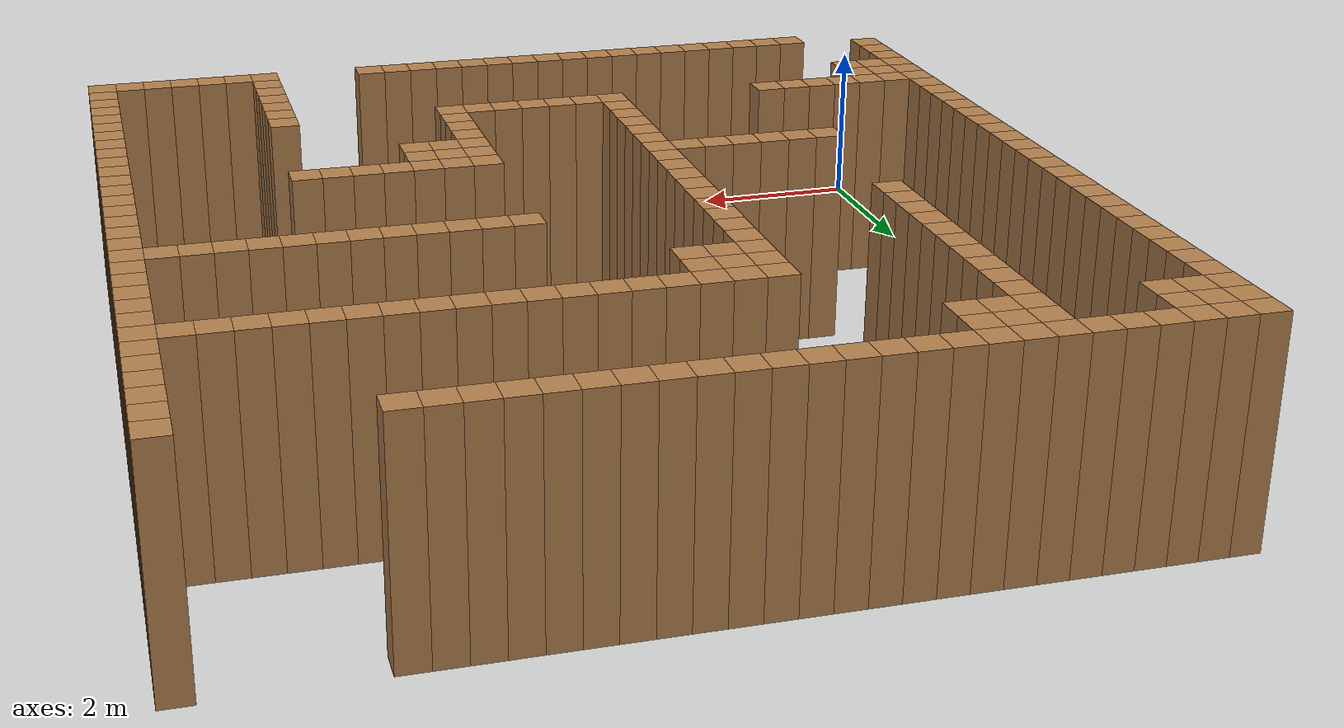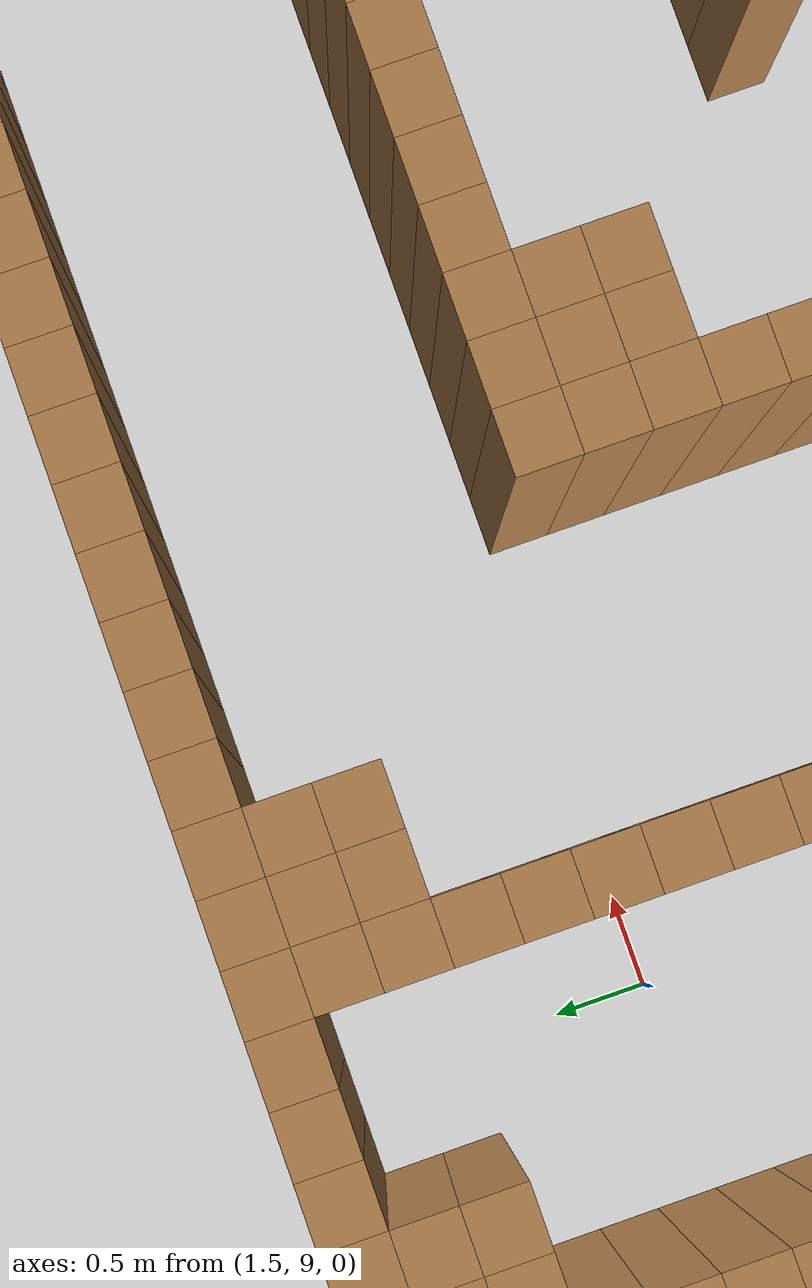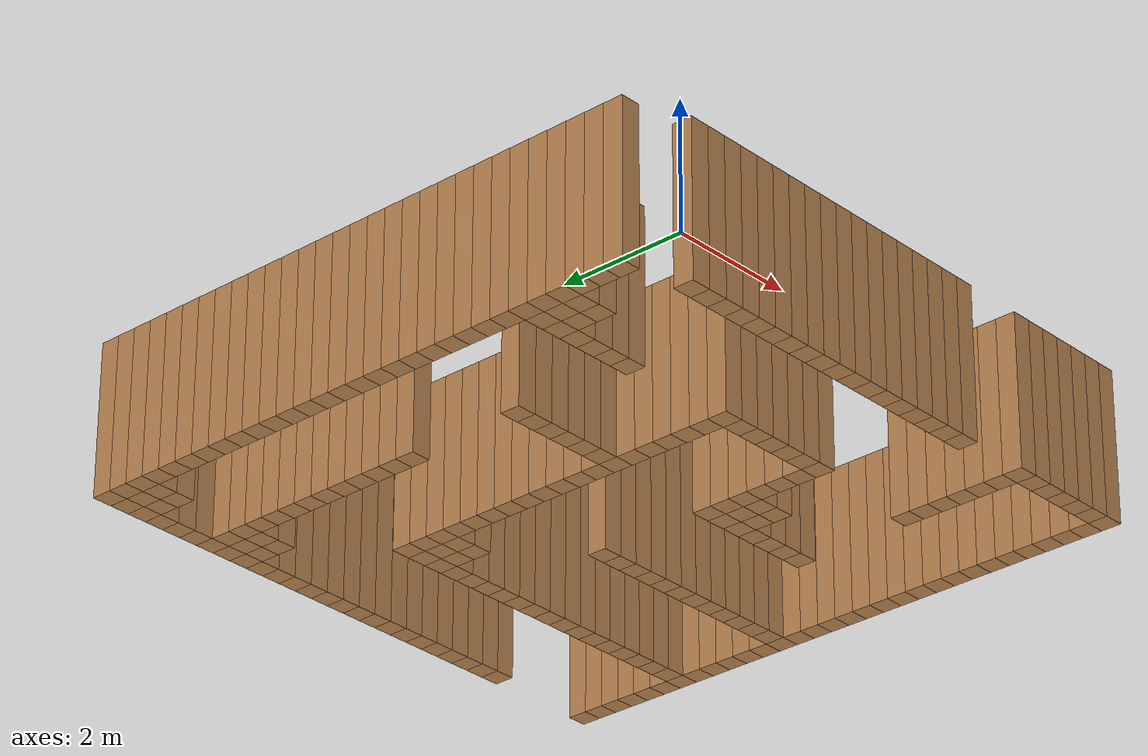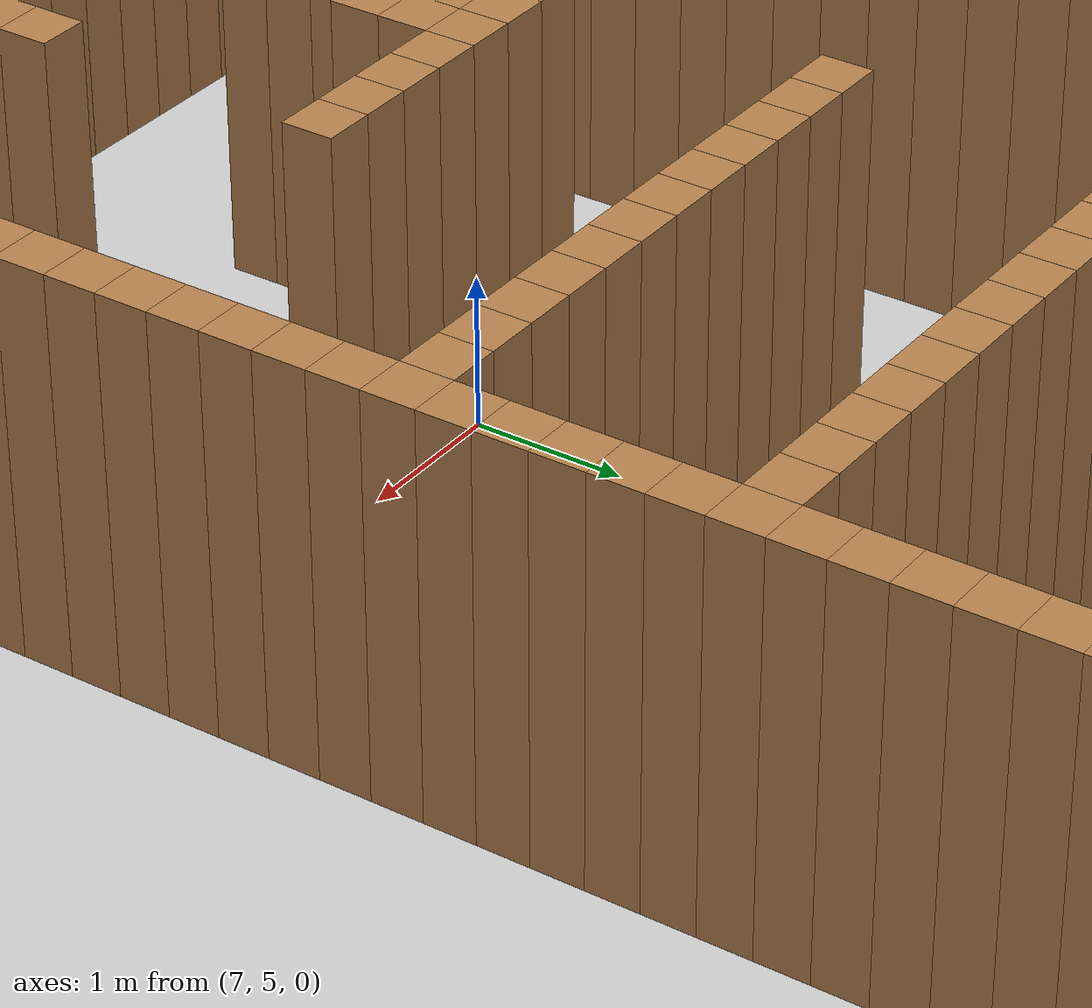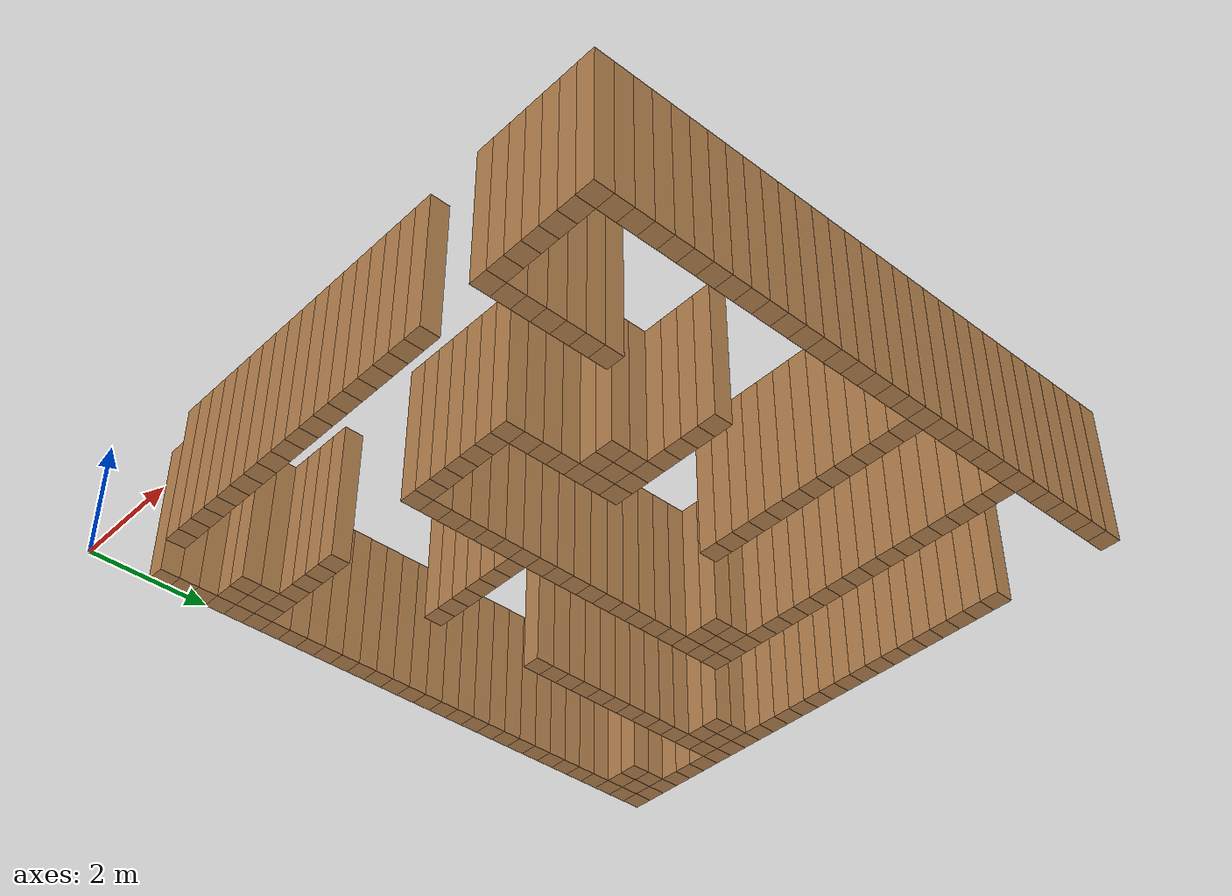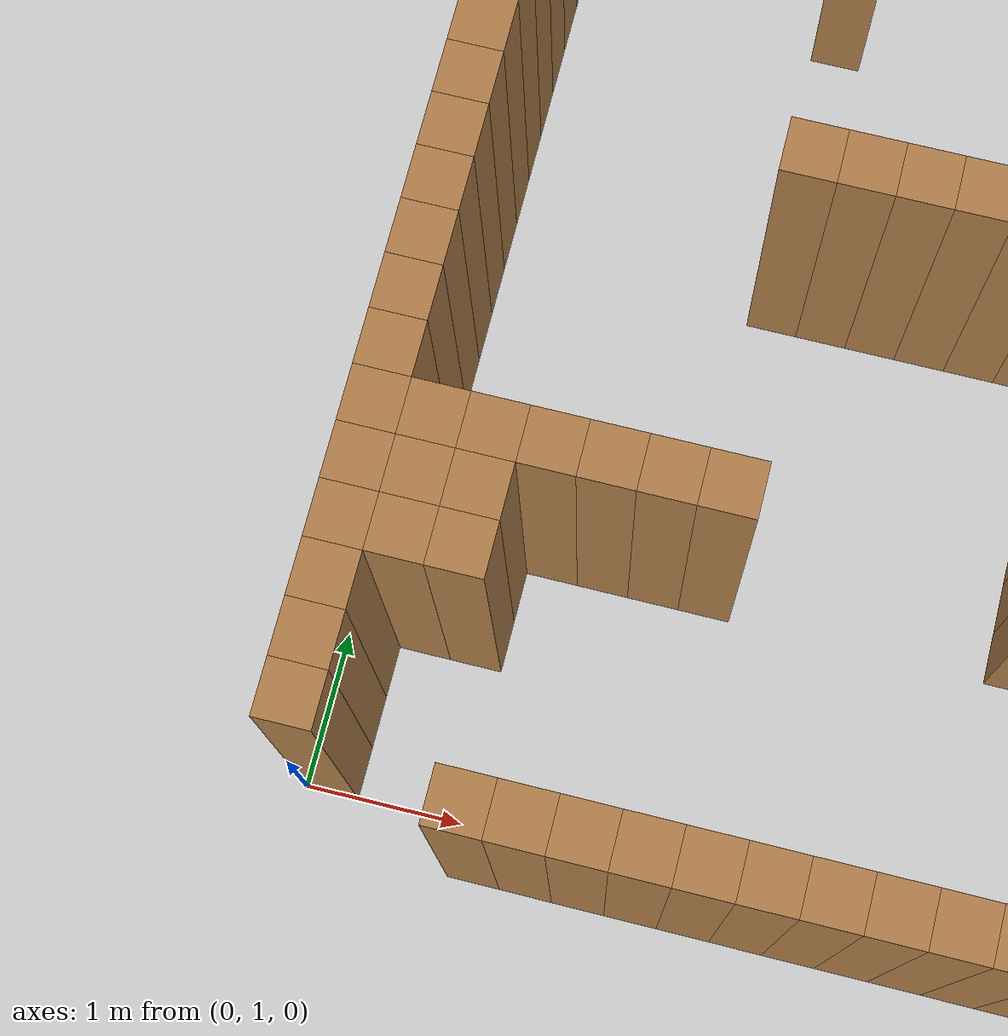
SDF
<?xml version='1.0'?>
    <sdf version='1.7'>
    <model name='maze'>
        <static>true</static>

                <link name='Wall_0'>
                <collision name='Wall_0_Collision'>
                    <geometry>
                    <box>
                        <size>0.3333333333333333 0.3333333333333333 2.5</size>
                    </box>
                    </geometry>
                    <pose>0 0 1.25 0 0 0</pose>
                </collision>
                <visual name='Wall_0_Visual'>
                    <pose>0 0 1.25 0 0 0</pose>
                    <geometry>
                    <box>
                        <size>0.3333333333333333 0.3333333333333333 2.5</size>
                    </box>
                    </geometry>
                    <material>
                    <script>
                        <uri>file://media/materials/scripts/gazebo.material</uri>
                        <name>Gazebo/Wood</name>
                    </script>
                    <ambient>1 1 1 1</ambient>
                    </material>
                    <meta>
                    <layer>0</layer>
                    </meta>
                </visual>
                <pose>0.16666666666666666 10.833333333333332 0 0 0 0</pose>
                </link>

                <link name='Wall_1'>
                <collision name='Wall_1_Collision'>
                    <geometry>
                    <box>
                        <size>0.3333333333333333 0.3333333333333333 2.5</size>
                    </box>
                    </geometry>
                    <pose>0 0 1.25 0 0 0</pose>
                </collision>
                <visual name='Wall_1_Visual'>
                    <pose>0 0 1.25 0 0 0</pose>
                    <geometry>
                    <box>
                        <size>0.3333333333333333 0.3333333333333333 2.5</size>
                    </box>
                    </geometry>
                    <material>
                    <script>
                        <uri>file://media/materials/scripts/gazebo.material</uri>
                        <name>Gazebo/Wood</name>
                    </script>
                    <ambient>1 1 1 1</ambient>
                    </material>
                    <meta>
                    <layer>0</layer>
                    </meta>
                </visual>
                <pose>0.5 10.833333333333332 0 0 0 0</pose>
                </link>

                <link name='Wall_2'>
                <collision name='Wall_2_Collision'>
                    <geometry>
                    <box>
                        <size>0.3333333333333333 0.3333333333333333 2.5</size>
                    </box>
                    </geometry>
                    <pose>0 0 1.25 0 0 0</pose>
                </collision>
                <visual name='Wall_2_Visual'>
                    <pose>0 0 1.25 0 0 0</pose>
                    <geometry>
                    <box>
                        <size>0.3333333333333333 0.3333333333333333 2.5</size>
                    </box>
                    </geometry>
                    <material>
                    <script>
                        <uri>file://media/materials/scripts/gazebo.material</uri>
                        <name>Gazebo/Wood</name>
                    </script>
                    <ambient>1 1 1 1</ambient>
                    </material>
                    <meta>
                    <layer>0</layer>
                    </meta>
                </visual>
                <pose>0.8333333333333333 10.833333333333332 0 0 0 0</pose>
                </link>

                <link name='Wall_3'>
                <collision name='Wall_3_Collision'>
                    <geometry>
                    <box>
                        <size>0.3333333333333333 0.3333333333333333 2.5</size>
                    </box>
                    </geometry>
                    <pose>0 0 1.25 0 0 0</pose>
                </collision>
                <visual name='Wall_3_Visual'>
                    <pose>0 0 1.25 0 0 0</pose>
                    <geometry>
                    <box>
                        <size>0.3333333333333333 0.3333333333333333 2.5</size>
                    </box>
                    </geometry>
                    <material>
                    <script>
                        <uri>file://media/materials/scripts/gazebo.material</uri>
                        <name>Gazebo/Wood</name>
                    </script>
                    <ambient>1 1 1 1</ambient>
                    </material>
                    <meta>
                    <layer>0</layer>
                    </meta>
                </visual>
                <pose>1.1666666666666667 10.833333333333332 0 0 0 0</pose>
                </link>

                <link name='Wall_4'>
                <collision name='Wall_4_Collision'>
                    <geometry>
                    <box>
                        <size>0.3333333333333333 0.3333333333333333 2.5</size>
                    </box>
                    </geometry>
                    <pose>0 0 1.25 0 0 0</pose>
                </collision>
                <visual name='Wall_4_Visual'>
                    <pose>0 0 1.25 0 0 0</pose>
                    <geometry>
                    <box>
                        <size>0.3333333333333333 0.3333333333333333 2.5</size>
                    </box>
                    </geometry>
                    <material>
                    <script>
                        <uri>file://media/materials/scripts/gazebo.material</uri>
                        <name>Gazebo/Wood</name>
                    </script>
                    <ambient>1 1 1 1</ambient>
                    </material>
                    <meta>
                    <layer>0</layer>
                    </meta>
                </visual>
                <pose>1.5 10.833333333333332 0 0 0 0</pose>
                </link>

                <link name='Wall_5'>
                <collision name='Wall_5_Collision'>
                    <geometry>
                    <box>
                        <size>0.3333333333333333 0.3333333333333333 2.5</size>
                    </box>
                    </geometry>
                    <pose>0 0 1.25 0 0 0</pose>
                </collision>
                <visual name='Wall_5_Visual'>
                    <pose>0 0 1.25 0 0 0</pose>
                    <geometry>
                    <box>
                        <size>0.3333333333333333 0.3333333333333333 2.5</size>
                    </box>
                    </geometry>
                    <material>
                    <script>
                        <uri>file://media/materials/scripts/gazebo.material</uri>
                        <name>Gazebo/Wood</name>
                    </script>
                    <ambient>1 1 1 1</ambient>
                    </material>
                    <meta>
                    <layer>0</layer>
                    </meta>
                </visual>
                <pose>1.8333333333333333 10.833333333333332 0 0 0 0</pose>
                </link>

                <link name='Wall_6'>
                <collision name='Wall_6_Collision'>
                    <geometry>
                    <box>
                        <size>0.3333333333333333 0.3333333333333333 2.5</size>
                    </box>
                    </geometry>
                    <pose>0 0 1.25 0 0 0</pose>
                </collision>
                <visual name='Wall_6_Visual'>
                    <pose>0 0 1.25 0 0 0</pose>
                    <geometry>
                    <box>
                        <size>0.3333333333333333 0.3333333333333333 2.5</size>
                    </box>
                    </geometry>
                    <material>
                    <script>
                        <uri>file://media/materials/scripts/gazebo.material</uri>
                        <name>Gazebo/Wood</name>
                    </script>
                    <ambient>1 1 1 1</ambient>
                    </material>
                    <meta>
                    <layer>0</layer>
                    </meta>
                </visual>
                <pose>2.1666666666666665 10.833333333333332 0 0 0 0</pose>
                </link>

                <link name='Wall_7'>
                <collision name='Wall_7_Collision'>
                    <geometry>
                    <box>
                        <size>0.3333333333333333 0.3333333333333333 2.5</size>
                    </box>
                    </geometry>
                    <pose>0 0 1.25 0 0 0</pose>
                </collision>
                <visual name='Wall_7_Visual'>
                    <pose>0 0 1.25 0 0 0</pose>
                    <geometry>
                    <box>
                        <size>0.3333333333333333 0.3333333333333333 2.5</size>
                    </box>
                    </geometry>
                    <material>
                    <script>
                        <uri>file://media/materials/scripts/gazebo.material</uri>
                        <name>Gazebo/Wood</name>
                    </script>
                    <ambient>1 1 1 1</ambient>
                    </material>
                    <meta>
                    <layer>0</layer>
                    </meta>
                </visual>
                <pose>2.4999999999999996 10.833333333333332 0 0 0 0</pose>
                </link>

                <link name='Wall_8'>
                <collision name='Wall_8_Collision'>
                    <geometry>
                    <box>
                        <size>0.3333333333333333 0.3333333333333333 2.5</size>
                    </box>
                    </geometry>
                    <pose>0 0 1.25 0 0 0</pose>
                </collision>
                <visual name='Wall_8_Visual'>
                    <pose>0 0 1.25 0 0 0</pose>
                    <geometry>
                    <box>
                        <size>0.3333333333333333 0.3333333333333333 2.5</size>
                    </box>
                    </geometry>
                    <material>
                    <script>
                        <uri>file://media/materials/scripts/gazebo.material</uri>
                        <name>Gazebo/Wood</name>
                    </script>
                    <ambient>1 1 1 1</ambient>
                    </material>
                    <meta>
                    <layer>0</layer>
                    </meta>
                </visual>
                <pose>2.833333333333333 10.833333333333332 0 0 0 0</pose>
                </link>

                <link name='Wall_9'>
                <collision name='Wall_9_Collision'>
                    <geometry>
                    <box>
                        <size>0.3333333333333333 0.3333333333333333 2.5</size>
                    </box>
                    </geometry>
                    <pose>0 0 1.25 0 0 0</pose>
                </collision>
                <visual name='Wall_9_Visual'>
                    <pose>0 0 1.25 0 0 0</pose>
                    <geometry>
                    <box>
                        <size>0.3333333333333333 0.3333333333333333 2.5</size>
                    </box>
                    </geometry>
                    <material>
                    <script>
                        <uri>file://media/materials/scripts/gazebo.material</uri>
                        <name>Gazebo/Wood</name>
                    </script>
                    <ambient>1 1 1 1</ambient>
                    </material>
                    <meta>
                    <layer>0</layer>
                    </meta>
                </visual>
                <pose>3.1666666666666665 10.833333333333332 0 0 0 0</pose>
                </link>

                <link name='Wall_10'>
                <collision name='Wall_10_Collision'>
                    <geometry>
                    <box>
                        <size>0.3333333333333333 0.3333333333333333 2.5</size>
                    </box>
                    </geometry>
                    <pose>0 0 1.25 0 0 0</pose>
                </collision>
                <visual name='Wall_10_Visual'>
                    <pose>0 0 1.25 0 0 0</pose>
                    <geometry>
                    <box>
                        <size>0.3333333333333333 0.3333333333333333 2.5</size>
                    </box>
                    </geometry>
                    <material>
                    <script>
                        <uri>file://media/materials/scripts/gazebo.material</uri>
                        <name>Gazebo/Wood</name>
                    </script>
                    <ambient>1 1 1 1</ambient>
                    </material>
                    <meta>
                    <layer>0</layer>
                    </meta>
                </visual>
                <pose>3.4999999999999996 10.833333333333332 0 0 0 0</pose>
                </link>

                <link name='Wall_11'>
                <collision name='Wall_11_Collision'>
                    <geometry>
                    <box>
                        <size>0.3333333333333333 0.3333333333333333 2.5</size>
                    </box>
                    </geometry>
                    <pose>0 0 1.25 0 0 0</pose>
                </collision>
                <visual name='Wall_11_Visual'>
                    <pose>0 0 1.25 0 0 0</pose>
                    <geometry>
                    <box>
                        <size>0.3333333333333333 0.3333333333333333 2.5</size>
                    </box>
                    </geometry>
                    <material>
                    <script>
                        <uri>file://media/materials/scripts/gazebo.material</uri>
                        <name>Gazebo/Wood</name>
                    </script>
                    <ambient>1 1 1 1</ambient>
                    </material>
                    <meta>
                    <layer>0</layer>
                    </meta>
                </visual>
                <pose>3.833333333333333 10.833333333333332 0 0 0 0</pose>
                </link>

                <link name='Wall_12'>
                <collision name='Wall_12_Collision'>
                    <geometry>
                    <box>
                        <size>0.3333333333333333 0.3333333333333333 2.5</size>
                    </box>
                    </geometry>
                    <pose>0 0 1.25 0 0 0</pose>
                </collision>
                <visual name='Wall_12_Visual'>
                    <pose>0 0 1.25 0 0 0</pose>
                    <geometry>
                    <box>
                        <size>0.3333333333333333 0.3333333333333333 2.5</size>
                    </box>
                    </geometry>
                    <material>
                    <script>
                        <uri>file://media/materials/scripts/gazebo.material</uri>
                        <name>Gazebo/Wood</name>
                    </script>
                    <ambient>1 1 1 1</ambient>
                    </material>
                    <meta>
                    <layer>0</layer>
                    </meta>
                </visual>
                <pose>4.166666666666667 10.833333333333332 0 0 0 0</pose>
                </link>

                <link name='Wall_13'>
                <collision name='Wall_13_Collision'>
                    <geometry>
                    <box>
                        <size>0.3333333333333333 0.3333333333333333 2.5</size>
                    </box>
                    </geometry>
                    <pose>0 0 1.25 0 0 0</pose>
                </collision>
                <visual name='Wall_13_Visual'>
                    <pose>0 0 1.25 0 0 0</pose>
                    <geometry>
                    <box>
                        <size>0.3333333333333333 0.3333333333333333 2.5</size>
                    </box>
                    </geometry>
                    <material>
                    <script>
                        <uri>file://media/materials/scripts/gazebo.material</uri>
                        <name>Gazebo/Wood</name>
                    </script>
                    <ambient>1 1 1 1</ambient>
                    </material>
                    <meta>
                    <layer>0</layer>
                    </meta>
                </visual>
                <pose>4.5 10.833333333333332 0 0 0 0</pose>
                </link>

                <link name='Wall_14'>
                <collision name='Wall_14_Collision'>
                    <geometry>
                    <box>
                        <size>0.3333333333333333 0.3333333333333333 2.5</size>
                    </box>
                    </geometry>
                    <pose>0 0 1.25 0 0 0</pose>
                </collision>
                <visual name='Wall_14_Visual'>
                    <pose>0 0 1.25 0 0 0</pose>
                    <geometry>
                    <box>
                        <size>0.3333333333333333 0.3333333333333333 2.5</size>
                    </box>
                    </geometry>
                    <material>
                    <script>
                        <uri>file://media/materials/scripts/gazebo.material</uri>
                        <name>Gazebo/Wood</name>
                    </script>
                    <ambient>1 1 1 1</ambient>
                    </material>
                    <meta>
                    <layer>0</layer>
                    </meta>
                </visual>
                <pose>4.833333333333333 10.833333333333332 0 0 0 0</pose>
                </link>

                <link name='Wall_15'>
                <collision name='Wall_15_Collision'>
                    <geometry>
                    <box>
                        <size>0.3333333333333333 0.3333333333333333 2.5</size>
                    </box>
                    </geometry>
                    <pose>0 0 1.25 0 0 0</pose>
                </collision>
                <visual name='Wall_15_Visual'>
                    <pose>0 0 1.25 0 0 0</pose>
                    <geometry>
                    <box>
                        <size>0.3333333333333333 0.3333333333333333 2.5</size>
                    </box>
                    </geometry>
                    <material>
                    <script>
                        <uri>file://media/materials/scripts/gazebo.material</uri>
                        <name>Gazebo/Wood</name>
                    </script>
                    <ambient>1 1 1 1</ambient>
                    </material>
                    <meta>
                    <layer>0</layer>
                    </meta>
                </visual>
                <pose>5.166666666666667 10.833333333333332 0 0 0 0</pose>
                </link>

                <link name='Wall_16'>
                <collision name='Wall_16_Collision'>
                    <geometry>
                    <box>
                        <size>0.3333333333333333 0.3333333333333333 2.5</size>
                    </box>
                    </geometry>
                    <pose>0 0 1.25 0 0 0</pose>
                </collision>
                <visual name='Wall_16_Visual'>
                    <pose>0 0 1.25 0 0 0</pose>
                    <geometry>
                    <box>
                        <size>0.3333333333333333 0.3333333333333333 2.5</size>
                    </box>
                    </geometry>
                    <material>
                    <script>
                        <uri>file://media/materials/scripts/gazebo.material</uri>
                        <name>Gazebo/Wood</name>
                    </script>
                    <ambient>1 1 1 1</ambient>
                    </material>
                    <meta>
                    <layer>0</layer>
                    </meta>
                </visual>
                <pose>5.5 10.833333333333332 0 0 0 0</pose>
                </link>

                <link name='Wall_17'>
                <collision name='Wall_17_Collision'>
                    <geometry>
                    <box>
                        <size>0.3333333333333333 0.3333333333333333 2.5</size>
                    </box>
                    </geometry>
                    <pose>0 0 1.25 0 0 0</pose>
                </collision>
                <visual name='Wall_17_Visual'>
                    <pose>0 0 1.25 0 0 0</pose>
                    <geometry>
                    <box>
                        <size>0.3333333333333333 0.3333333333333333 2.5</size>
                    </box>
                    </geometry>
                    <material>
                    <script>
                        <uri>file://media/materials/scripts/gazebo.material</uri>
                        <name>Gazebo/Wood</name>
                    </script>
                    <ambient>1 1 1 1</ambient>
                    </material>
                    <meta>
                    <layer>0</layer>
                    </meta>
                </visual>
                <pose>5.833333333333333 10.833333333333332 0 0 0 0</pose>
                </link>

                <link name='Wall_18'>
                <collision name='Wall_18_Collision'>
                    <geometry>
                    <box>
                        <size>0.3333333333333333 0.3333333333333333 2.5</size>
                    </box>
                    </geometry>
                    <pose>0 0 1.25 0 0 0</pose>
                </collision>
                <visual name='Wall_18_Visual'>
                    <pose>0 0 1.25 0 0 0</pose>
                    <geometry>
                    <box>
                        <size>0.3333333333333333 0.3333333333333333 2.5</size>
                    </box>
                    </geometry>
                    <material>
                    <script>
                        <uri>file://media/materials/scripts/gazebo.material</uri>
                        <name>Gazebo/Wood</name>
                    </script>
                    <ambient>1 1 1 1</ambient>
                    </material>
                    <meta>
                    <layer>0</layer>
                    </meta>
                </visual>
                <pose>6.166666666666667 10.833333333333332 0 0 0 0</pose>
                </link>

                <link name='Wall_19'>
                <collision name='Wall_19_Collision'>
                    <geometry>
                    <box>
                        <size>0.3333333333333333 0.3333333333333333 2.5</size>
                    </box>
                    </geometry>
                    <pose>0 0 1.25 0 0 0</pose>
                </collision>
                <visual name='Wall_19_Visual'>
                    <pose>0 0 1.25 0 0 0</pose>
                    <geometry>
                    <box>
                        <size>0.3333333333333333 0.3333333333333333 2.5</size>
                    </box>
                    </geometry>
                    <material>
                    <script>
                        <uri>file://media/materials/scripts/gazebo.material</uri>
                        <name>Gazebo/Wood</name>
                    </script>
                    <ambient>1 1 1 1</ambient>
                    </material>
                    <meta>
                    <layer>0</layer>
                    </meta>
                </visual>
                <pose>6.5 10.833333333333332 0 0 0 0</pose>
                </link>

                <link name='Wall_20'>
                <collision name='Wall_20_Collision'>
                    <geometry>
                    <box>
                        <size>0.3333333333333333 0.3333333333333333 2.5</size>
                    </box>
                    </geometry>
                    <pose>0 0 1.25 0 0 0</pose>
                </collision>
                <visual name='Wall_20_Visual'>
                    <pose>0 0 1.25 0 0 0</pose>
                    <geometry>
                    <box>
                        <size>0.3333333333333333 0.3333333333333333 2.5</size>
                    </box>
                    </geometry>
                    <material>
                    <script>
                        <uri>file://media/materials/scripts/gazebo.material</uri>
                        <name>Gazebo/Wood</name>
                    </script>
                    <ambient>1 1 1 1</ambient>
                    </material>
                    <meta>
                    <layer>0</layer>
                    </meta>
                </visual>
                <pose>6.833333333333333 10.833333333333332 0 0 0 0</pose>
                </link>

                <link name='Wall_21'>
                <collision name='Wall_21_Collision'>
                    <geometry>
                    <box>
                        <size>0.3333333333333333 0.3333333333333333 2.5</size>
                    </box>
                    </geometry>
                    <pose>0 0 1.25 0 0 0</pose>
                </collision>
                <visual name='Wall_21_Visual'>
                    <pose>0 0 1.25 0 0 0</pose>
                    <geometry>
                    <box>
                        <size>0.3333333333333333 0.3333333333333333 2.5</size>
                    </box>
                    </geometry>
                    <material>
                    <script>
                        <uri>file://media/materials/scripts/gazebo.material</uri>
                        <name>Gazebo/Wood</name>
                    </script>
                    <ambient>1 1 1 1</ambient>
                    </material>
                    <meta>
                    <layer>0</layer>
                    </meta>
                </visual>
                <pose>7.166666666666667 10.833333333333332 0 0 0 0</pose>
                </link>

                <link name='Wall_22'>
                <collision name='Wall_22_Collision'>
                    <geometry>
                    <box>
                        <size>0.3333333333333333 0.3333333333333333 2.5</size>
                    </box>
                    </geometry>
                    <pose>0 0 1.25 0 0 0</pose>
                </collision>
                <visual name='Wall_22_Visual'>
                    <pose>0 0 1.25 0 0 0</pose>
                    <geometry>
                    <box>
                        <size>0.3333333333333333 0.3333333333333333 2.5</size>
                    </box>
                    </geometry>
                    <material>
                    <script>
                        <uri>file://media/materials/scripts/gazebo.material</uri>
                        <name>Gazebo/Wood</name>
                    </script>
                    <ambient>1 1 1 1</ambient>
                    </material>
                    <meta>
                    <layer>0</layer>
                    </meta>
                </visual>
                <pose>7.5 10.833333333333332 0 0 0 0</pose>
                </link>

                <link name='Wall_23'>
                <collision name='Wall_23_Collision'>
                    <geometry>
                    <box>
                        <size>0.3333333333333333 0.3333333333333333 2.5</size>
                    </box>
                    </geometry>
                    <pose>0 0 1.25 0 0 0</pose>
                </collision>
                <visual name='Wall_23_Visual'>
                    <pose>0 0 1.25 0 0 0</pose>
                    <geometry>
                    <box>
                        <size>0.3333333333333333 0.3333333333333333 2.5</size>
                    </box>
                    </geometry>
                    <material>
                    <script>
                        <uri>file://media/materials/scripts/gazebo.material</uri>
                        <name>Gazebo/Wood</name>
                    </script>
                    <ambient>1 1 1 1</ambient>
                    </material>
                    <meta>
                    <layer>0</layer>
                    </meta>
                </visual>
                <pose>7.833333333333333 10.833333333333332 0 0 0 0</pose>
                </link>

                <link name='Wall_24'>
                <collision name='Wall_24_Collision'>
                    <geometry>
                    <box>
                        <size>0.3333333333333333 0.3333333333333333 2.5</size>
                    </box>
                    </geometry>
                    <pose>0 0 1.25 0 0 0</pose>
                </collision>
                <visual name='Wall_24_Visual'>
                    <pose>0 0 1.25 0 0 0</pose>
                    <geometry>
                    <box>
                        <size>0.3333333333333333 0.3333333333333333 2.5</size>
                    </box>
                    </geometry>
                    <material>
                    <script>
                        <uri>file://media/materials/scripts/gazebo.material</uri>
                        <name>Gazebo/Wood</name>
                    </script>
                    <ambient>1 1 1 1</ambient>
                    </material>
                    <meta>
                    <layer>0</layer>
                    </meta>
                </visual>
                <pose>8.166666666666666 10.833333333333332 0 0 0 0</pose>
                </link>

                <link name='Wall_25'>
                <collision name='Wall_25_Collision'>
                    <geometry>
                    <box>
                        <size>0.3333333333333333 0.3333333333333333 2.5</size>
                    </box>
                    </geometry>
                    <pose>0 0 1.25 0 0 0</pose>
                </collision>
                <visual name='Wall_25_Visual'>
                    <pose>0 0 1.25 0 0 0</pose>
                    <geometry>
                    <box>
                        <size>0.3333333333333333 0.3333333333333333 2.5</size>
                    </box>
                    </geometry>
                    <material>
                    <script>
                        <uri>file://media/materials/scripts/gazebo.material</uri>
                        <name>Gazebo/Wood</name>
                    </script>
                    <ambient>1 1 1 1</ambient>
                    </material>
                    <meta>
                    <layer>0</layer>
                    </meta>
                </visual>
                <pose>10.166666666666666 10.833333333333332 0 0 0 0</pose>
                </link>

                <link name='Wall_26'>
                <collision name='Wall_26_Collision'>
                    <geometry>
                    <box>
                        <size>0.3333333333333333 0.3333333333333333 2.5</size>
                    </box>
                    </geometry>
                    <pose>0 0 1.25 0 0 0</pose>
                </collision>
                <visual name='Wall_26_Visual'>
                    <pose>0 0 1.25 0 0 0</pose>
                    <geometry>
                    <box>
                        <size>0.3333333333333333 0.3333333333333333 2.5</size>
                    </box>
                    </geometry>
                    <material>
                    <script>
                        <uri>file://media/materials/scripts/gazebo.material</uri>
                        <name>Gazebo/Wood</name>
                    </script>
                    <ambient>1 1 1 1</ambient>
                    </material>
                    <meta>
                    <layer>0</layer>
                    </meta>
                </visual>
                <pose>0.16666666666666666 10.499999999999998 0 0 0 0</pose>
                </link>

                <link name='Wall_27'>
                <collision name='Wall_27_Collision'>
                    <geometry>
                    <box>
                        <size>0.3333333333333333 0.3333333333333333 2.5</size>
                    </box>
                    </geometry>
                    <pose>0 0 1.25 0 0 0</pose>
                </collision>
                <visual name='Wall_27_Visual'>
                    <pose>0 0 1.25 0 0 0</pose>
                    <geometry>
                    <box>
                        <size>0.3333333333333333 0.3333333333333333 2.5</size>
                    </box>
                    </geometry>
                    <material>
                    <script>
                        <uri>file://media/materials/scripts/gazebo.material</uri>
                        <name>Gazebo/Wood</name>
                    </script>
                    <ambient>1 1 1 1</ambient>
                    </material>
                    <meta>
                    <layer>0</layer>
                    </meta>
                </visual>
                <pose>0.5 10.499999999999998 0 0 0 0</pose>
                </link>

                <link name='Wall_28'>
                <collision name='Wall_28_Collision'>
                    <geometry>
                    <box>
                        <size>0.3333333333333333 0.3333333333333333 2.5</size>
                    </box>
                    </geometry>
                    <pose>0 0 1.25 0 0 0</pose>
                </collision>
                <visual name='Wall_28_Visual'>
                    <pose>0 0 1.25 0 0 0</pose>
                    <geometry>
                    <box>
                        <size>0.3333333333333333 0.3333333333333333 2.5</size>
                    </box>
                    </geometry>
                    <material>
                    <script>
                        <uri>file://media/materials/scripts/gazebo.material</uri>
                        <name>Gazebo/Wood</name>
                    </script>
                    <ambient>1 1 1 1</ambient>
                    </material>
                    <meta>
                    <layer>0</layer>
                    </meta>
                </visual>
                <pose>0.8333333333333333 10.499999999999998 0 0 0 0</pose>
                </link>

                <link name='Wall_29'>
                <collision name='Wall_29_Collision'>
                    <geometry>
                    <box>
                        <size>0.3333333333333333 0.3333333333333333 2.5</size>
                    </box>
                    </geometry>
                    <pose>0 0 1.25 0 0 0</pose>
                </collision>
                <visual name='Wall_29_Visual'>
                    <pose>0 0 1.25 0 0 0</pose>
                    <geometry>
                    <box>
                        <size>0.3333333333333333 0.3333333333333333 2.5</size>
                    </box>
                    </geometry>
                    <material>
                    <script>
                        <uri>file://media/materials/scripts/gazebo.material</uri>
                        <name>Gazebo/Wood</name>
                    </script>
                    <ambient>1 1 1 1</ambient>
                    </material>
                    <meta>
                    <layer>0</layer>
                    </meta>
                </visual>
                <pose>2.1666666666666665 10.499999999999998 0 0 0 0</pose>
                </link>

                <link name='Wall_30'>
                <collision name='Wall_30_Collision'>
                    <geometry>
                    <box>
                        <size>0.3333333333333333 0.3333333333333333 2.5</size>
                    </box>
                    </geometry>
                    <pose>0 0 1.25 0 0 0</pose>
                </collision>
                <visual name='Wall_30_Visual'>
                    <pose>0 0 1.25 0 0 0</pose>
                    <geometry>
                    <box>
                        <size>0.3333333333333333 0.3333333333333333 2.5</size>
                    </box>
                    </geometry>
                    <material>
                    <script>
                        <uri>file://media/materials/scripts/gazebo.material</uri>
                        <name>Gazebo/Wood</name>
                    </script>
                    <ambient>1 1 1 1</ambient>
                    </material>
                    <meta>
                    <layer>0</layer>
                    </meta>
                </visual>
                <pose>2.4999999999999996 10.499999999999998 0 0 0 0</pose>
                </link>

                <link name='Wall_31'>
                <collision name='Wall_31_Collision'>
                    <geometry>
                    <box>
                        <size>0.3333333333333333 0.3333333333333333 2.5</size>
                    </box>
                    </geometry>
                    <pose>0 0 1.25 0 0 0</pose>
                </collision>
                <visual name='Wall_31_Visual'>
                    <pose>0 0 1.25 0 0 0</pose>
                    <geometry>
                    <box>
                        <size>0.3333333333333333 0.3333333333333333 2.5</size>
                    </box>
                    </geometry>
                    <material>
                    <script>
                        <uri>file://media/materials/scripts/gazebo.material</uri>
                        <name>Gazebo/Wood</name>
                    </script>
                    <ambient>1 1 1 1</ambient>
                    </material>
                    <meta>
                    <layer>0</layer>
                    </meta>
                </visual>
                <pose>2.833333333333333 10.499999999999998 0 0 0 0</pose>
                </link>

                <link name='Wall_32'>
                <collision name='Wall_32_Collision'>
                    <geometry>
                    <box>
                        <size>0.3333333333333333 0.3333333333333333 2.5</size>
                    </box>
                    </geometry>
                    <pose>0 0 1.25 0 0 0</pose>
                </collision>
                <visual name='Wall_32_Visual'>
                    <pose>0 0 1.25 0 0 0</pose>
                    <geometry>
                    <box>
                        <size>0.3333333333333333 0.3333333333333333 2.5</size>
                    </box>
                    </geometry>
                    <material>
                    <script>
                        <uri>file://media/materials/scripts/gazebo.material</uri>
                        <name>Gazebo/Wood</name>
                    </script>
                    <ambient>1 1 1 1</ambient>
                    </material>
                    <meta>
                    <layer>0</layer>
                    </meta>
                </visual>
                <pose>10.166666666666666 10.499999999999998 0 0 0 0</pose>
                </link>

                <link name='Wall_33'>
                <collision name='Wall_33_Collision'>
                    <geometry>
                    <box>
                        <size>0.3333333333333333 0.3333333333333333 2.5</size>
                    </box>
                    </geometry>
                    <pose>0 0 1.25 0 0 0</pose>
                </collision>
                <visual name='Wall_33_Visual'>
                    <pose>0 0 1.25 0 0 0</pose>
                    <geometry>
                    <box>
                        <size>0.3333333333333333 0.3333333333333333 2.5</size>
                    </box>
                    </geometry>
                    <material>
                    <script>
                        <uri>file://media/materials/scripts/gazebo.material</uri>
                        <name>Gazebo/Wood</name>
                    </script>
                    <ambient>1 1 1 1</ambient>
                    </material>
                    <meta>
                    <layer>0</layer>
                    </meta>
                </visual>
                <pose>0.16666666666666666 10.166666666666666 0 0 0 0</pose>
                </link>

                <link name='Wall_34'>
                <collision name='Wall_34_Collision'>
                    <geometry>
                    <box>
                        <size>0.3333333333333333 0.3333333333333333 2.5</size>
                    </box>
                    </geometry>
                    <pose>0 0 1.25 0 0 0</pose>
                </collision>
                <visual name='Wall_34_Visual'>
                    <pose>0 0 1.25 0 0 0</pose>
                    <geometry>
                    <box>
                        <size>0.3333333333333333 0.3333333333333333 2.5</size>
                    </box>
                    </geometry>
                    <material>
                    <script>
                        <uri>file://media/materials/scripts/gazebo.material</uri>
                        <name>Gazebo/Wood</name>
                    </script>
                    <ambient>1 1 1 1</ambient>
                    </material>
                    <meta>
                    <layer>0</layer>
                    </meta>
                </visual>
                <pose>0.5 10.166666666666666 0 0 0 0</pose>
                </link>

                <link name='Wall_35'>
                <collision name='Wall_35_Collision'>
                    <geometry>
                    <box>
                        <size>0.3333333333333333 0.3333333333333333 2.5</size>
                    </box>
                    </geometry>
                    <pose>0 0 1.25 0 0 0</pose>
                </collision>
                <visual name='Wall_35_Visual'>
                    <pose>0 0 1.25 0 0 0</pose>
                    <geometry>
                    <box>
                        <size>0.3333333333333333 0.3333333333333333 2.5</size>
                    </box>
                    </geometry>
                    <material>
                    <script>
                        <uri>file://media/materials/scripts/gazebo.material</uri>
                        <name>Gazebo/Wood</name>
                    </script>
                    <ambient>1 1 1 1</ambient>
                    </material>
                    <meta>
                    <layer>0</layer>
                    </meta>
                </visual>
                <pose>0.8333333333333333 10.166666666666666 0 0 0 0</pose>
                </link>

                <link name='Wall_36'>
                <collision name='Wall_36_Collision'>
                    <geometry>
                    <box>
                        <size>0.3333333333333333 0.3333333333333333 2.5</size>
                    </box>
                    </geometry>
                    <pose>0 0 1.25 0 0 0</pose>
                </collision>
                <visual name='Wall_36_Visual'>
                    <pose>0 0 1.25 0 0 0</pose>
                    <geometry>
                    <box>
                        <size>0.3333333333333333 0.3333333333333333 2.5</size>
                    </box>
                    </geometry>
                    <material>
                    <script>
                        <uri>file://media/materials/scripts/gazebo.material</uri>
                        <name>Gazebo/Wood</name>
                    </script>
                    <ambient>1 1 1 1</ambient>
                    </material>
                    <meta>
                    <layer>0</layer>
                    </meta>
                </visual>
                <pose>2.1666666666666665 10.166666666666666 0 0 0 0</pose>
                </link>

                <link name='Wall_37'>
                <collision name='Wall_37_Collision'>
                    <geometry>
                    <box>
                        <size>0.3333333333333333 0.3333333333333333 2.5</size>
                    </box>
                    </geometry>
                    <pose>0 0 1.25 0 0 0</pose>
                </collision>
                <visual name='Wall_37_Visual'>
                    <pose>0 0 1.25 0 0 0</pose>
                    <geometry>
                    <box>
                        <size>0.3333333333333333 0.3333333333333333 2.5</size>
                    </box>
                    </geometry>
                    <material>
                    <script>
                        <uri>file://media/materials/scripts/gazebo.material</uri>
                        <name>Gazebo/Wood</name>
                    </script>
                    <ambient>1 1 1 1</ambient>
                    </material>
                    <meta>
                    <layer>0</layer>
                    </meta>
                </visual>
                <pose>2.4999999999999996 10.166666666666666 0 0 0 0</pose>
                </link>

                <link name='Wall_38'>
                <collision name='Wall_38_Collision'>
                    <geometry>
                    <box>
                        <size>0.3333333333333333 0.3333333333333333 2.5</size>
                    </box>
                    </geometry>
                    <pose>0 0 1.25 0 0 0</pose>
                </collision>
                <visual name='Wall_38_Visual'>
                    <pose>0 0 1.25 0 0 0</pose>
                    <geometry>
                    <box>
                        <size>0.3333333333333333 0.3333333333333333 2.5</size>
                    </box>
                    </geometry>
                    <material>
                    <script>
                        <uri>file://media/materials/scripts/gazebo.material</uri>
                        <name>Gazebo/Wood</name>
                    </script>
                    <ambient>1 1 1 1</ambient>
                    </material>
                    <meta>
                    <layer>0</layer>
                    </meta>
                </visual>
                <pose>2.833333333333333 10.166666666666666 0 0 0 0</pose>
                </link>

                <link name='Wall_39'>
                <collision name='Wall_39_Collision'>
                    <geometry>
                    <box>
                        <size>0.3333333333333333 0.3333333333333333 2.5</size>
                    </box>
                    </geometry>
                    <pose>0 0 1.25 0 0 0</pose>
                </collision>
                <visual name='Wall_39_Visual'>
                    <pose>0 0 1.25 0 0 0</pose>
                    <geometry>
                    <box>
                        <size>0.3333333333333333 0.3333333333333333 2.5</size>
                    </box>
                    </geometry>
                    <material>
                    <script>
                        <uri>file://media/materials/scripts/gazebo.material</uri>
                        <name>Gazebo/Wood</name>
                    </script>
                    <ambient>1 1 1 1</ambient>
                    </material>
                    <meta>
                    <layer>0</layer>
                    </meta>
                </visual>
                <pose>10.166666666666666 10.166666666666666 0 0 0 0</pose>
                </link>

                <link name='Wall_40'>
                <collision name='Wall_40_Collision'>
                    <geometry>
                    <box>
                        <size>0.3333333333333333 0.3333333333333333 2.5</size>
                    </box>
                    </geometry>
                    <pose>0 0 1.25 0 0 0</pose>
                </collision>
                <visual name='Wall_40_Visual'>
                    <pose>0 0 1.25 0 0 0</pose>
                    <geometry>
                    <box>
                        <size>0.3333333333333333 0.3333333333333333 2.5</size>
                    </box>
                    </geometry>
                    <material>
                    <script>
                        <uri>file://media/materials/scripts/gazebo.material</uri>
                        <name>Gazebo/Wood</name>
                    </script>
                    <ambient>1 1 1 1</ambient>
                    </material>
                    <meta>
                    <layer>0</layer>
                    </meta>
                </visual>
                <pose>0.16666666666666666 9.833333333333332 0 0 0 0</pose>
                </link>

                <link name='Wall_41'>
                <collision name='Wall_41_Collision'>
                    <geometry>
                    <box>
                        <size>0.3333333333333333 0.3333333333333333 2.5</size>
                    </box>
                    </geometry>
                    <pose>0 0 1.25 0 0 0</pose>
                </collision>
                <visual name='Wall_41_Visual'>
                    <pose>0 0 1.25 0 0 0</pose>
                    <geometry>
                    <box>
                        <size>0.3333333333333333 0.3333333333333333 2.5</size>
                    </box>
                    </geometry>
                    <material>
                    <script>
                        <uri>file://media/materials/scripts/gazebo.material</uri>
                        <name>Gazebo/Wood</name>
                    </script>
                    <ambient>1 1 1 1</ambient>
                    </material>
                    <meta>
                    <layer>0</layer>
                    </meta>
                </visual>
                <pose>2.1666666666666665 9.833333333333332 0 0 0 0</pose>
                </link>

                <link name='Wall_42'>
                <collision name='Wall_42_Collision'>
                    <geometry>
                    <box>
                        <size>0.3333333333333333 0.3333333333333333 2.5</size>
                    </box>
                    </geometry>
                    <pose>0 0 1.25 0 0 0</pose>
                </collision>
                <visual name='Wall_42_Visual'>
                    <pose>0 0 1.25 0 0 0</pose>
                    <geometry>
                    <box>
                        <size>0.3333333333333333 0.3333333333333333 2.5</size>
                    </box>
                    </geometry>
                    <material>
                    <script>
                        <uri>file://media/materials/scripts/gazebo.material</uri>
                        <name>Gazebo/Wood</name>
                    </script>
                    <ambient>1 1 1 1</ambient>
                    </material>
                    <meta>
                    <layer>0</layer>
                    </meta>
                </visual>
                <pose>10.166666666666666 9.833333333333332 0 0 0 0</pose>
                </link>

                <link name='Wall_43'>
                <collision name='Wall_43_Collision'>
                    <geometry>
                    <box>
                        <size>0.3333333333333333 0.3333333333333333 2.5</size>
                    </box>
                    </geometry>
                    <pose>0 0 1.25 0 0 0</pose>
                </collision>
                <visual name='Wall_43_Visual'>
                    <pose>0 0 1.25 0 0 0</pose>
                    <geometry>
                    <box>
                        <size>0.3333333333333333 0.3333333333333333 2.5</size>
                    </box>
                    </geometry>
                    <material>
                    <script>
                        <uri>file://media/materials/scripts/gazebo.material</uri>
                        <name>Gazebo/Wood</name>
                    </script>
                    <ambient>1 1 1 1</ambient>
                    </material>
                    <meta>
                    <layer>0</layer>
                    </meta>
                </visual>
                <pose>0.16666666666666666 9.499999999999998 0 0 0 0</pose>
                </link>

                <link name='Wall_44'>
                <collision name='Wall_44_Collision'>
                    <geometry>
                    <box>
                        <size>0.3333333333333333 0.3333333333333333 2.5</size>
                    </box>
                    </geometry>
                    <pose>0 0 1.25 0 0 0</pose>
                </collision>
                <visual name='Wall_44_Visual'>
                    <pose>0 0 1.25 0 0 0</pose>
                    <geometry>
                    <box>
                        <size>0.3333333333333333 0.3333333333333333 2.5</size>
                    </box>
                    </geometry>
                    <material>
                    <script>
                        <uri>file://media/materials/scripts/gazebo.material</uri>
                        <name>Gazebo/Wood</name>
                    </script>
                    <ambient>1 1 1 1</ambient>
                    </material>
                    <meta>
                    <layer>0</layer>
                    </meta>
                </visual>
                <pose>2.1666666666666665 9.499999999999998 0 0 0 0</pose>
                </link>

                <link name='Wall_45'>
                <collision name='Wall_45_Collision'>
                    <geometry>
                    <box>
                        <size>0.3333333333333333 0.3333333333333333 2.5</size>
                    </box>
                    </geometry>
                    <pose>0 0 1.25 0 0 0</pose>
                </collision>
                <visual name='Wall_45_Visual'>
                    <pose>0 0 1.25 0 0 0</pose>
                    <geometry>
                    <box>
                        <size>0.3333333333333333 0.3333333333333333 2.5</size>
                    </box>
                    </geometry>
                    <material>
                    <script>
                        <uri>file://media/materials/scripts/gazebo.material</uri>
                        <name>Gazebo/Wood</name>
                    </script>
                    <ambient>1 1 1 1</ambient>
                    </material>
                    <meta>
                    <layer>0</layer>
                    </meta>
                </visual>
                <pose>10.166666666666666 9.499999999999998 0 0 0 0</pose>
                </link>

                <link name='Wall_46'>
                <collision name='Wall_46_Collision'>
                    <geometry>
                    <box>
                        <size>0.3333333333333333 0.3333333333333333 2.5</size>
                    </box>
                    </geometry>
                    <pose>0 0 1.25 0 0 0</pose>
                </collision>
                <visual name='Wall_46_Visual'>
                    <pose>0 0 1.25 0 0 0</pose>
                    <geometry>
                    <box>
                        <size>0.3333333333333333 0.3333333333333333 2.5</size>
                    </box>
                    </geometry>
                    <material>
                    <script>
                        <uri>file://media/materials/scripts/gazebo.material</uri>
                        <name>Gazebo/Wood</name>
                    </script>
                    <ambient>1 1 1 1</ambient>
                    </material>
                    <meta>
                    <layer>0</layer>
                    </meta>
                </visual>
                <pose>0.16666666666666666 9.166666666666666 0 0 0 0</pose>
                </link>

                <link name='Wall_47'>
                <collision name='Wall_47_Collision'>
                    <geometry>
                    <box>
                        <size>0.3333333333333333 0.3333333333333333 2.5</size>
                    </box>
                    </geometry>
                    <pose>0 0 1.25 0 0 0</pose>
                </collision>
                <visual name='Wall_47_Visual'>
                    <pose>0 0 1.25 0 0 0</pose>
                    <geometry>
                    <box>
                        <size>0.3333333333333333 0.3333333333333333 2.5</size>
                    </box>
                    </geometry>
                    <material>
                    <script>
                        <uri>file://media/materials/scripts/gazebo.material</uri>
                        <name>Gazebo/Wood</name>
                    </script>
                    <ambient>1 1 1 1</ambient>
                    </material>
                    <meta>
                    <layer>0</layer>
                    </meta>
                </visual>
                <pose>2.1666666666666665 9.166666666666666 0 0 0 0</pose>
                </link>

                <link name='Wall_48'>
                <collision name='Wall_48_Collision'>
                    <geometry>
                    <box>
                        <size>0.3333333333333333 0.3333333333333333 2.5</size>
                    </box>
                    </geometry>
                    <pose>0 0 1.25 0 0 0</pose>
                </collision>
                <visual name='Wall_48_Visual'>
                    <pose>0 0 1.25 0 0 0</pose>
                    <geometry>
                    <box>
                        <size>0.3333333333333333 0.3333333333333333 2.5</size>
                    </box>
                    </geometry>
                    <material>
                    <script>
                        <uri>file://media/materials/scripts/gazebo.material</uri>
                        <name>Gazebo/Wood</name>
                    </script>
                    <ambient>1 1 1 1</ambient>
                    </material>
                    <meta>
                    <layer>0</layer>
                    </meta>
                </visual>
                <pose>10.166666666666666 9.166666666666666 0 0 0 0</pose>
                </link>

                <link name='Wall_49'>
                <collision name='Wall_49_Collision'>
                    <geometry>
                    <box>
                        <size>0.3333333333333333 0.3333333333333333 2.5</size>
                    </box>
                    </geometry>
                    <pose>0 0 1.25 0 0 0</pose>
                </collision>
                <visual name='Wall_49_Visual'>
                    <pose>0 0 1.25 0 0 0</pose>
                    <geometry>
                    <box>
                        <size>0.3333333333333333 0.3333333333333333 2.5</size>
                    </box>
                    </geometry>
                    <material>
                    <script>
                        <uri>file://media/materials/scripts/gazebo.material</uri>
                        <name>Gazebo/Wood</name>
                    </script>
                    <ambient>1 1 1 1</ambient>
                    </material>
                    <meta>
                    <layer>0</layer>
                    </meta>
                </visual>
                <pose>0.16666666666666666 8.833333333333332 0 0 0 0</pose>
                </link>

                <link name='Wall_50'>
                <collision name='Wall_50_Collision'>
                    <geometry>
                    <box>
                        <size>0.3333333333333333 0.3333333333333333 2.5</size>
                    </box>
                    </geometry>
                    <pose>0 0 1.25 0 0 0</pose>
                </collision>
                <visual name='Wall_50_Visual'>
                    <pose>0 0 1.25 0 0 0</pose>
                    <geometry>
                    <box>
                        <size>0.3333333333333333 0.3333333333333333 2.5</size>
                    </box>
                    </geometry>
                    <material>
                    <script>
                        <uri>file://media/materials/scripts/gazebo.material</uri>
                        <name>Gazebo/Wood</name>
                    </script>
                    <ambient>1 1 1 1</ambient>
                    </material>
                    <meta>
                    <layer>0</layer>
                    </meta>
                </visual>
                <pose>2.1666666666666665 8.833333333333332 0 0 0 0</pose>
                </link>

                <link name='Wall_51'>
                <collision name='Wall_51_Collision'>
                    <geometry>
                    <box>
                        <size>0.3333333333333333 0.3333333333333333 2.5</size>
                    </box>
                    </geometry>
                    <pose>0 0 1.25 0 0 0</pose>
                </collision>
                <visual name='Wall_51_Visual'>
                    <pose>0 0 1.25 0 0 0</pose>
                    <geometry>
                    <box>
                        <size>0.3333333333333333 0.3333333333333333 2.5</size>
                    </box>
                    </geometry>
                    <material>
                    <script>
                        <uri>file://media/materials/scripts/gazebo.material</uri>
                        <name>Gazebo/Wood</name>
                    </script>
                    <ambient>1 1 1 1</ambient>
                    </material>
                    <meta>
                    <layer>0</layer>
                    </meta>
                </visual>
                <pose>4.166666666666667 8.833333333333332 0 0 0 0</pose>
                </link>

                <link name='Wall_52'>
                <collision name='Wall_52_Collision'>
                    <geometry>
                    <box>
                        <size>0.3333333333333333 0.3333333333333333 2.5</size>
                    </box>
                    </geometry>
                    <pose>0 0 1.25 0 0 0</pose>
                </collision>
                <visual name='Wall_52_Visual'>
                    <pose>0 0 1.25 0 0 0</pose>
                    <geometry>
                    <box>
                        <size>0.3333333333333333 0.3333333333333333 2.5</size>
                    </box>
                    </geometry>
                    <material>
                    <script>
                        <uri>file://media/materials/scripts/gazebo.material</uri>
                        <name>Gazebo/Wood</name>
                    </script>
                    <ambient>1 1 1 1</ambient>
                    </material>
                    <meta>
                    <layer>0</layer>
                    </meta>
                </visual>
                <pose>4.5 8.833333333333332 0 0 0 0</pose>
                </link>

                <link name='Wall_53'>
                <collision name='Wall_53_Collision'>
                    <geometry>
                    <box>
                        <size>0.3333333333333333 0.3333333333333333 2.5</size>
                    </box>
                    </geometry>
                    <pose>0 0 1.25 0 0 0</pose>
                </collision>
                <visual name='Wall_53_Visual'>
                    <pose>0 0 1.25 0 0 0</pose>
                    <geometry>
                    <box>
                        <size>0.3333333333333333 0.3333333333333333 2.5</size>
                    </box>
                    </geometry>
                    <material>
                    <script>
                        <uri>file://media/materials/scripts/gazebo.material</uri>
                        <name>Gazebo/Wood</name>
                    </script>
                    <ambient>1 1 1 1</ambient>
                    </material>
                    <meta>
                    <layer>0</layer>
                    </meta>
                </visual>
                <pose>4.833333333333333 8.833333333333332 0 0 0 0</pose>
                </link>

                <link name='Wall_54'>
                <collision name='Wall_54_Collision'>
                    <geometry>
                    <box>
                        <size>0.3333333333333333 0.3333333333333333 2.5</size>
                    </box>
                    </geometry>
                    <pose>0 0 1.25 0 0 0</pose>
                </collision>
                <visual name='Wall_54_Visual'>
                    <pose>0 0 1.25 0 0 0</pose>
                    <geometry>
                    <box>
                        <size>0.3333333333333333 0.3333333333333333 2.5</size>
                    </box>
                    </geometry>
                    <material>
                    <script>
                        <uri>file://media/materials/scripts/gazebo.material</uri>
                        <name>Gazebo/Wood</name>
                    </script>
                    <ambient>1 1 1 1</ambient>
                    </material>
                    <meta>
                    <layer>0</layer>
                    </meta>
                </visual>
                <pose>5.166666666666667 8.833333333333332 0 0 0 0</pose>
                </link>

                <link name='Wall_55'>
                <collision name='Wall_55_Collision'>
                    <geometry>
                    <box>
                        <size>0.3333333333333333 0.3333333333333333 2.5</size>
                    </box>
                    </geometry>
                    <pose>0 0 1.25 0 0 0</pose>
                </collision>
                <visual name='Wall_55_Visual'>
                    <pose>0 0 1.25 0 0 0</pose>
                    <geometry>
                    <box>
                        <size>0.3333333333333333 0.3333333333333333 2.5</size>
                    </box>
                    </geometry>
                    <material>
                    <script>
                        <uri>file://media/materials/scripts/gazebo.material</uri>
                        <name>Gazebo/Wood</name>
                    </script>
                    <ambient>1 1 1 1</ambient>
                    </material>
                    <meta>
                    <layer>0</layer>
                    </meta>
                </visual>
                <pose>5.5 8.833333333333332 0 0 0 0</pose>
                </link>

                <link name='Wall_56'>
                <collision name='Wall_56_Collision'>
                    <geometry>
                    <box>
                        <size>0.3333333333333333 0.3333333333333333 2.5</size>
                    </box>
                    </geometry>
                    <pose>0 0 1.25 0 0 0</pose>
                </collision>
                <visual name='Wall_56_Visual'>
                    <pose>0 0 1.25 0 0 0</pose>
                    <geometry>
                    <box>
                        <size>0.3333333333333333 0.3333333333333333 2.5</size>
                    </box>
                    </geometry>
                    <material>
                    <script>
                        <uri>file://media/materials/scripts/gazebo.material</uri>
                        <name>Gazebo/Wood</name>
                    </script>
                    <ambient>1 1 1 1</ambient>
                    </material>
                    <meta>
                    <layer>0</layer>
                    </meta>
                </visual>
                <pose>5.833333333333333 8.833333333333332 0 0 0 0</pose>
                </link>

                <link name='Wall_57'>
                <collision name='Wall_57_Collision'>
                    <geometry>
                    <box>
                        <size>0.3333333333333333 0.3333333333333333 2.5</size>
                    </box>
                    </geometry>
                    <pose>0 0 1.25 0 0 0</pose>
                </collision>
                <visual name='Wall_57_Visual'>
                    <pose>0 0 1.25 0 0 0</pose>
                    <geometry>
                    <box>
                        <size>0.3333333333333333 0.3333333333333333 2.5</size>
                    </box>
                    </geometry>
                    <material>
                    <script>
                        <uri>file://media/materials/scripts/gazebo.material</uri>
                        <name>Gazebo/Wood</name>
                    </script>
                    <ambient>1 1 1 1</ambient>
                    </material>
                    <meta>
                    <layer>0</layer>
                    </meta>
                </visual>
                <pose>6.166666666666667 8.833333333333332 0 0 0 0</pose>
                </link>

                <link name='Wall_58'>
                <collision name='Wall_58_Collision'>
                    <geometry>
                    <box>
                        <size>0.3333333333333333 0.3333333333333333 2.5</size>
                    </box>
                    </geometry>
                    <pose>0 0 1.25 0 0 0</pose>
                </collision>
                <visual name='Wall_58_Visual'>
                    <pose>0 0 1.25 0 0 0</pose>
                    <geometry>
                    <box>
                        <size>0.3333333333333333 0.3333333333333333 2.5</size>
                    </box>
                    </geometry>
                    <material>
                    <script>
                        <uri>file://media/materials/scripts/gazebo.material</uri>
                        <name>Gazebo/Wood</name>
                    </script>
                    <ambient>1 1 1 1</ambient>
                    </material>
                    <meta>
                    <layer>0</layer>
                    </meta>
                </visual>
                <pose>6.5 8.833333333333332 0 0 0 0</pose>
                </link>

                <link name='Wall_59'>
                <collision name='Wall_59_Collision'>
                    <geometry>
                    <box>
                        <size>0.3333333333333333 0.3333333333333333 2.5</size>
                    </box>
                    </geometry>
                    <pose>0 0 1.25 0 0 0</pose>
                </collision>
                <visual name='Wall_59_Visual'>
                    <pose>0 0 1.25 0 0 0</pose>
                    <geometry>
                    <box>
                        <size>0.3333333333333333 0.3333333333333333 2.5</size>
                    </box>
                    </geometry>
                    <material>
                    <script>
                        <uri>file://media/materials/scripts/gazebo.material</uri>
                        <name>Gazebo/Wood</name>
                    </script>
                    <ambient>1 1 1 1</ambient>
                    </material>
                    <meta>
                    <layer>0</layer>
                    </meta>
                </visual>
                <pose>6.833333333333333 8.833333333333332 0 0 0 0</pose>
                </link>

                <link name='Wall_60'>
                <collision name='Wall_60_Collision'>
                    <geometry>
                    <box>
                        <size>0.3333333333333333 0.3333333333333333 2.5</size>
                    </box>
                    </geometry>
                    <pose>0 0 1.25 0 0 0</pose>
                </collision>
                <visual name='Wall_60_Visual'>
                    <pose>0 0 1.25 0 0 0</pose>
                    <geometry>
                    <box>
                        <size>0.3333333333333333 0.3333333333333333 2.5</size>
                    </box>
                    </geometry>
                    <material>
                    <script>
                        <uri>file://media/materials/scripts/gazebo.material</uri>
                        <name>Gazebo/Wood</name>
                    </script>
                    <ambient>1 1 1 1</ambient>
                    </material>
                    <meta>
                    <layer>0</layer>
                    </meta>
                </visual>
                <pose>7.166666666666667 8.833333333333332 0 0 0 0</pose>
                </link>

                <link name='Wall_61'>
                <collision name='Wall_61_Collision'>
                    <geometry>
                    <box>
                        <size>0.3333333333333333 0.3333333333333333 2.5</size>
                    </box>
                    </geometry>
                    <pose>0 0 1.25 0 0 0</pose>
                </collision>
                <visual name='Wall_61_Visual'>
                    <pose>0 0 1.25 0 0 0</pose>
                    <geometry>
                    <box>
                        <size>0.3333333333333333 0.3333333333333333 2.5</size>
                    </box>
                    </geometry>
                    <material>
                    <script>
                        <uri>file://media/materials/scripts/gazebo.material</uri>
                        <name>Gazebo/Wood</name>
                    </script>
                    <ambient>1 1 1 1</ambient>
                    </material>
                    <meta>
                    <layer>0</layer>
                    </meta>
                </visual>
                <pose>7.5 8.833333333333332 0 0 0 0</pose>
                </link>

                <link name='Wall_62'>
                <collision name='Wall_62_Collision'>
                    <geometry>
                    <box>
                        <size>0.3333333333333333 0.3333333333333333 2.5</size>
                    </box>
                    </geometry>
                    <pose>0 0 1.25 0 0 0</pose>
                </collision>
                <visual name='Wall_62_Visual'>
                    <pose>0 0 1.25 0 0 0</pose>
                    <geometry>
                    <box>
                        <size>0.3333333333333333 0.3333333333333333 2.5</size>
                    </box>
                    </geometry>
                    <material>
                    <script>
                        <uri>file://media/materials/scripts/gazebo.material</uri>
                        <name>Gazebo/Wood</name>
                    </script>
                    <ambient>1 1 1 1</ambient>
                    </material>
                    <meta>
                    <layer>0</layer>
                    </meta>
                </visual>
                <pose>7.833333333333333 8.833333333333332 0 0 0 0</pose>
                </link>

                <link name='Wall_63'>
                <collision name='Wall_63_Collision'>
                    <geometry>
                    <box>
                        <size>0.3333333333333333 0.3333333333333333 2.5</size>
                    </box>
                    </geometry>
                    <pose>0 0 1.25 0 0 0</pose>
                </collision>
                <visual name='Wall_63_Visual'>
                    <pose>0 0 1.25 0 0 0</pose>
                    <geometry>
                    <box>
                        <size>0.3333333333333333 0.3333333333333333 2.5</size>
                    </box>
                    </geometry>
                    <material>
                    <script>
                        <uri>file://media/materials/scripts/gazebo.material</uri>
                        <name>Gazebo/Wood</name>
                    </script>
                    <ambient>1 1 1 1</ambient>
                    </material>
                    <meta>
                    <layer>0</layer>
                    </meta>
                </visual>
                <pose>8.166666666666666 8.833333333333332 0 0 0 0</pose>
                </link>

                <link name='Wall_64'>
                <collision name='Wall_64_Collision'>
                    <geometry>
                    <box>
                        <size>0.3333333333333333 0.3333333333333333 2.5</size>
                    </box>
                    </geometry>
                    <pose>0 0 1.25 0 0 0</pose>
                </collision>
                <visual name='Wall_64_Visual'>
                    <pose>0 0 1.25 0 0 0</pose>
                    <geometry>
                    <box>
                        <size>0.3333333333333333 0.3333333333333333 2.5</size>
                    </box>
                    </geometry>
                    <material>
                    <script>
                        <uri>file://media/materials/scripts/gazebo.material</uri>
                        <name>Gazebo/Wood</name>
                    </script>
                    <ambient>1 1 1 1</ambient>
                    </material>
                    <meta>
                    <layer>0</layer>
                    </meta>
                </visual>
                <pose>8.499999999999998 8.833333333333332 0 0 0 0</pose>
                </link>

                <link name='Wall_65'>
                <collision name='Wall_65_Collision'>
                    <geometry>
                    <box>
                        <size>0.3333333333333333 0.3333333333333333 2.5</size>
                    </box>
                    </geometry>
                    <pose>0 0 1.25 0 0 0</pose>
                </collision>
                <visual name='Wall_65_Visual'>
                    <pose>0 0 1.25 0 0 0</pose>
                    <geometry>
                    <box>
                        <size>0.3333333333333333 0.3333333333333333 2.5</size>
                    </box>
                    </geometry>
                    <material>
                    <script>
                        <uri>file://media/materials/scripts/gazebo.material</uri>
                        <name>Gazebo/Wood</name>
                    </script>
                    <ambient>1 1 1 1</ambient>
                    </material>
                    <meta>
                    <layer>0</layer>
                    </meta>
                </visual>
                <pose>8.833333333333332 8.833333333333332 0 0 0 0</pose>
                </link>

                <link name='Wall_66'>
                <collision name='Wall_66_Collision'>
                    <geometry>
                    <box>
                        <size>0.3333333333333333 0.3333333333333333 2.5</size>
                    </box>
                    </geometry>
                    <pose>0 0 1.25 0 0 0</pose>
                </collision>
                <visual name='Wall_66_Visual'>
                    <pose>0 0 1.25 0 0 0</pose>
                    <geometry>
                    <box>
                        <size>0.3333333333333333 0.3333333333333333 2.5</size>
                    </box>
                    </geometry>
                    <material>
                    <script>
                        <uri>file://media/materials/scripts/gazebo.material</uri>
                        <name>Gazebo/Wood</name>
                    </script>
                    <ambient>1 1 1 1</ambient>
                    </material>
                    <meta>
                    <layer>0</layer>
                    </meta>
                </visual>
                <pose>9.166666666666666 8.833333333333332 0 0 0 0</pose>
                </link>

                <link name='Wall_67'>
                <collision name='Wall_67_Collision'>
                    <geometry>
                    <box>
                        <size>0.3333333333333333 0.3333333333333333 2.5</size>
                    </box>
                    </geometry>
                    <pose>0 0 1.25 0 0 0</pose>
                </collision>
                <visual name='Wall_67_Visual'>
                    <pose>0 0 1.25 0 0 0</pose>
                    <geometry>
                    <box>
                        <size>0.3333333333333333 0.3333333333333333 2.5</size>
                    </box>
                    </geometry>
                    <material>
                    <script>
                        <uri>file://media/materials/scripts/gazebo.material</uri>
                        <name>Gazebo/Wood</name>
                    </script>
                    <ambient>1 1 1 1</ambient>
                    </material>
                    <meta>
                    <layer>0</layer>
                    </meta>
                </visual>
                <pose>9.499999999999998 8.833333333333332 0 0 0 0</pose>
                </link>

                <link name='Wall_68'>
                <collision name='Wall_68_Collision'>
                    <geometry>
                    <box>
                        <size>0.3333333333333333 0.3333333333333333 2.5</size>
                    </box>
                    </geometry>
                    <pose>0 0 1.25 0 0 0</pose>
                </collision>
                <visual name='Wall_68_Visual'>
                    <pose>0 0 1.25 0 0 0</pose>
                    <geometry>
                    <box>
                        <size>0.3333333333333333 0.3333333333333333 2.5</size>
                    </box>
                    </geometry>
                    <material>
                    <script>
                        <uri>file://media/materials/scripts/gazebo.material</uri>
                        <name>Gazebo/Wood</name>
                    </script>
                    <ambient>1 1 1 1</ambient>
                    </material>
                    <meta>
                    <layer>0</layer>
                    </meta>
                </visual>
                <pose>9.833333333333332 8.833333333333332 0 0 0 0</pose>
                </link>

                <link name='Wall_69'>
                <collision name='Wall_69_Collision'>
                    <geometry>
                    <box>
                        <size>0.3333333333333333 0.3333333333333333 2.5</size>
                    </box>
                    </geometry>
                    <pose>0 0 1.25 0 0 0</pose>
                </collision>
                <visual name='Wall_69_Visual'>
                    <pose>0 0 1.25 0 0 0</pose>
                    <geometry>
                    <box>
                        <size>0.3333333333333333 0.3333333333333333 2.5</size>
                    </box>
                    </geometry>
                    <material>
                    <script>
                        <uri>file://media/materials/scripts/gazebo.material</uri>
                        <name>Gazebo/Wood</name>
                    </script>
                    <ambient>1 1 1 1</ambient>
                    </material>
                    <meta>
                    <layer>0</layer>
                    </meta>
                </visual>
                <pose>10.166666666666666 8.833333333333332 0 0 0 0</pose>
                </link>

                <link name='Wall_70'>
                <collision name='Wall_70_Collision'>
                    <geometry>
                    <box>
                        <size>0.3333333333333333 0.3333333333333333 2.5</size>
                    </box>
                    </geometry>
                    <pose>0 0 1.25 0 0 0</pose>
                </collision>
                <visual name='Wall_70_Visual'>
                    <pose>0 0 1.25 0 0 0</pose>
                    <geometry>
                    <box>
                        <size>0.3333333333333333 0.3333333333333333 2.5</size>
                    </box>
                    </geometry>
                    <material>
                    <script>
                        <uri>file://media/materials/scripts/gazebo.material</uri>
                        <name>Gazebo/Wood</name>
                    </script>
                    <ambient>1 1 1 1</ambient>
                    </material>
                    <meta>
                    <layer>0</layer>
                    </meta>
                </visual>
                <pose>0.16666666666666666 8.499999999999998 0 0 0 0</pose>
                </link>

                <link name='Wall_71'>
                <collision name='Wall_71_Collision'>
                    <geometry>
                    <box>
                        <size>0.3333333333333333 0.3333333333333333 2.5</size>
                    </box>
                    </geometry>
                    <pose>0 0 1.25 0 0 0</pose>
                </collision>
                <visual name='Wall_71_Visual'>
                    <pose>0 0 1.25 0 0 0</pose>
                    <geometry>
                    <box>
                        <size>0.3333333333333333 0.3333333333333333 2.5</size>
                    </box>
                    </geometry>
                    <material>
                    <script>
                        <uri>file://media/materials/scripts/gazebo.material</uri>
                        <name>Gazebo/Wood</name>
                    </script>
                    <ambient>1 1 1 1</ambient>
                    </material>
                    <meta>
                    <layer>0</layer>
                    </meta>
                </visual>
                <pose>2.1666666666666665 8.499999999999998 0 0 0 0</pose>
                </link>

                <link name='Wall_72'>
                <collision name='Wall_72_Collision'>
                    <geometry>
                    <box>
                        <size>0.3333333333333333 0.3333333333333333 2.5</size>
                    </box>
                    </geometry>
                    <pose>0 0 1.25 0 0 0</pose>
                </collision>
                <visual name='Wall_72_Visual'>
                    <pose>0 0 1.25 0 0 0</pose>
                    <geometry>
                    <box>
                        <size>0.3333333333333333 0.3333333333333333 2.5</size>
                    </box>
                    </geometry>
                    <material>
                    <script>
                        <uri>file://media/materials/scripts/gazebo.material</uri>
                        <name>Gazebo/Wood</name>
                    </script>
                    <ambient>1 1 1 1</ambient>
                    </material>
                    <meta>
                    <layer>0</layer>
                    </meta>
                </visual>
                <pose>4.166666666666667 8.499999999999998 0 0 0 0</pose>
                </link>

                <link name='Wall_73'>
                <collision name='Wall_73_Collision'>
                    <geometry>
                    <box>
                        <size>0.3333333333333333 0.3333333333333333 2.5</size>
                    </box>
                    </geometry>
                    <pose>0 0 1.25 0 0 0</pose>
                </collision>
                <visual name='Wall_73_Visual'>
                    <pose>0 0 1.25 0 0 0</pose>
                    <geometry>
                    <box>
                        <size>0.3333333333333333 0.3333333333333333 2.5</size>
                    </box>
                    </geometry>
                    <material>
                    <script>
                        <uri>file://media/materials/scripts/gazebo.material</uri>
                        <name>Gazebo/Wood</name>
                    </script>
                    <ambient>1 1 1 1</ambient>
                    </material>
                    <meta>
                    <layer>0</layer>
                    </meta>
                </visual>
                <pose>4.5 8.499999999999998 0 0 0 0</pose>
                </link>

                <link name='Wall_74'>
                <collision name='Wall_74_Collision'>
                    <geometry>
                    <box>
                        <size>0.3333333333333333 0.3333333333333333 2.5</size>
                    </box>
                    </geometry>
                    <pose>0 0 1.25 0 0 0</pose>
                </collision>
                <visual name='Wall_74_Visual'>
                    <pose>0 0 1.25 0 0 0</pose>
                    <geometry>
                    <box>
                        <size>0.3333333333333333 0.3333333333333333 2.5</size>
                    </box>
                    </geometry>
                    <material>
                    <script>
                        <uri>file://media/materials/scripts/gazebo.material</uri>
                        <name>Gazebo/Wood</name>
                    </script>
                    <ambient>1 1 1 1</ambient>
                    </material>
                    <meta>
                    <layer>0</layer>
                    </meta>
                </visual>
                <pose>4.833333333333333 8.499999999999998 0 0 0 0</pose>
                </link>

                <link name='Wall_75'>
                <collision name='Wall_75_Collision'>
                    <geometry>
                    <box>
                        <size>0.3333333333333333 0.3333333333333333 2.5</size>
                    </box>
                    </geometry>
                    <pose>0 0 1.25 0 0 0</pose>
                </collision>
                <visual name='Wall_75_Visual'>
                    <pose>0 0 1.25 0 0 0</pose>
                    <geometry>
                    <box>
                        <size>0.3333333333333333 0.3333333333333333 2.5</size>
                    </box>
                    </geometry>
                    <material>
                    <script>
                        <uri>file://media/materials/scripts/gazebo.material</uri>
                        <name>Gazebo/Wood</name>
                    </script>
                    <ambient>1 1 1 1</ambient>
                    </material>
                    <meta>
                    <layer>0</layer>
                    </meta>
                </visual>
                <pose>10.166666666666666 8.499999999999998 0 0 0 0</pose>
                </link>

                <link name='Wall_76'>
                <collision name='Wall_76_Collision'>
                    <geometry>
                    <box>
                        <size>0.3333333333333333 0.3333333333333333 2.5</size>
                    </box>
                    </geometry>
                    <pose>0 0 1.25 0 0 0</pose>
                </collision>
                <visual name='Wall_76_Visual'>
                    <pose>0 0 1.25 0 0 0</pose>
                    <geometry>
                    <box>
                        <size>0.3333333333333333 0.3333333333333333 2.5</size>
                    </box>
                    </geometry>
                    <material>
                    <script>
                        <uri>file://media/materials/scripts/gazebo.material</uri>
                        <name>Gazebo/Wood</name>
                    </script>
                    <ambient>1 1 1 1</ambient>
                    </material>
                    <meta>
                    <layer>0</layer>
                    </meta>
                </visual>
                <pose>0.16666666666666666 8.166666666666666 0 0 0 0</pose>
                </link>

                <link name='Wall_77'>
                <collision name='Wall_77_Collision'>
                    <geometry>
                    <box>
                        <size>0.3333333333333333 0.3333333333333333 2.5</size>
                    </box>
                    </geometry>
                    <pose>0 0 1.25 0 0 0</pose>
                </collision>
                <visual name='Wall_77_Visual'>
                    <pose>0 0 1.25 0 0 0</pose>
                    <geometry>
                    <box>
                        <size>0.3333333333333333 0.3333333333333333 2.5</size>
                    </box>
                    </geometry>
                    <material>
                    <script>
                        <uri>file://media/materials/scripts/gazebo.material</uri>
                        <name>Gazebo/Wood</name>
                    </script>
                    <ambient>1 1 1 1</ambient>
                    </material>
                    <meta>
                    <layer>0</layer>
                    </meta>
                </visual>
                <pose>2.1666666666666665 8.166666666666666 0 0 0 0</pose>
                </link>

                <link name='Wall_78'>
                <collision name='Wall_78_Collision'>
                    <geometry>
                    <box>
                        <size>0.3333333333333333 0.3333333333333333 2.5</size>
                    </box>
                    </geometry>
                    <pose>0 0 1.25 0 0 0</pose>
                </collision>
                <visual name='Wall_78_Visual'>
                    <pose>0 0 1.25 0 0 0</pose>
                    <geometry>
                    <box>
                        <size>0.3333333333333333 0.3333333333333333 2.5</size>
                    </box>
                    </geometry>
                    <material>
                    <script>
                        <uri>file://media/materials/scripts/gazebo.material</uri>
                        <name>Gazebo/Wood</name>
                    </script>
                    <ambient>1 1 1 1</ambient>
                    </material>
                    <meta>
                    <layer>0</layer>
                    </meta>
                </visual>
                <pose>4.166666666666667 8.166666666666666 0 0 0 0</pose>
                </link>

                <link name='Wall_79'>
                <collision name='Wall_79_Collision'>
                    <geometry>
                    <box>
                        <size>0.3333333333333333 0.3333333333333333 2.5</size>
                    </box>
                    </geometry>
                    <pose>0 0 1.25 0 0 0</pose>
                </collision>
                <visual name='Wall_79_Visual'>
                    <pose>0 0 1.25 0 0 0</pose>
                    <geometry>
                    <box>
                        <size>0.3333333333333333 0.3333333333333333 2.5</size>
                    </box>
                    </geometry>
                    <material>
                    <script>
                        <uri>file://media/materials/scripts/gazebo.material</uri>
                        <name>Gazebo/Wood</name>
                    </script>
                    <ambient>1 1 1 1</ambient>
                    </material>
                    <meta>
                    <layer>0</layer>
                    </meta>
                </visual>
                <pose>4.5 8.166666666666666 0 0 0 0</pose>
                </link>

                <link name='Wall_80'>
                <collision name='Wall_80_Collision'>
                    <geometry>
                    <box>
                        <size>0.3333333333333333 0.3333333333333333 2.5</size>
                    </box>
                    </geometry>
                    <pose>0 0 1.25 0 0 0</pose>
                </collision>
                <visual name='Wall_80_Visual'>
                    <pose>0 0 1.25 0 0 0</pose>
                    <geometry>
                    <box>
                        <size>0.3333333333333333 0.3333333333333333 2.5</size>
                    </box>
                    </geometry>
                    <material>
                    <script>
                        <uri>file://media/materials/scripts/gazebo.material</uri>
                        <name>Gazebo/Wood</name>
                    </script>
                    <ambient>1 1 1 1</ambient>
                    </material>
                    <meta>
                    <layer>0</layer>
                    </meta>
                </visual>
                <pose>4.833333333333333 8.166666666666666 0 0 0 0</pose>
                </link>

                <link name='Wall_81'>
                <collision name='Wall_81_Collision'>
                    <geometry>
                    <box>
                        <size>0.3333333333333333 0.3333333333333333 2.5</size>
                    </box>
                    </geometry>
                    <pose>0 0 1.25 0 0 0</pose>
                </collision>
                <visual name='Wall_81_Visual'>
                    <pose>0 0 1.25 0 0 0</pose>
                    <geometry>
                    <box>
                        <size>0.3333333333333333 0.3333333333333333 2.5</size>
                    </box>
                    </geometry>
                    <material>
                    <script>
                        <uri>file://media/materials/scripts/gazebo.material</uri>
                        <name>Gazebo/Wood</name>
                    </script>
                    <ambient>1 1 1 1</ambient>
                    </material>
                    <meta>
                    <layer>0</layer>
                    </meta>
                </visual>
                <pose>10.166666666666666 8.166666666666666 0 0 0 0</pose>
                </link>

                <link name='Wall_82'>
                <collision name='Wall_82_Collision'>
                    <geometry>
                    <box>
                        <size>0.3333333333333333 0.3333333333333333 2.5</size>
                    </box>
                    </geometry>
                    <pose>0 0 1.25 0 0 0</pose>
                </collision>
                <visual name='Wall_82_Visual'>
                    <pose>0 0 1.25 0 0 0</pose>
                    <geometry>
                    <box>
                        <size>0.3333333333333333 0.3333333333333333 2.5</size>
                    </box>
                    </geometry>
                    <material>
                    <script>
                        <uri>file://media/materials/scripts/gazebo.material</uri>
                        <name>Gazebo/Wood</name>
                    </script>
                    <ambient>1 1 1 1</ambient>
                    </material>
                    <meta>
                    <layer>0</layer>
                    </meta>
                </visual>
                <pose>0.16666666666666666 7.833333333333333 0 0 0 0</pose>
                </link>

                <link name='Wall_83'>
                <collision name='Wall_83_Collision'>
                    <geometry>
                    <box>
                        <size>0.3333333333333333 0.3333333333333333 2.5</size>
                    </box>
                    </geometry>
                    <pose>0 0 1.25 0 0 0</pose>
                </collision>
                <visual name='Wall_83_Visual'>
                    <pose>0 0 1.25 0 0 0</pose>
                    <geometry>
                    <box>
                        <size>0.3333333333333333 0.3333333333333333 2.5</size>
                    </box>
                    </geometry>
                    <material>
                    <script>
                        <uri>file://media/materials/scripts/gazebo.material</uri>
                        <name>Gazebo/Wood</name>
                    </script>
                    <ambient>1 1 1 1</ambient>
                    </material>
                    <meta>
                    <layer>0</layer>
                    </meta>
                </visual>
                <pose>2.1666666666666665 7.833333333333333 0 0 0 0</pose>
                </link>

                <link name='Wall_84'>
                <collision name='Wall_84_Collision'>
                    <geometry>
                    <box>
                        <size>0.3333333333333333 0.3333333333333333 2.5</size>
                    </box>
                    </geometry>
                    <pose>0 0 1.25 0 0 0</pose>
                </collision>
                <visual name='Wall_84_Visual'>
                    <pose>0 0 1.25 0 0 0</pose>
                    <geometry>
                    <box>
                        <size>0.3333333333333333 0.3333333333333333 2.5</size>
                    </box>
                    </geometry>
                    <material>
                    <script>
                        <uri>file://media/materials/scripts/gazebo.material</uri>
                        <name>Gazebo/Wood</name>
                    </script>
                    <ambient>1 1 1 1</ambient>
                    </material>
                    <meta>
                    <layer>0</layer>
                    </meta>
                </visual>
                <pose>4.166666666666667 7.833333333333333 0 0 0 0</pose>
                </link>

                <link name='Wall_85'>
                <collision name='Wall_85_Collision'>
                    <geometry>
                    <box>
                        <size>0.3333333333333333 0.3333333333333333 2.5</size>
                    </box>
                    </geometry>
                    <pose>0 0 1.25 0 0 0</pose>
                </collision>
                <visual name='Wall_85_Visual'>
                    <pose>0 0 1.25 0 0 0</pose>
                    <geometry>
                    <box>
                        <size>0.3333333333333333 0.3333333333333333 2.5</size>
                    </box>
                    </geometry>
                    <material>
                    <script>
                        <uri>file://media/materials/scripts/gazebo.material</uri>
                        <name>Gazebo/Wood</name>
                    </script>
                    <ambient>1 1 1 1</ambient>
                    </material>
                    <meta>
                    <layer>0</layer>
                    </meta>
                </visual>
                <pose>10.166666666666666 7.833333333333333 0 0 0 0</pose>
                </link>

                <link name='Wall_86'>
                <collision name='Wall_86_Collision'>
                    <geometry>
                    <box>
                        <size>0.3333333333333333 0.3333333333333333 2.5</size>
                    </box>
                    </geometry>
                    <pose>0 0 1.25 0 0 0</pose>
                </collision>
                <visual name='Wall_86_Visual'>
                    <pose>0 0 1.25 0 0 0</pose>
                    <geometry>
                    <box>
                        <size>0.3333333333333333 0.3333333333333333 2.5</size>
                    </box>
                    </geometry>
                    <material>
                    <script>
                        <uri>file://media/materials/scripts/gazebo.material</uri>
                        <name>Gazebo/Wood</name>
                    </script>
                    <ambient>1 1 1 1</ambient>
                    </material>
                    <meta>
                    <layer>0</layer>
                    </meta>
                </visual>
                <pose>0.16666666666666666 7.5 0 0 0 0</pose>
                </link>

                <link name='Wall_87'>
                <collision name='Wall_87_Collision'>
                    <geometry>
                    <box>
                        <size>0.3333333333333333 0.3333333333333333 2.5</size>
                    </box>
                    </geometry>
                    <pose>0 0 1.25 0 0 0</pose>
                </collision>
                <visual name='Wall_87_Visual'>
                    <pose>0 0 1.25 0 0 0</pose>
                    <geometry>
                    <box>
                        <size>0.3333333333333333 0.3333333333333333 2.5</size>
                    </box>
                    </geometry>
                    <material>
                    <script>
                        <uri>file://media/materials/scripts/gazebo.material</uri>
                        <name>Gazebo/Wood</name>
                    </script>
                    <ambient>1 1 1 1</ambient>
                    </material>
                    <meta>
                    <layer>0</layer>
                    </meta>
                </visual>
                <pose>2.1666666666666665 7.5 0 0 0 0</pose>
                </link>

                <link name='Wall_88'>
                <collision name='Wall_88_Collision'>
                    <geometry>
                    <box>
                        <size>0.3333333333333333 0.3333333333333333 2.5</size>
                    </box>
                    </geometry>
                    <pose>0 0 1.25 0 0 0</pose>
                </collision>
                <visual name='Wall_88_Visual'>
                    <pose>0 0 1.25 0 0 0</pose>
                    <geometry>
                    <box>
                        <size>0.3333333333333333 0.3333333333333333 2.5</size>
                    </box>
                    </geometry>
                    <material>
                    <script>
                        <uri>file://media/materials/scripts/gazebo.material</uri>
                        <name>Gazebo/Wood</name>
                    </script>
                    <ambient>1 1 1 1</ambient>
                    </material>
                    <meta>
                    <layer>0</layer>
                    </meta>
                </visual>
                <pose>4.166666666666667 7.5 0 0 0 0</pose>
                </link>

                <link name='Wall_89'>
                <collision name='Wall_89_Collision'>
                    <geometry>
                    <box>
                        <size>0.3333333333333333 0.3333333333333333 2.5</size>
                    </box>
                    </geometry>
                    <pose>0 0 1.25 0 0 0</pose>
                </collision>
                <visual name='Wall_89_Visual'>
                    <pose>0 0 1.25 0 0 0</pose>
                    <geometry>
                    <box>
                        <size>0.3333333333333333 0.3333333333333333 2.5</size>
                    </box>
                    </geometry>
                    <material>
                    <script>
                        <uri>file://media/materials/scripts/gazebo.material</uri>
                        <name>Gazebo/Wood</name>
                    </script>
                    <ambient>1 1 1 1</ambient>
                    </material>
                    <meta>
                    <layer>0</layer>
                    </meta>
                </visual>
                <pose>10.166666666666666 7.5 0 0 0 0</pose>
                </link>

                <link name='Wall_90'>
                <collision name='Wall_90_Collision'>
                    <geometry>
                    <box>
                        <size>0.3333333333333333 0.3333333333333333 2.5</size>
                    </box>
                    </geometry>
                    <pose>0 0 1.25 0 0 0</pose>
                </collision>
                <visual name='Wall_90_Visual'>
                    <pose>0 0 1.25 0 0 0</pose>
                    <geometry>
                    <box>
                        <size>0.3333333333333333 0.3333333333333333 2.5</size>
                    </box>
                    </geometry>
                    <material>
                    <script>
                        <uri>file://media/materials/scripts/gazebo.material</uri>
                        <name>Gazebo/Wood</name>
                    </script>
                    <ambient>1 1 1 1</ambient>
                    </material>
                    <meta>
                    <layer>0</layer>
                    </meta>
                </visual>
                <pose>0.16666666666666666 7.166666666666667 0 0 0 0</pose>
                </link>

                <link name='Wall_91'>
                <collision name='Wall_91_Collision'>
                    <geometry>
                    <box>
                        <size>0.3333333333333333 0.3333333333333333 2.5</size>
                    </box>
                    </geometry>
                    <pose>0 0 1.25 0 0 0</pose>
                </collision>
                <visual name='Wall_91_Visual'>
                    <pose>0 0 1.25 0 0 0</pose>
                    <geometry>
                    <box>
                        <size>0.3333333333333333 0.3333333333333333 2.5</size>
                    </box>
                    </geometry>
                    <material>
                    <script>
                        <uri>file://media/materials/scripts/gazebo.material</uri>
                        <name>Gazebo/Wood</name>
                    </script>
                    <ambient>1 1 1 1</ambient>
                    </material>
                    <meta>
                    <layer>0</layer>
                    </meta>
                </visual>
                <pose>2.1666666666666665 7.166666666666667 0 0 0 0</pose>
                </link>

                <link name='Wall_92'>
                <collision name='Wall_92_Collision'>
                    <geometry>
                    <box>
                        <size>0.3333333333333333 0.3333333333333333 2.5</size>
                    </box>
                    </geometry>
                    <pose>0 0 1.25 0 0 0</pose>
                </collision>
                <visual name='Wall_92_Visual'>
                    <pose>0 0 1.25 0 0 0</pose>
                    <geometry>
                    <box>
                        <size>0.3333333333333333 0.3333333333333333 2.5</size>
                    </box>
                    </geometry>
                    <material>
                    <script>
                        <uri>file://media/materials/scripts/gazebo.material</uri>
                        <name>Gazebo/Wood</name>
                    </script>
                    <ambient>1 1 1 1</ambient>
                    </material>
                    <meta>
                    <layer>0</layer>
                    </meta>
                </visual>
                <pose>4.166666666666667 7.166666666666667 0 0 0 0</pose>
                </link>

                <link name='Wall_93'>
                <collision name='Wall_93_Collision'>
                    <geometry>
                    <box>
                        <size>0.3333333333333333 0.3333333333333333 2.5</size>
                    </box>
                    </geometry>
                    <pose>0 0 1.25 0 0 0</pose>
                </collision>
                <visual name='Wall_93_Visual'>
                    <pose>0 0 1.25 0 0 0</pose>
                    <geometry>
                    <box>
                        <size>0.3333333333333333 0.3333333333333333 2.5</size>
                    </box>
                    </geometry>
                    <material>
                    <script>
                        <uri>file://media/materials/scripts/gazebo.material</uri>
                        <name>Gazebo/Wood</name>
                    </script>
                    <ambient>1 1 1 1</ambient>
                    </material>
                    <meta>
                    <layer>0</layer>
                    </meta>
                </visual>
                <pose>10.166666666666666 7.166666666666667 0 0 0 0</pose>
                </link>

                <link name='Wall_94'>
                <collision name='Wall_94_Collision'>
                    <geometry>
                    <box>
                        <size>0.3333333333333333 0.3333333333333333 2.5</size>
                    </box>
                    </geometry>
                    <pose>0 0 1.25 0 0 0</pose>
                </collision>
                <visual name='Wall_94_Visual'>
                    <pose>0 0 1.25 0 0 0</pose>
                    <geometry>
                    <box>
                        <size>0.3333333333333333 0.3333333333333333 2.5</size>
                    </box>
                    </geometry>
                    <material>
                    <script>
                        <uri>file://media/materials/scripts/gazebo.material</uri>
                        <name>Gazebo/Wood</name>
                    </script>
                    <ambient>1 1 1 1</ambient>
                    </material>
                    <meta>
                    <layer>0</layer>
                    </meta>
                </visual>
                <pose>0.16666666666666666 6.833333333333333 0 0 0 0</pose>
                </link>

                <link name='Wall_95'>
                <collision name='Wall_95_Collision'>
                    <geometry>
                    <box>
                        <size>0.3333333333333333 0.3333333333333333 2.5</size>
                    </box>
                    </geometry>
                    <pose>0 0 1.25 0 0 0</pose>
                </collision>
                <visual name='Wall_95_Visual'>
                    <pose>0 0 1.25 0 0 0</pose>
                    <geometry>
                    <box>
                        <size>0.3333333333333333 0.3333333333333333 2.5</size>
                    </box>
                    </geometry>
                    <material>
                    <script>
                        <uri>file://media/materials/scripts/gazebo.material</uri>
                        <name>Gazebo/Wood</name>
                    </script>
                    <ambient>1 1 1 1</ambient>
                    </material>
                    <meta>
                    <layer>0</layer>
                    </meta>
                </visual>
                <pose>2.1666666666666665 6.833333333333333 0 0 0 0</pose>
                </link>

                <link name='Wall_96'>
                <collision name='Wall_96_Collision'>
                    <geometry>
                    <box>
                        <size>0.3333333333333333 0.3333333333333333 2.5</size>
                    </box>
                    </geometry>
                    <pose>0 0 1.25 0 0 0</pose>
                </collision>
                <visual name='Wall_96_Visual'>
                    <pose>0 0 1.25 0 0 0</pose>
                    <geometry>
                    <box>
                        <size>0.3333333333333333 0.3333333333333333 2.5</size>
                    </box>
                    </geometry>
                    <material>
                    <script>
                        <uri>file://media/materials/scripts/gazebo.material</uri>
                        <name>Gazebo/Wood</name>
                    </script>
                    <ambient>1 1 1 1</ambient>
                    </material>
                    <meta>
                    <layer>0</layer>
                    </meta>
                </visual>
                <pose>4.166666666666667 6.833333333333333 0 0 0 0</pose>
                </link>

                <link name='Wall_97'>
                <collision name='Wall_97_Collision'>
                    <geometry>
                    <box>
                        <size>0.3333333333333333 0.3333333333333333 2.5</size>
                    </box>
                    </geometry>
                    <pose>0 0 1.25 0 0 0</pose>
                </collision>
                <visual name='Wall_97_Visual'>
                    <pose>0 0 1.25 0 0 0</pose>
                    <geometry>
                    <box>
                        <size>0.3333333333333333 0.3333333333333333 2.5</size>
                    </box>
                    </geometry>
                    <material>
                    <script>
                        <uri>file://media/materials/scripts/gazebo.material</uri>
                        <name>Gazebo/Wood</name>
                    </script>
                    <ambient>1 1 1 1</ambient>
                    </material>
                    <meta>
                    <layer>0</layer>
                    </meta>
                </visual>
                <pose>6.166666666666667 6.833333333333333 0 0 0 0</pose>
                </link>

                <link name='Wall_98'>
                <collision name='Wall_98_Collision'>
                    <geometry>
                    <box>
                        <size>0.3333333333333333 0.3333333333333333 2.5</size>
                    </box>
                    </geometry>
                    <pose>0 0 1.25 0 0 0</pose>
                </collision>
                <visual name='Wall_98_Visual'>
                    <pose>0 0 1.25 0 0 0</pose>
                    <geometry>
                    <box>
                        <size>0.3333333333333333 0.3333333333333333 2.5</size>
                    </box>
                    </geometry>
                    <material>
                    <script>
                        <uri>file://media/materials/scripts/gazebo.material</uri>
                        <name>Gazebo/Wood</name>
                    </script>
                    <ambient>1 1 1 1</ambient>
                    </material>
                    <meta>
                    <layer>0</layer>
                    </meta>
                </visual>
                <pose>6.5 6.833333333333333 0 0 0 0</pose>
                </link>

                <link name='Wall_99'>
                <collision name='Wall_99_Collision'>
                    <geometry>
                    <box>
                        <size>0.3333333333333333 0.3333333333333333 2.5</size>
                    </box>
                    </geometry>
                    <pose>0 0 1.25 0 0 0</pose>
                </collision>
                <visual name='Wall_99_Visual'>
                    <pose>0 0 1.25 0 0 0</pose>
                    <geometry>
                    <box>
                        <size>0.3333333333333333 0.3333333333333333 2.5</size>
                    </box>
                    </geometry>
                    <material>
                    <script>
                        <uri>file://media/materials/scripts/gazebo.material</uri>
                        <name>Gazebo/Wood</name>
                    </script>
                    <ambient>1 1 1 1</ambient>
                    </material>
                    <meta>
                    <layer>0</layer>
                    </meta>
                </visual>
                <pose>6.833333333333333 6.833333333333333 0 0 0 0</pose>
                </link>

                <link name='Wall_100'>
                <collision name='Wall_100_Collision'>
                    <geometry>
                    <box>
                        <size>0.3333333333333333 0.3333333333333333 2.5</size>
                    </box>
                    </geometry>
                    <pose>0 0 1.25 0 0 0</pose>
                </collision>
                <visual name='Wall_100_Visual'>
                    <pose>0 0 1.25 0 0 0</pose>
                    <geometry>
                    <box>
                        <size>0.3333333333333333 0.3333333333333333 2.5</size>
                    </box>
                    </geometry>
                    <material>
                    <script>
                        <uri>file://media/materials/scripts/gazebo.material</uri>
                        <name>Gazebo/Wood</name>
                    </script>
                    <ambient>1 1 1 1</ambient>
                    </material>
                    <meta>
                    <layer>0</layer>
                    </meta>
                </visual>
                <pose>7.166666666666667 6.833333333333333 0 0 0 0</pose>
                </link>

                <link name='Wall_101'>
                <collision name='Wall_101_Collision'>
                    <geometry>
                    <box>
                        <size>0.3333333333333333 0.3333333333333333 2.5</size>
                    </box>
                    </geometry>
                    <pose>0 0 1.25 0 0 0</pose>
                </collision>
                <visual name='Wall_101_Visual'>
                    <pose>0 0 1.25 0 0 0</pose>
                    <geometry>
                    <box>
                        <size>0.3333333333333333 0.3333333333333333 2.5</size>
                    </box>
                    </geometry>
                    <material>
                    <script>
                        <uri>file://media/materials/scripts/gazebo.material</uri>
                        <name>Gazebo/Wood</name>
                    </script>
                    <ambient>1 1 1 1</ambient>
                    </material>
                    <meta>
                    <layer>0</layer>
                    </meta>
                </visual>
                <pose>7.5 6.833333333333333 0 0 0 0</pose>
                </link>

                <link name='Wall_102'>
                <collision name='Wall_102_Collision'>
                    <geometry>
                    <box>
                        <size>0.3333333333333333 0.3333333333333333 2.5</size>
                    </box>
                    </geometry>
                    <pose>0 0 1.25 0 0 0</pose>
                </collision>
                <visual name='Wall_102_Visual'>
                    <pose>0 0 1.25 0 0 0</pose>
                    <geometry>
                    <box>
                        <size>0.3333333333333333 0.3333333333333333 2.5</size>
                    </box>
                    </geometry>
                    <material>
                    <script>
                        <uri>file://media/materials/scripts/gazebo.material</uri>
                        <name>Gazebo/Wood</name>
                    </script>
                    <ambient>1 1 1 1</ambient>
                    </material>
                    <meta>
                    <layer>0</layer>
                    </meta>
                </visual>
                <pose>7.833333333333333 6.833333333333333 0 0 0 0</pose>
                </link>

                <link name='Wall_103'>
                <collision name='Wall_103_Collision'>
                    <geometry>
                    <box>
                        <size>0.3333333333333333 0.3333333333333333 2.5</size>
                    </box>
                    </geometry>
                    <pose>0 0 1.25 0 0 0</pose>
                </collision>
                <visual name='Wall_103_Visual'>
                    <pose>0 0 1.25 0 0 0</pose>
                    <geometry>
                    <box>
                        <size>0.3333333333333333 0.3333333333333333 2.5</size>
                    </box>
                    </geometry>
                    <material>
                    <script>
                        <uri>file://media/materials/scripts/gazebo.material</uri>
                        <name>Gazebo/Wood</name>
                    </script>
                    <ambient>1 1 1 1</ambient>
                    </material>
                    <meta>
                    <layer>0</layer>
                    </meta>
                </visual>
                <pose>8.166666666666666 6.833333333333333 0 0 0 0</pose>
                </link>

                <link name='Wall_104'>
                <collision name='Wall_104_Collision'>
                    <geometry>
                    <box>
                        <size>0.3333333333333333 0.3333333333333333 2.5</size>
                    </box>
                    </geometry>
                    <pose>0 0 1.25 0 0 0</pose>
                </collision>
                <visual name='Wall_104_Visual'>
                    <pose>0 0 1.25 0 0 0</pose>
                    <geometry>
                    <box>
                        <size>0.3333333333333333 0.3333333333333333 2.5</size>
                    </box>
                    </geometry>
                    <material>
                    <script>
                        <uri>file://media/materials/scripts/gazebo.material</uri>
                        <name>Gazebo/Wood</name>
                    </script>
                    <ambient>1 1 1 1</ambient>
                    </material>
                    <meta>
                    <layer>0</layer>
                    </meta>
                </visual>
                <pose>8.499999999999998 6.833333333333333 0 0 0 0</pose>
                </link>

                <link name='Wall_105'>
                <collision name='Wall_105_Collision'>
                    <geometry>
                    <box>
                        <size>0.3333333333333333 0.3333333333333333 2.5</size>
                    </box>
                    </geometry>
                    <pose>0 0 1.25 0 0 0</pose>
                </collision>
                <visual name='Wall_105_Visual'>
                    <pose>0 0 1.25 0 0 0</pose>
                    <geometry>
                    <box>
                        <size>0.3333333333333333 0.3333333333333333 2.5</size>
                    </box>
                    </geometry>
                    <material>
                    <script>
                        <uri>file://media/materials/scripts/gazebo.material</uri>
                        <name>Gazebo/Wood</name>
                    </script>
                    <ambient>1 1 1 1</ambient>
                    </material>
                    <meta>
                    <layer>0</layer>
                    </meta>
                </visual>
                <pose>8.833333333333332 6.833333333333333 0 0 0 0</pose>
                </link>

                <link name='Wall_106'>
                <collision name='Wall_106_Collision'>
                    <geometry>
                    <box>
                        <size>0.3333333333333333 0.3333333333333333 2.5</size>
                    </box>
                    </geometry>
                    <pose>0 0 1.25 0 0 0</pose>
                </collision>
                <visual name='Wall_106_Visual'>
                    <pose>0 0 1.25 0 0 0</pose>
                    <geometry>
                    <box>
                        <size>0.3333333333333333 0.3333333333333333 2.5</size>
                    </box>
                    </geometry>
                    <material>
                    <script>
                        <uri>file://media/materials/scripts/gazebo.material</uri>
                        <name>Gazebo/Wood</name>
                    </script>
                    <ambient>1 1 1 1</ambient>
                    </material>
                    <meta>
                    <layer>0</layer>
                    </meta>
                </visual>
                <pose>9.166666666666666 6.833333333333333 0 0 0 0</pose>
                </link>

                <link name='Wall_107'>
                <collision name='Wall_107_Collision'>
                    <geometry>
                    <box>
                        <size>0.3333333333333333 0.3333333333333333 2.5</size>
                    </box>
                    </geometry>
                    <pose>0 0 1.25 0 0 0</pose>
                </collision>
                <visual name='Wall_107_Visual'>
                    <pose>0 0 1.25 0 0 0</pose>
                    <geometry>
                    <box>
                        <size>0.3333333333333333 0.3333333333333333 2.5</size>
                    </box>
                    </geometry>
                    <material>
                    <script>
                        <uri>file://media/materials/scripts/gazebo.material</uri>
                        <name>Gazebo/Wood</name>
                    </script>
                    <ambient>1 1 1 1</ambient>
                    </material>
                    <meta>
                    <layer>0</layer>
                    </meta>
                </visual>
                <pose>9.499999999999998 6.833333333333333 0 0 0 0</pose>
                </link>

                <link name='Wall_108'>
                <collision name='Wall_108_Collision'>
                    <geometry>
                    <box>
                        <size>0.3333333333333333 0.3333333333333333 2.5</size>
                    </box>
                    </geometry>
                    <pose>0 0 1.25 0 0 0</pose>
                </collision>
                <visual name='Wall_108_Visual'>
                    <pose>0 0 1.25 0 0 0</pose>
                    <geometry>
                    <box>
                        <size>0.3333333333333333 0.3333333333333333 2.5</size>
                    </box>
                    </geometry>
                    <material>
                    <script>
                        <uri>file://media/materials/scripts/gazebo.material</uri>
                        <name>Gazebo/Wood</name>
                    </script>
                    <ambient>1 1 1 1</ambient>
                    </material>
                    <meta>
                    <layer>0</layer>
                    </meta>
                </visual>
                <pose>9.833333333333332 6.833333333333333 0 0 0 0</pose>
                </link>

                <link name='Wall_109'>
                <collision name='Wall_109_Collision'>
                    <geometry>
                    <box>
                        <size>0.3333333333333333 0.3333333333333333 2.5</size>
                    </box>
                    </geometry>
                    <pose>0 0 1.25 0 0 0</pose>
                </collision>
                <visual name='Wall_109_Visual'>
                    <pose>0 0 1.25 0 0 0</pose>
                    <geometry>
                    <box>
                        <size>0.3333333333333333 0.3333333333333333 2.5</size>
                    </box>
                    </geometry>
                    <material>
                    <script>
                        <uri>file://media/materials/scripts/gazebo.material</uri>
                        <name>Gazebo/Wood</name>
                    </script>
                    <ambient>1 1 1 1</ambient>
                    </material>
                    <meta>
                    <layer>0</layer>
                    </meta>
                </visual>
                <pose>10.166666666666666 6.833333333333333 0 0 0 0</pose>
                </link>

                <link name='Wall_110'>
                <collision name='Wall_110_Collision'>
                    <geometry>
                    <box>
                        <size>0.3333333333333333 0.3333333333333333 2.5</size>
                    </box>
                    </geometry>
                    <pose>0 0 1.25 0 0 0</pose>
                </collision>
                <visual name='Wall_110_Visual'>
                    <pose>0 0 1.25 0 0 0</pose>
                    <geometry>
                    <box>
                        <size>0.3333333333333333 0.3333333333333333 2.5</size>
                    </box>
                    </geometry>
                    <material>
                    <script>
                        <uri>file://media/materials/scripts/gazebo.material</uri>
                        <name>Gazebo/Wood</name>
                    </script>
                    <ambient>1 1 1 1</ambient>
                    </material>
                    <meta>
                    <layer>0</layer>
                    </meta>
                </visual>
                <pose>0.16666666666666666 6.5 0 0 0 0</pose>
                </link>

                <link name='Wall_111'>
                <collision name='Wall_111_Collision'>
                    <geometry>
                    <box>
                        <size>0.3333333333333333 0.3333333333333333 2.5</size>
                    </box>
                    </geometry>
                    <pose>0 0 1.25 0 0 0</pose>
                </collision>
                <visual name='Wall_111_Visual'>
                    <pose>0 0 1.25 0 0 0</pose>
                    <geometry>
                    <box>
                        <size>0.3333333333333333 0.3333333333333333 2.5</size>
                    </box>
                    </geometry>
                    <material>
                    <script>
                        <uri>file://media/materials/scripts/gazebo.material</uri>
                        <name>Gazebo/Wood</name>
                    </script>
                    <ambient>1 1 1 1</ambient>
                    </material>
                    <meta>
                    <layer>0</layer>
                    </meta>
                </visual>
                <pose>4.166666666666667 6.5 0 0 0 0</pose>
                </link>

                <link name='Wall_112'>
                <collision name='Wall_112_Collision'>
                    <geometry>
                    <box>
                        <size>0.3333333333333333 0.3333333333333333 2.5</size>
                    </box>
                    </geometry>
                    <pose>0 0 1.25 0 0 0</pose>
                </collision>
                <visual name='Wall_112_Visual'>
                    <pose>0 0 1.25 0 0 0</pose>
                    <geometry>
                    <box>
                        <size>0.3333333333333333 0.3333333333333333 2.5</size>
                    </box>
                    </geometry>
                    <material>
                    <script>
                        <uri>file://media/materials/scripts/gazebo.material</uri>
                        <name>Gazebo/Wood</name>
                    </script>
                    <ambient>1 1 1 1</ambient>
                    </material>
                    <meta>
                    <layer>0</layer>
                    </meta>
                </visual>
                <pose>10.166666666666666 6.5 0 0 0 0</pose>
                </link>

                <link name='Wall_113'>
                <collision name='Wall_113_Collision'>
                    <geometry>
                    <box>
                        <size>0.3333333333333333 0.3333333333333333 2.5</size>
                    </box>
                    </geometry>
                    <pose>0 0 1.25 0 0 0</pose>
                </collision>
                <visual name='Wall_113_Visual'>
                    <pose>0 0 1.25 0 0 0</pose>
                    <geometry>
                    <box>
                        <size>0.3333333333333333 0.3333333333333333 2.5</size>
                    </box>
                    </geometry>
                    <material>
                    <script>
                        <uri>file://media/materials/scripts/gazebo.material</uri>
                        <name>Gazebo/Wood</name>
                    </script>
                    <ambient>1 1 1 1</ambient>
                    </material>
                    <meta>
                    <layer>0</layer>
                    </meta>
                </visual>
                <pose>0.16666666666666666 6.166666666666667 0 0 0 0</pose>
                </link>

                <link name='Wall_114'>
                <collision name='Wall_114_Collision'>
                    <geometry>
                    <box>
                        <size>0.3333333333333333 0.3333333333333333 2.5</size>
                    </box>
                    </geometry>
                    <pose>0 0 1.25 0 0 0</pose>
                </collision>
                <visual name='Wall_114_Visual'>
                    <pose>0 0 1.25 0 0 0</pose>
                    <geometry>
                    <box>
                        <size>0.3333333333333333 0.3333333333333333 2.5</size>
                    </box>
                    </geometry>
                    <material>
                    <script>
                        <uri>file://media/materials/scripts/gazebo.material</uri>
                        <name>Gazebo/Wood</name>
                    </script>
                    <ambient>1 1 1 1</ambient>
                    </material>
                    <meta>
                    <layer>0</layer>
                    </meta>
                </visual>
                <pose>4.166666666666667 6.166666666666667 0 0 0 0</pose>
                </link>

                <link name='Wall_115'>
                <collision name='Wall_115_Collision'>
                    <geometry>
                    <box>
                        <size>0.3333333333333333 0.3333333333333333 2.5</size>
                    </box>
                    </geometry>
                    <pose>0 0 1.25 0 0 0</pose>
                </collision>
                <visual name='Wall_115_Visual'>
                    <pose>0 0 1.25 0 0 0</pose>
                    <geometry>
                    <box>
                        <size>0.3333333333333333 0.3333333333333333 2.5</size>
                    </box>
                    </geometry>
                    <material>
                    <script>
                        <uri>file://media/materials/scripts/gazebo.material</uri>
                        <name>Gazebo/Wood</name>
                    </script>
                    <ambient>1 1 1 1</ambient>
                    </material>
                    <meta>
                    <layer>0</layer>
                    </meta>
                </visual>
                <pose>10.166666666666666 6.166666666666667 0 0 0 0</pose>
                </link>

                <link name='Wall_116'>
                <collision name='Wall_116_Collision'>
                    <geometry>
                    <box>
                        <size>0.3333333333333333 0.3333333333333333 2.5</size>
                    </box>
                    </geometry>
                    <pose>0 0 1.25 0 0 0</pose>
                </collision>
                <visual name='Wall_116_Visual'>
                    <pose>0 0 1.25 0 0 0</pose>
                    <geometry>
                    <box>
                        <size>0.3333333333333333 0.3333333333333333 2.5</size>
                    </box>
                    </geometry>
                    <material>
                    <script>
                        <uri>file://media/materials/scripts/gazebo.material</uri>
                        <name>Gazebo/Wood</name>
                    </script>
                    <ambient>1 1 1 1</ambient>
                    </material>
                    <meta>
                    <layer>0</layer>
                    </meta>
                </visual>
                <pose>0.16666666666666666 5.833333333333333 0 0 0 0</pose>
                </link>

                <link name='Wall_117'>
                <collision name='Wall_117_Collision'>
                    <geometry>
                    <box>
                        <size>0.3333333333333333 0.3333333333333333 2.5</size>
                    </box>
                    </geometry>
                    <pose>0 0 1.25 0 0 0</pose>
                </collision>
                <visual name='Wall_117_Visual'>
                    <pose>0 0 1.25 0 0 0</pose>
                    <geometry>
                    <box>
                        <size>0.3333333333333333 0.3333333333333333 2.5</size>
                    </box>
                    </geometry>
                    <material>
                    <script>
                        <uri>file://media/materials/scripts/gazebo.material</uri>
                        <name>Gazebo/Wood</name>
                    </script>
                    <ambient>1 1 1 1</ambient>
                    </material>
                    <meta>
                    <layer>0</layer>
                    </meta>
                </visual>
                <pose>4.166666666666667 5.833333333333333 0 0 0 0</pose>
                </link>

                <link name='Wall_118'>
                <collision name='Wall_118_Collision'>
                    <geometry>
                    <box>
                        <size>0.3333333333333333 0.3333333333333333 2.5</size>
                    </box>
                    </geometry>
                    <pose>0 0 1.25 0 0 0</pose>
                </collision>
                <visual name='Wall_118_Visual'>
                    <pose>0 0 1.25 0 0 0</pose>
                    <geometry>
                    <box>
                        <size>0.3333333333333333 0.3333333333333333 2.5</size>
                    </box>
                    </geometry>
                    <material>
                    <script>
                        <uri>file://media/materials/scripts/gazebo.material</uri>
                        <name>Gazebo/Wood</name>
                    </script>
                    <ambient>1 1 1 1</ambient>
                    </material>
                    <meta>
                    <layer>0</layer>
                    </meta>
                </visual>
                <pose>10.166666666666666 5.833333333333333 0 0 0 0</pose>
                </link>

                <link name='Wall_119'>
                <collision name='Wall_119_Collision'>
                    <geometry>
                    <box>
                        <size>0.3333333333333333 0.3333333333333333 2.5</size>
                    </box>
                    </geometry>
                    <pose>0 0 1.25 0 0 0</pose>
                </collision>
                <visual name='Wall_119_Visual'>
                    <pose>0 0 1.25 0 0 0</pose>
                    <geometry>
                    <box>
                        <size>0.3333333333333333 0.3333333333333333 2.5</size>
                    </box>
                    </geometry>
                    <material>
                    <script>
                        <uri>file://media/materials/scripts/gazebo.material</uri>
                        <name>Gazebo/Wood</name>
                    </script>
                    <ambient>1 1 1 1</ambient>
                    </material>
                    <meta>
                    <layer>0</layer>
                    </meta>
                </visual>
                <pose>0.16666666666666666 5.5 0 0 0 0</pose>
                </link>

                <link name='Wall_120'>
                <collision name='Wall_120_Collision'>
                    <geometry>
                    <box>
                        <size>0.3333333333333333 0.3333333333333333 2.5</size>
                    </box>
                    </geometry>
                    <pose>0 0 1.25 0 0 0</pose>
                </collision>
                <visual name='Wall_120_Visual'>
                    <pose>0 0 1.25 0 0 0</pose>
                    <geometry>
                    <box>
                        <size>0.3333333333333333 0.3333333333333333 2.5</size>
                    </box>
                    </geometry>
                    <material>
                    <script>
                        <uri>file://media/materials/scripts/gazebo.material</uri>
                        <name>Gazebo/Wood</name>
                    </script>
                    <ambient>1 1 1 1</ambient>
                    </material>
                    <meta>
                    <layer>0</layer>
                    </meta>
                </visual>
                <pose>4.166666666666667 5.5 0 0 0 0</pose>
                </link>

                <link name='Wall_121'>
                <collision name='Wall_121_Collision'>
                    <geometry>
                    <box>
                        <size>0.3333333333333333 0.3333333333333333 2.5</size>
                    </box>
                    </geometry>
                    <pose>0 0 1.25 0 0 0</pose>
                </collision>
                <visual name='Wall_121_Visual'>
                    <pose>0 0 1.25 0 0 0</pose>
                    <geometry>
                    <box>
                        <size>0.3333333333333333 0.3333333333333333 2.5</size>
                    </box>
                    </geometry>
                    <material>
                    <script>
                        <uri>file://media/materials/scripts/gazebo.material</uri>
                        <name>Gazebo/Wood</name>
                    </script>
                    <ambient>1 1 1 1</ambient>
                    </material>
                    <meta>
                    <layer>0</layer>
                    </meta>
                </visual>
                <pose>10.166666666666666 5.5 0 0 0 0</pose>
                </link>

                <link name='Wall_122'>
                <collision name='Wall_122_Collision'>
                    <geometry>
                    <box>
                        <size>0.3333333333333333 0.3333333333333333 2.5</size>
                    </box>
                    </geometry>
                    <pose>0 0 1.25 0 0 0</pose>
                </collision>
                <visual name='Wall_122_Visual'>
                    <pose>0 0 1.25 0 0 0</pose>
                    <geometry>
                    <box>
                        <size>0.3333333333333333 0.3333333333333333 2.5</size>
                    </box>
                    </geometry>
                    <material>
                    <script>
                        <uri>file://media/materials/scripts/gazebo.material</uri>
                        <name>Gazebo/Wood</name>
                    </script>
                    <ambient>1 1 1 1</ambient>
                    </material>
                    <meta>
                    <layer>0</layer>
                    </meta>
                </visual>
                <pose>0.16666666666666666 5.166666666666667 0 0 0 0</pose>
                </link>

                <link name='Wall_123'>
                <collision name='Wall_123_Collision'>
                    <geometry>
                    <box>
                        <size>0.3333333333333333 0.3333333333333333 2.5</size>
                    </box>
                    </geometry>
                    <pose>0 0 1.25 0 0 0</pose>
                </collision>
                <visual name='Wall_123_Visual'>
                    <pose>0 0 1.25 0 0 0</pose>
                    <geometry>
                    <box>
                        <size>0.3333333333333333 0.3333333333333333 2.5</size>
                    </box>
                    </geometry>
                    <material>
                    <script>
                        <uri>file://media/materials/scripts/gazebo.material</uri>
                        <name>Gazebo/Wood</name>
                    </script>
                    <ambient>1 1 1 1</ambient>
                    </material>
                    <meta>
                    <layer>0</layer>
                    </meta>
                </visual>
                <pose>4.166666666666667 5.166666666666667 0 0 0 0</pose>
                </link>

                <link name='Wall_124'>
                <collision name='Wall_124_Collision'>
                    <geometry>
                    <box>
                        <size>0.3333333333333333 0.3333333333333333 2.5</size>
                    </box>
                    </geometry>
                    <pose>0 0 1.25 0 0 0</pose>
                </collision>
                <visual name='Wall_124_Visual'>
                    <pose>0 0 1.25 0 0 0</pose>
                    <geometry>
                    <box>
                        <size>0.3333333333333333 0.3333333333333333 2.5</size>
                    </box>
                    </geometry>
                    <material>
                    <script>
                        <uri>file://media/materials/scripts/gazebo.material</uri>
                        <name>Gazebo/Wood</name>
                    </script>
                    <ambient>1 1 1 1</ambient>
                    </material>
                    <meta>
                    <layer>0</layer>
                    </meta>
                </visual>
                <pose>10.166666666666666 5.166666666666667 0 0 0 0</pose>
                </link>

                <link name='Wall_125'>
                <collision name='Wall_125_Collision'>
                    <geometry>
                    <box>
                        <size>0.3333333333333333 0.3333333333333333 2.5</size>
                    </box>
                    </geometry>
                    <pose>0 0 1.25 0 0 0</pose>
                </collision>
                <visual name='Wall_125_Visual'>
                    <pose>0 0 1.25 0 0 0</pose>
                    <geometry>
                    <box>
                        <size>0.3333333333333333 0.3333333333333333 2.5</size>
                    </box>
                    </geometry>
                    <material>
                    <script>
                        <uri>file://media/materials/scripts/gazebo.material</uri>
                        <name>Gazebo/Wood</name>
                    </script>
                    <ambient>1 1 1 1</ambient>
                    </material>
                    <meta>
                    <layer>0</layer>
                    </meta>
                </visual>
                <pose>0.16666666666666666 4.833333333333333 0 0 0 0</pose>
                </link>

                <link name='Wall_126'>
                <collision name='Wall_126_Collision'>
                    <geometry>
                    <box>
                        <size>0.3333333333333333 0.3333333333333333 2.5</size>
                    </box>
                    </geometry>
                    <pose>0 0 1.25 0 0 0</pose>
                </collision>
                <visual name='Wall_126_Visual'>
                    <pose>0 0 1.25 0 0 0</pose>
                    <geometry>
                    <box>
                        <size>0.3333333333333333 0.3333333333333333 2.5</size>
                    </box>
                    </geometry>
                    <material>
                    <script>
                        <uri>file://media/materials/scripts/gazebo.material</uri>
                        <name>Gazebo/Wood</name>
                    </script>
                    <ambient>1 1 1 1</ambient>
                    </material>
                    <meta>
                    <layer>0</layer>
                    </meta>
                </visual>
                <pose>2.1666666666666665 4.833333333333333 0 0 0 0</pose>
                </link>

                <link name='Wall_127'>
                <collision name='Wall_127_Collision'>
                    <geometry>
                    <box>
                        <size>0.3333333333333333 0.3333333333333333 2.5</size>
                    </box>
                    </geometry>
                    <pose>0 0 1.25 0 0 0</pose>
                </collision>
                <visual name='Wall_127_Visual'>
                    <pose>0 0 1.25 0 0 0</pose>
                    <geometry>
                    <box>
                        <size>0.3333333333333333 0.3333333333333333 2.5</size>
                    </box>
                    </geometry>
                    <material>
                    <script>
                        <uri>file://media/materials/scripts/gazebo.material</uri>
                        <name>Gazebo/Wood</name>
                    </script>
                    <ambient>1 1 1 1</ambient>
                    </material>
                    <meta>
                    <layer>0</layer>
                    </meta>
                </visual>
                <pose>2.4999999999999996 4.833333333333333 0 0 0 0</pose>
                </link>

                <link name='Wall_128'>
                <collision name='Wall_128_Collision'>
                    <geometry>
                    <box>
                        <size>0.3333333333333333 0.3333333333333333 2.5</size>
                    </box>
                    </geometry>
                    <pose>0 0 1.25 0 0 0</pose>
                </collision>
                <visual name='Wall_128_Visual'>
                    <pose>0 0 1.25 0 0 0</pose>
                    <geometry>
                    <box>
                        <size>0.3333333333333333 0.3333333333333333 2.5</size>
                    </box>
                    </geometry>
                    <material>
                    <script>
                        <uri>file://media/materials/scripts/gazebo.material</uri>
                        <name>Gazebo/Wood</name>
                    </script>
                    <ambient>1 1 1 1</ambient>
                    </material>
                    <meta>
                    <layer>0</layer>
                    </meta>
                </visual>
                <pose>2.833333333333333 4.833333333333333 0 0 0 0</pose>
                </link>

                <link name='Wall_129'>
                <collision name='Wall_129_Collision'>
                    <geometry>
                    <box>
                        <size>0.3333333333333333 0.3333333333333333 2.5</size>
                    </box>
                    </geometry>
                    <pose>0 0 1.25 0 0 0</pose>
                </collision>
                <visual name='Wall_129_Visual'>
                    <pose>0 0 1.25 0 0 0</pose>
                    <geometry>
                    <box>
                        <size>0.3333333333333333 0.3333333333333333 2.5</size>
                    </box>
                    </geometry>
                    <material>
                    <script>
                        <uri>file://media/materials/scripts/gazebo.material</uri>
                        <name>Gazebo/Wood</name>
                    </script>
                    <ambient>1 1 1 1</ambient>
                    </material>
                    <meta>
                    <layer>0</layer>
                    </meta>
                </visual>
                <pose>3.1666666666666665 4.833333333333333 0 0 0 0</pose>
                </link>

                <link name='Wall_130'>
                <collision name='Wall_130_Collision'>
                    <geometry>
                    <box>
                        <size>0.3333333333333333 0.3333333333333333 2.5</size>
                    </box>
                    </geometry>
                    <pose>0 0 1.25 0 0 0</pose>
                </collision>
                <visual name='Wall_130_Visual'>
                    <pose>0 0 1.25 0 0 0</pose>
                    <geometry>
                    <box>
                        <size>0.3333333333333333 0.3333333333333333 2.5</size>
                    </box>
                    </geometry>
                    <material>
                    <script>
                        <uri>file://media/materials/scripts/gazebo.material</uri>
                        <name>Gazebo/Wood</name>
                    </script>
                    <ambient>1 1 1 1</ambient>
                    </material>
                    <meta>
                    <layer>0</layer>
                    </meta>
                </visual>
                <pose>3.4999999999999996 4.833333333333333 0 0 0 0</pose>
                </link>

                <link name='Wall_131'>
                <collision name='Wall_131_Collision'>
                    <geometry>
                    <box>
                        <size>0.3333333333333333 0.3333333333333333 2.5</size>
                    </box>
                    </geometry>
                    <pose>0 0 1.25 0 0 0</pose>
                </collision>
                <visual name='Wall_131_Visual'>
                    <pose>0 0 1.25 0 0 0</pose>
                    <geometry>
                    <box>
                        <size>0.3333333333333333 0.3333333333333333 2.5</size>
                    </box>
                    </geometry>
                    <material>
                    <script>
                        <uri>file://media/materials/scripts/gazebo.material</uri>
                        <name>Gazebo/Wood</name>
                    </script>
                    <ambient>1 1 1 1</ambient>
                    </material>
                    <meta>
                    <layer>0</layer>
                    </meta>
                </visual>
                <pose>3.833333333333333 4.833333333333333 0 0 0 0</pose>
                </link>

                <link name='Wall_132'>
                <collision name='Wall_132_Collision'>
                    <geometry>
                    <box>
                        <size>0.3333333333333333 0.3333333333333333 2.5</size>
                    </box>
                    </geometry>
                    <pose>0 0 1.25 0 0 0</pose>
                </collision>
                <visual name='Wall_132_Visual'>
                    <pose>0 0 1.25 0 0 0</pose>
                    <geometry>
                    <box>
                        <size>0.3333333333333333 0.3333333333333333 2.5</size>
                    </box>
                    </geometry>
                    <material>
                    <script>
                        <uri>file://media/materials/scripts/gazebo.material</uri>
                        <name>Gazebo/Wood</name>
                    </script>
                    <ambient>1 1 1 1</ambient>
                    </material>
                    <meta>
                    <layer>0</layer>
                    </meta>
                </visual>
                <pose>4.166666666666667 4.833333333333333 0 0 0 0</pose>
                </link>

                <link name='Wall_133'>
                <collision name='Wall_133_Collision'>
                    <geometry>
                    <box>
                        <size>0.3333333333333333 0.3333333333333333 2.5</size>
                    </box>
                    </geometry>
                    <pose>0 0 1.25 0 0 0</pose>
                </collision>
                <visual name='Wall_133_Visual'>
                    <pose>0 0 1.25 0 0 0</pose>
                    <geometry>
                    <box>
                        <size>0.3333333333333333 0.3333333333333333 2.5</size>
                    </box>
                    </geometry>
                    <material>
                    <script>
                        <uri>file://media/materials/scripts/gazebo.material</uri>
                        <name>Gazebo/Wood</name>
                    </script>
                    <ambient>1 1 1 1</ambient>
                    </material>
                    <meta>
                    <layer>0</layer>
                    </meta>
                </visual>
                <pose>6.166666666666667 4.833333333333333 0 0 0 0</pose>
                </link>

                <link name='Wall_134'>
                <collision name='Wall_134_Collision'>
                    <geometry>
                    <box>
                        <size>0.3333333333333333 0.3333333333333333 2.5</size>
                    </box>
                    </geometry>
                    <pose>0 0 1.25 0 0 0</pose>
                </collision>
                <visual name='Wall_134_Visual'>
                    <pose>0 0 1.25 0 0 0</pose>
                    <geometry>
                    <box>
                        <size>0.3333333333333333 0.3333333333333333 2.5</size>
                    </box>
                    </geometry>
                    <material>
                    <script>
                        <uri>file://media/materials/scripts/gazebo.material</uri>
                        <name>Gazebo/Wood</name>
                    </script>
                    <ambient>1 1 1 1</ambient>
                    </material>
                    <meta>
                    <layer>0</layer>
                    </meta>
                </visual>
                <pose>6.5 4.833333333333333 0 0 0 0</pose>
                </link>

                <link name='Wall_135'>
                <collision name='Wall_135_Collision'>
                    <geometry>
                    <box>
                        <size>0.3333333333333333 0.3333333333333333 2.5</size>
                    </box>
                    </geometry>
                    <pose>0 0 1.25 0 0 0</pose>
                </collision>
                <visual name='Wall_135_Visual'>
                    <pose>0 0 1.25 0 0 0</pose>
                    <geometry>
                    <box>
                        <size>0.3333333333333333 0.3333333333333333 2.5</size>
                    </box>
                    </geometry>
                    <material>
                    <script>
                        <uri>file://media/materials/scripts/gazebo.material</uri>
                        <name>Gazebo/Wood</name>
                    </script>
                    <ambient>1 1 1 1</ambient>
                    </material>
                    <meta>
                    <layer>0</layer>
                    </meta>
                </visual>
                <pose>6.833333333333333 4.833333333333333 0 0 0 0</pose>
                </link>

                <link name='Wall_136'>
                <collision name='Wall_136_Collision'>
                    <geometry>
                    <box>
                        <size>0.3333333333333333 0.3333333333333333 2.5</size>
                    </box>
                    </geometry>
                    <pose>0 0 1.25 0 0 0</pose>
                </collision>
                <visual name='Wall_136_Visual'>
                    <pose>0 0 1.25 0 0 0</pose>
                    <geometry>
                    <box>
                        <size>0.3333333333333333 0.3333333333333333 2.5</size>
                    </box>
                    </geometry>
                    <material>
                    <script>
                        <uri>file://media/materials/scripts/gazebo.material</uri>
                        <name>Gazebo/Wood</name>
                    </script>
                    <ambient>1 1 1 1</ambient>
                    </material>
                    <meta>
                    <layer>0</layer>
                    </meta>
                </visual>
                <pose>7.166666666666667 4.833333333333333 0 0 0 0</pose>
                </link>

                <link name='Wall_137'>
                <collision name='Wall_137_Collision'>
                    <geometry>
                    <box>
                        <size>0.3333333333333333 0.3333333333333333 2.5</size>
                    </box>
                    </geometry>
                    <pose>0 0 1.25 0 0 0</pose>
                </collision>
                <visual name='Wall_137_Visual'>
                    <pose>0 0 1.25 0 0 0</pose>
                    <geometry>
                    <box>
                        <size>0.3333333333333333 0.3333333333333333 2.5</size>
                    </box>
                    </geometry>
                    <material>
                    <script>
                        <uri>file://media/materials/scripts/gazebo.material</uri>
                        <name>Gazebo/Wood</name>
                    </script>
                    <ambient>1 1 1 1</ambient>
                    </material>
                    <meta>
                    <layer>0</layer>
                    </meta>
                </visual>
                <pose>7.5 4.833333333333333 0 0 0 0</pose>
                </link>

                <link name='Wall_138'>
                <collision name='Wall_138_Collision'>
                    <geometry>
                    <box>
                        <size>0.3333333333333333 0.3333333333333333 2.5</size>
                    </box>
                    </geometry>
                    <pose>0 0 1.25 0 0 0</pose>
                </collision>
                <visual name='Wall_138_Visual'>
                    <pose>0 0 1.25 0 0 0</pose>
                    <geometry>
                    <box>
                        <size>0.3333333333333333 0.3333333333333333 2.5</size>
                    </box>
                    </geometry>
                    <material>
                    <script>
                        <uri>file://media/materials/scripts/gazebo.material</uri>
                        <name>Gazebo/Wood</name>
                    </script>
                    <ambient>1 1 1 1</ambient>
                    </material>
                    <meta>
                    <layer>0</layer>
                    </meta>
                </visual>
                <pose>7.833333333333333 4.833333333333333 0 0 0 0</pose>
                </link>

                <link name='Wall_139'>
                <collision name='Wall_139_Collision'>
                    <geometry>
                    <box>
                        <size>0.3333333333333333 0.3333333333333333 2.5</size>
                    </box>
                    </geometry>
                    <pose>0 0 1.25 0 0 0</pose>
                </collision>
                <visual name='Wall_139_Visual'>
                    <pose>0 0 1.25 0 0 0</pose>
                    <geometry>
                    <box>
                        <size>0.3333333333333333 0.3333333333333333 2.5</size>
                    </box>
                    </geometry>
                    <material>
                    <script>
                        <uri>file://media/materials/scripts/gazebo.material</uri>
                        <name>Gazebo/Wood</name>
                    </script>
                    <ambient>1 1 1 1</ambient>
                    </material>
                    <meta>
                    <layer>0</layer>
                    </meta>
                </visual>
                <pose>8.166666666666666 4.833333333333333 0 0 0 0</pose>
                </link>

                <link name='Wall_140'>
                <collision name='Wall_140_Collision'>
                    <geometry>
                    <box>
                        <size>0.3333333333333333 0.3333333333333333 2.5</size>
                    </box>
                    </geometry>
                    <pose>0 0 1.25 0 0 0</pose>
                </collision>
                <visual name='Wall_140_Visual'>
                    <pose>0 0 1.25 0 0 0</pose>
                    <geometry>
                    <box>
                        <size>0.3333333333333333 0.3333333333333333 2.5</size>
                    </box>
                    </geometry>
                    <material>
                    <script>
                        <uri>file://media/materials/scripts/gazebo.material</uri>
                        <name>Gazebo/Wood</name>
                    </script>
                    <ambient>1 1 1 1</ambient>
                    </material>
                    <meta>
                    <layer>0</layer>
                    </meta>
                </visual>
                <pose>10.166666666666666 4.833333333333333 0 0 0 0</pose>
                </link>

                <link name='Wall_141'>
                <collision name='Wall_141_Collision'>
                    <geometry>
                    <box>
                        <size>0.3333333333333333 0.3333333333333333 2.5</size>
                    </box>
                    </geometry>
                    <pose>0 0 1.25 0 0 0</pose>
                </collision>
                <visual name='Wall_141_Visual'>
                    <pose>0 0 1.25 0 0 0</pose>
                    <geometry>
                    <box>
                        <size>0.3333333333333333 0.3333333333333333 2.5</size>
                    </box>
                    </geometry>
                    <material>
                    <script>
                        <uri>file://media/materials/scripts/gazebo.material</uri>
                        <name>Gazebo/Wood</name>
                    </script>
                    <ambient>1 1 1 1</ambient>
                    </material>
                    <meta>
                    <layer>0</layer>
                    </meta>
                </visual>
                <pose>0.16666666666666666 4.5 0 0 0 0</pose>
                </link>

                <link name='Wall_142'>
                <collision name='Wall_142_Collision'>
                    <geometry>
                    <box>
                        <size>0.3333333333333333 0.3333333333333333 2.5</size>
                    </box>
                    </geometry>
                    <pose>0 0 1.25 0 0 0</pose>
                </collision>
                <visual name='Wall_142_Visual'>
                    <pose>0 0 1.25 0 0 0</pose>
                    <geometry>
                    <box>
                        <size>0.3333333333333333 0.3333333333333333 2.5</size>
                    </box>
                    </geometry>
                    <material>
                    <script>
                        <uri>file://media/materials/scripts/gazebo.material</uri>
                        <name>Gazebo/Wood</name>
                    </script>
                    <ambient>1 1 1 1</ambient>
                    </material>
                    <meta>
                    <layer>0</layer>
                    </meta>
                </visual>
                <pose>4.166666666666667 4.5 0 0 0 0</pose>
                </link>

                <link name='Wall_143'>
                <collision name='Wall_143_Collision'>
                    <geometry>
                    <box>
                        <size>0.3333333333333333 0.3333333333333333 2.5</size>
                    </box>
                    </geometry>
                    <pose>0 0 1.25 0 0 0</pose>
                </collision>
                <visual name='Wall_143_Visual'>
                    <pose>0 0 1.25 0 0 0</pose>
                    <geometry>
                    <box>
                        <size>0.3333333333333333 0.3333333333333333 2.5</size>
                    </box>
                    </geometry>
                    <material>
                    <script>
                        <uri>file://media/materials/scripts/gazebo.material</uri>
                        <name>Gazebo/Wood</name>
                    </script>
                    <ambient>1 1 1 1</ambient>
                    </material>
                    <meta>
                    <layer>0</layer>
                    </meta>
                </visual>
                <pose>6.166666666666667 4.5 0 0 0 0</pose>
                </link>

                <link name='Wall_144'>
                <collision name='Wall_144_Collision'>
                    <geometry>
                    <box>
                        <size>0.3333333333333333 0.3333333333333333 2.5</size>
                    </box>
                    </geometry>
                    <pose>0 0 1.25 0 0 0</pose>
                </collision>
                <visual name='Wall_144_Visual'>
                    <pose>0 0 1.25 0 0 0</pose>
                    <geometry>
                    <box>
                        <size>0.3333333333333333 0.3333333333333333 2.5</size>
                    </box>
                    </geometry>
                    <material>
                    <script>
                        <uri>file://media/materials/scripts/gazebo.material</uri>
                        <name>Gazebo/Wood</name>
                    </script>
                    <ambient>1 1 1 1</ambient>
                    </material>
                    <meta>
                    <layer>0</layer>
                    </meta>
                </visual>
                <pose>6.5 4.5 0 0 0 0</pose>
                </link>

                <link name='Wall_145'>
                <collision name='Wall_145_Collision'>
                    <geometry>
                    <box>
                        <size>0.3333333333333333 0.3333333333333333 2.5</size>
                    </box>
                    </geometry>
                    <pose>0 0 1.25 0 0 0</pose>
                </collision>
                <visual name='Wall_145_Visual'>
                    <pose>0 0 1.25 0 0 0</pose>
                    <geometry>
                    <box>
                        <size>0.3333333333333333 0.3333333333333333 2.5</size>
                    </box>
                    </geometry>
                    <material>
                    <script>
                        <uri>file://media/materials/scripts/gazebo.material</uri>
                        <name>Gazebo/Wood</name>
                    </script>
                    <ambient>1 1 1 1</ambient>
                    </material>
                    <meta>
                    <layer>0</layer>
                    </meta>
                </visual>
                <pose>6.833333333333333 4.5 0 0 0 0</pose>
                </link>

                <link name='Wall_146'>
                <collision name='Wall_146_Collision'>
                    <geometry>
                    <box>
                        <size>0.3333333333333333 0.3333333333333333 2.5</size>
                    </box>
                    </geometry>
                    <pose>0 0 1.25 0 0 0</pose>
                </collision>
                <visual name='Wall_146_Visual'>
                    <pose>0 0 1.25 0 0 0</pose>
                    <geometry>
                    <box>
                        <size>0.3333333333333333 0.3333333333333333 2.5</size>
                    </box>
                    </geometry>
                    <material>
                    <script>
                        <uri>file://media/materials/scripts/gazebo.material</uri>
                        <name>Gazebo/Wood</name>
                    </script>
                    <ambient>1 1 1 1</ambient>
                    </material>
                    <meta>
                    <layer>0</layer>
                    </meta>
                </visual>
                <pose>10.166666666666666 4.5 0 0 0 0</pose>
                </link>

                <link name='Wall_147'>
                <collision name='Wall_147_Collision'>
                    <geometry>
                    <box>
                        <size>0.3333333333333333 0.3333333333333333 2.5</size>
                    </box>
                    </geometry>
                    <pose>0 0 1.25 0 0 0</pose>
                </collision>
                <visual name='Wall_147_Visual'>
                    <pose>0 0 1.25 0 0 0</pose>
                    <geometry>
                    <box>
                        <size>0.3333333333333333 0.3333333333333333 2.5</size>
                    </box>
                    </geometry>
                    <material>
                    <script>
                        <uri>file://media/materials/scripts/gazebo.material</uri>
                        <name>Gazebo/Wood</name>
                    </script>
                    <ambient>1 1 1 1</ambient>
                    </material>
                    <meta>
                    <layer>0</layer>
                    </meta>
                </visual>
                <pose>0.16666666666666666 4.166666666666667 0 0 0 0</pose>
                </link>

                <link name='Wall_148'>
                <collision name='Wall_148_Collision'>
                    <geometry>
                    <box>
                        <size>0.3333333333333333 0.3333333333333333 2.5</size>
                    </box>
                    </geometry>
                    <pose>0 0 1.25 0 0 0</pose>
                </collision>
                <visual name='Wall_148_Visual'>
                    <pose>0 0 1.25 0 0 0</pose>
                    <geometry>
                    <box>
                        <size>0.3333333333333333 0.3333333333333333 2.5</size>
                    </box>
                    </geometry>
                    <material>
                    <script>
                        <uri>file://media/materials/scripts/gazebo.material</uri>
                        <name>Gazebo/Wood</name>
                    </script>
                    <ambient>1 1 1 1</ambient>
                    </material>
                    <meta>
                    <layer>0</layer>
                    </meta>
                </visual>
                <pose>4.166666666666667 4.166666666666667 0 0 0 0</pose>
                </link>

                <link name='Wall_149'>
                <collision name='Wall_149_Collision'>
                    <geometry>
                    <box>
                        <size>0.3333333333333333 0.3333333333333333 2.5</size>
                    </box>
                    </geometry>
                    <pose>0 0 1.25 0 0 0</pose>
                </collision>
                <visual name='Wall_149_Visual'>
                    <pose>0 0 1.25 0 0 0</pose>
                    <geometry>
                    <box>
                        <size>0.3333333333333333 0.3333333333333333 2.5</size>
                    </box>
                    </geometry>
                    <material>
                    <script>
                        <uri>file://media/materials/scripts/gazebo.material</uri>
                        <name>Gazebo/Wood</name>
                    </script>
                    <ambient>1 1 1 1</ambient>
                    </material>
                    <meta>
                    <layer>0</layer>
                    </meta>
                </visual>
                <pose>6.166666666666667 4.166666666666667 0 0 0 0</pose>
                </link>

                <link name='Wall_150'>
                <collision name='Wall_150_Collision'>
                    <geometry>
                    <box>
                        <size>0.3333333333333333 0.3333333333333333 2.5</size>
                    </box>
                    </geometry>
                    <pose>0 0 1.25 0 0 0</pose>
                </collision>
                <visual name='Wall_150_Visual'>
                    <pose>0 0 1.25 0 0 0</pose>
                    <geometry>
                    <box>
                        <size>0.3333333333333333 0.3333333333333333 2.5</size>
                    </box>
                    </geometry>
                    <material>
                    <script>
                        <uri>file://media/materials/scripts/gazebo.material</uri>
                        <name>Gazebo/Wood</name>
                    </script>
                    <ambient>1 1 1 1</ambient>
                    </material>
                    <meta>
                    <layer>0</layer>
                    </meta>
                </visual>
                <pose>6.5 4.166666666666667 0 0 0 0</pose>
                </link>

                <link name='Wall_151'>
                <collision name='Wall_151_Collision'>
                    <geometry>
                    <box>
                        <size>0.3333333333333333 0.3333333333333333 2.5</size>
                    </box>
                    </geometry>
                    <pose>0 0 1.25 0 0 0</pose>
                </collision>
                <visual name='Wall_151_Visual'>
                    <pose>0 0 1.25 0 0 0</pose>
                    <geometry>
                    <box>
                        <size>0.3333333333333333 0.3333333333333333 2.5</size>
                    </box>
                    </geometry>
                    <material>
                    <script>
                        <uri>file://media/materials/scripts/gazebo.material</uri>
                        <name>Gazebo/Wood</name>
                    </script>
                    <ambient>1 1 1 1</ambient>
                    </material>
                    <meta>
                    <layer>0</layer>
                    </meta>
                </visual>
                <pose>6.833333333333333 4.166666666666667 0 0 0 0</pose>
                </link>

                <link name='Wall_152'>
                <collision name='Wall_152_Collision'>
                    <geometry>
                    <box>
                        <size>0.3333333333333333 0.3333333333333333 2.5</size>
                    </box>
                    </geometry>
                    <pose>0 0 1.25 0 0 0</pose>
                </collision>
                <visual name='Wall_152_Visual'>
                    <pose>0 0 1.25 0 0 0</pose>
                    <geometry>
                    <box>
                        <size>0.3333333333333333 0.3333333333333333 2.5</size>
                    </box>
                    </geometry>
                    <material>
                    <script>
                        <uri>file://media/materials/scripts/gazebo.material</uri>
                        <name>Gazebo/Wood</name>
                    </script>
                    <ambient>1 1 1 1</ambient>
                    </material>
                    <meta>
                    <layer>0</layer>
                    </meta>
                </visual>
                <pose>10.166666666666666 4.166666666666667 0 0 0 0</pose>
                </link>

                <link name='Wall_153'>
                <collision name='Wall_153_Collision'>
                    <geometry>
                    <box>
                        <size>0.3333333333333333 0.3333333333333333 2.5</size>
                    </box>
                    </geometry>
                    <pose>0 0 1.25 0 0 0</pose>
                </collision>
                <visual name='Wall_153_Visual'>
                    <pose>0 0 1.25 0 0 0</pose>
                    <geometry>
                    <box>
                        <size>0.3333333333333333 0.3333333333333333 2.5</size>
                    </box>
                    </geometry>
                    <material>
                    <script>
                        <uri>file://media/materials/scripts/gazebo.material</uri>
                        <name>Gazebo/Wood</name>
                    </script>
                    <ambient>1 1 1 1</ambient>
                    </material>
                    <meta>
                    <layer>0</layer>
                    </meta>
                </visual>
                <pose>0.16666666666666666 3.833333333333333 0 0 0 0</pose>
                </link>

                <link name='Wall_154'>
                <collision name='Wall_154_Collision'>
                    <geometry>
                    <box>
                        <size>0.3333333333333333 0.3333333333333333 2.5</size>
                    </box>
                    </geometry>
                    <pose>0 0 1.25 0 0 0</pose>
                </collision>
                <visual name='Wall_154_Visual'>
                    <pose>0 0 1.25 0 0 0</pose>
                    <geometry>
                    <box>
                        <size>0.3333333333333333 0.3333333333333333 2.5</size>
                    </box>
                    </geometry>
                    <material>
                    <script>
                        <uri>file://media/materials/scripts/gazebo.material</uri>
                        <name>Gazebo/Wood</name>
                    </script>
                    <ambient>1 1 1 1</ambient>
                    </material>
                    <meta>
                    <layer>0</layer>
                    </meta>
                </visual>
                <pose>4.166666666666667 3.833333333333333 0 0 0 0</pose>
                </link>

                <link name='Wall_155'>
                <collision name='Wall_155_Collision'>
                    <geometry>
                    <box>
                        <size>0.3333333333333333 0.3333333333333333 2.5</size>
                    </box>
                    </geometry>
                    <pose>0 0 1.25 0 0 0</pose>
                </collision>
                <visual name='Wall_155_Visual'>
                    <pose>0 0 1.25 0 0 0</pose>
                    <geometry>
                    <box>
                        <size>0.3333333333333333 0.3333333333333333 2.5</size>
                    </box>
                    </geometry>
                    <material>
                    <script>
                        <uri>file://media/materials/scripts/gazebo.material</uri>
                        <name>Gazebo/Wood</name>
                    </script>
                    <ambient>1 1 1 1</ambient>
                    </material>
                    <meta>
                    <layer>0</layer>
                    </meta>
                </visual>
                <pose>6.166666666666667 3.833333333333333 0 0 0 0</pose>
                </link>

                <link name='Wall_156'>
                <collision name='Wall_156_Collision'>
                    <geometry>
                    <box>
                        <size>0.3333333333333333 0.3333333333333333 2.5</size>
                    </box>
                    </geometry>
                    <pose>0 0 1.25 0 0 0</pose>
                </collision>
                <visual name='Wall_156_Visual'>
                    <pose>0 0 1.25 0 0 0</pose>
                    <geometry>
                    <box>
                        <size>0.3333333333333333 0.3333333333333333 2.5</size>
                    </box>
                    </geometry>
                    <material>
                    <script>
                        <uri>file://media/materials/scripts/gazebo.material</uri>
                        <name>Gazebo/Wood</name>
                    </script>
                    <ambient>1 1 1 1</ambient>
                    </material>
                    <meta>
                    <layer>0</layer>
                    </meta>
                </visual>
                <pose>10.166666666666666 3.833333333333333 0 0 0 0</pose>
                </link>

                <link name='Wall_157'>
                <collision name='Wall_157_Collision'>
                    <geometry>
                    <box>
                        <size>0.3333333333333333 0.3333333333333333 2.5</size>
                    </box>
                    </geometry>
                    <pose>0 0 1.25 0 0 0</pose>
                </collision>
                <visual name='Wall_157_Visual'>
                    <pose>0 0 1.25 0 0 0</pose>
                    <geometry>
                    <box>
                        <size>0.3333333333333333 0.3333333333333333 2.5</size>
                    </box>
                    </geometry>
                    <material>
                    <script>
                        <uri>file://media/materials/scripts/gazebo.material</uri>
                        <name>Gazebo/Wood</name>
                    </script>
                    <ambient>1 1 1 1</ambient>
                    </material>
                    <meta>
                    <layer>0</layer>
                    </meta>
                </visual>
                <pose>0.16666666666666666 3.4999999999999996 0 0 0 0</pose>
                </link>

                <link name='Wall_158'>
                <collision name='Wall_158_Collision'>
                    <geometry>
                    <box>
                        <size>0.3333333333333333 0.3333333333333333 2.5</size>
                    </box>
                    </geometry>
                    <pose>0 0 1.25 0 0 0</pose>
                </collision>
                <visual name='Wall_158_Visual'>
                    <pose>0 0 1.25 0 0 0</pose>
                    <geometry>
                    <box>
                        <size>0.3333333333333333 0.3333333333333333 2.5</size>
                    </box>
                    </geometry>
                    <material>
                    <script>
                        <uri>file://media/materials/scripts/gazebo.material</uri>
                        <name>Gazebo/Wood</name>
                    </script>
                    <ambient>1 1 1 1</ambient>
                    </material>
                    <meta>
                    <layer>0</layer>
                    </meta>
                </visual>
                <pose>4.166666666666667 3.4999999999999996 0 0 0 0</pose>
                </link>

                <link name='Wall_159'>
                <collision name='Wall_159_Collision'>
                    <geometry>
                    <box>
                        <size>0.3333333333333333 0.3333333333333333 2.5</size>
                    </box>
                    </geometry>
                    <pose>0 0 1.25 0 0 0</pose>
                </collision>
                <visual name='Wall_159_Visual'>
                    <pose>0 0 1.25 0 0 0</pose>
                    <geometry>
                    <box>
                        <size>0.3333333333333333 0.3333333333333333 2.5</size>
                    </box>
                    </geometry>
                    <material>
                    <script>
                        <uri>file://media/materials/scripts/gazebo.material</uri>
                        <name>Gazebo/Wood</name>
                    </script>
                    <ambient>1 1 1 1</ambient>
                    </material>
                    <meta>
                    <layer>0</layer>
                    </meta>
                </visual>
                <pose>6.166666666666667 3.4999999999999996 0 0 0 0</pose>
                </link>

                <link name='Wall_160'>
                <collision name='Wall_160_Collision'>
                    <geometry>
                    <box>
                        <size>0.3333333333333333 0.3333333333333333 2.5</size>
                    </box>
                    </geometry>
                    <pose>0 0 1.25 0 0 0</pose>
                </collision>
                <visual name='Wall_160_Visual'>
                    <pose>0 0 1.25 0 0 0</pose>
                    <geometry>
                    <box>
                        <size>0.3333333333333333 0.3333333333333333 2.5</size>
                    </box>
                    </geometry>
                    <material>
                    <script>
                        <uri>file://media/materials/scripts/gazebo.material</uri>
                        <name>Gazebo/Wood</name>
                    </script>
                    <ambient>1 1 1 1</ambient>
                    </material>
                    <meta>
                    <layer>0</layer>
                    </meta>
                </visual>
                <pose>10.166666666666666 3.4999999999999996 0 0 0 0</pose>
                </link>

                <link name='Wall_161'>
                <collision name='Wall_161_Collision'>
                    <geometry>
                    <box>
                        <size>0.3333333333333333 0.3333333333333333 2.5</size>
                    </box>
                    </geometry>
                    <pose>0 0 1.25 0 0 0</pose>
                </collision>
                <visual name='Wall_161_Visual'>
                    <pose>0 0 1.25 0 0 0</pose>
                    <geometry>
                    <box>
                        <size>0.3333333333333333 0.3333333333333333 2.5</size>
                    </box>
                    </geometry>
                    <material>
                    <script>
                        <uri>file://media/materials/scripts/gazebo.material</uri>
                        <name>Gazebo/Wood</name>
                    </script>
                    <ambient>1 1 1 1</ambient>
                    </material>
                    <meta>
                    <layer>0</layer>
                    </meta>
                </visual>
                <pose>0.16666666666666666 3.1666666666666665 0 0 0 0</pose>
                </link>

                <link name='Wall_162'>
                <collision name='Wall_162_Collision'>
                    <geometry>
                    <box>
                        <size>0.3333333333333333 0.3333333333333333 2.5</size>
                    </box>
                    </geometry>
                    <pose>0 0 1.25 0 0 0</pose>
                </collision>
                <visual name='Wall_162_Visual'>
                    <pose>0 0 1.25 0 0 0</pose>
                    <geometry>
                    <box>
                        <size>0.3333333333333333 0.3333333333333333 2.5</size>
                    </box>
                    </geometry>
                    <material>
                    <script>
                        <uri>file://media/materials/scripts/gazebo.material</uri>
                        <name>Gazebo/Wood</name>
                    </script>
                    <ambient>1 1 1 1</ambient>
                    </material>
                    <meta>
                    <layer>0</layer>
                    </meta>
                </visual>
                <pose>4.166666666666667 3.1666666666666665 0 0 0 0</pose>
                </link>

                <link name='Wall_163'>
                <collision name='Wall_163_Collision'>
                    <geometry>
                    <box>
                        <size>0.3333333333333333 0.3333333333333333 2.5</size>
                    </box>
                    </geometry>
                    <pose>0 0 1.25 0 0 0</pose>
                </collision>
                <visual name='Wall_163_Visual'>
                    <pose>0 0 1.25 0 0 0</pose>
                    <geometry>
                    <box>
                        <size>0.3333333333333333 0.3333333333333333 2.5</size>
                    </box>
                    </geometry>
                    <material>
                    <script>
                        <uri>file://media/materials/scripts/gazebo.material</uri>
                        <name>Gazebo/Wood</name>
                    </script>
                    <ambient>1 1 1 1</ambient>
                    </material>
                    <meta>
                    <layer>0</layer>
                    </meta>
                </visual>
                <pose>6.166666666666667 3.1666666666666665 0 0 0 0</pose>
                </link>

                <link name='Wall_164'>
                <collision name='Wall_164_Collision'>
                    <geometry>
                    <box>
                        <size>0.3333333333333333 0.3333333333333333 2.5</size>
                    </box>
                    </geometry>
                    <pose>0 0 1.25 0 0 0</pose>
                </collision>
                <visual name='Wall_164_Visual'>
                    <pose>0 0 1.25 0 0 0</pose>
                    <geometry>
                    <box>
                        <size>0.3333333333333333 0.3333333333333333 2.5</size>
                    </box>
                    </geometry>
                    <material>
                    <script>
                        <uri>file://media/materials/scripts/gazebo.material</uri>
                        <name>Gazebo/Wood</name>
                    </script>
                    <ambient>1 1 1 1</ambient>
                    </material>
                    <meta>
                    <layer>0</layer>
                    </meta>
                </visual>
                <pose>10.166666666666666 3.1666666666666665 0 0 0 0</pose>
                </link>

                <link name='Wall_165'>
                <collision name='Wall_165_Collision'>
                    <geometry>
                    <box>
                        <size>0.3333333333333333 0.3333333333333333 2.5</size>
                    </box>
                    </geometry>
                    <pose>0 0 1.25 0 0 0</pose>
                </collision>
                <visual name='Wall_165_Visual'>
                    <pose>0 0 1.25 0 0 0</pose>
                    <geometry>
                    <box>
                        <size>0.3333333333333333 0.3333333333333333 2.5</size>
                    </box>
                    </geometry>
                    <material>
                    <script>
                        <uri>file://media/materials/scripts/gazebo.material</uri>
                        <name>Gazebo/Wood</name>
                    </script>
                    <ambient>1 1 1 1</ambient>
                    </material>
                    <meta>
                    <layer>0</layer>
                    </meta>
                </visual>
                <pose>0.16666666666666666 2.833333333333333 0 0 0 0</pose>
                </link>

                <link name='Wall_166'>
                <collision name='Wall_166_Collision'>
                    <geometry>
                    <box>
                        <size>0.3333333333333333 0.3333333333333333 2.5</size>
                    </box>
                    </geometry>
                    <pose>0 0 1.25 0 0 0</pose>
                </collision>
                <visual name='Wall_166_Visual'>
                    <pose>0 0 1.25 0 0 0</pose>
                    <geometry>
                    <box>
                        <size>0.3333333333333333 0.3333333333333333 2.5</size>
                    </box>
                    </geometry>
                    <material>
                    <script>
                        <uri>file://media/materials/scripts/gazebo.material</uri>
                        <name>Gazebo/Wood</name>
                    </script>
                    <ambient>1 1 1 1</ambient>
                    </material>
                    <meta>
                    <layer>0</layer>
                    </meta>
                </visual>
                <pose>0.5 2.833333333333333 0 0 0 0</pose>
                </link>

                <link name='Wall_167'>
                <collision name='Wall_167_Collision'>
                    <geometry>
                    <box>
                        <size>0.3333333333333333 0.3333333333333333 2.5</size>
                    </box>
                    </geometry>
                    <pose>0 0 1.25 0 0 0</pose>
                </collision>
                <visual name='Wall_167_Visual'>
                    <pose>0 0 1.25 0 0 0</pose>
                    <geometry>
                    <box>
                        <size>0.3333333333333333 0.3333333333333333 2.5</size>
                    </box>
                    </geometry>
                    <material>
                    <script>
                        <uri>file://media/materials/scripts/gazebo.material</uri>
                        <name>Gazebo/Wood</name>
                    </script>
                    <ambient>1 1 1 1</ambient>
                    </material>
                    <meta>
                    <layer>0</layer>
                    </meta>
                </visual>
                <pose>0.8333333333333333 2.833333333333333 0 0 0 0</pose>
                </link>

                <link name='Wall_168'>
                <collision name='Wall_168_Collision'>
                    <geometry>
                    <box>
                        <size>0.3333333333333333 0.3333333333333333 2.5</size>
                    </box>
                    </geometry>
                    <pose>0 0 1.25 0 0 0</pose>
                </collision>
                <visual name='Wall_168_Visual'>
                    <pose>0 0 1.25 0 0 0</pose>
                    <geometry>
                    <box>
                        <size>0.3333333333333333 0.3333333333333333 2.5</size>
                    </box>
                    </geometry>
                    <material>
                    <script>
                        <uri>file://media/materials/scripts/gazebo.material</uri>
                        <name>Gazebo/Wood</name>
                    </script>
                    <ambient>1 1 1 1</ambient>
                    </material>
                    <meta>
                    <layer>0</layer>
                    </meta>
                </visual>
                <pose>1.1666666666666667 2.833333333333333 0 0 0 0</pose>
                </link>

                <link name='Wall_169'>
                <collision name='Wall_169_Collision'>
                    <geometry>
                    <box>
                        <size>0.3333333333333333 0.3333333333333333 2.5</size>
                    </box>
                    </geometry>
                    <pose>0 0 1.25 0 0 0</pose>
                </collision>
                <visual name='Wall_169_Visual'>
                    <pose>0 0 1.25 0 0 0</pose>
                    <geometry>
                    <box>
                        <size>0.3333333333333333 0.3333333333333333 2.5</size>
                    </box>
                    </geometry>
                    <material>
                    <script>
                        <uri>file://media/materials/scripts/gazebo.material</uri>
                        <name>Gazebo/Wood</name>
                    </script>
                    <ambient>1 1 1 1</ambient>
                    </material>
                    <meta>
                    <layer>0</layer>
                    </meta>
                </visual>
                <pose>1.5 2.833333333333333 0 0 0 0</pose>
                </link>

                <link name='Wall_170'>
                <collision name='Wall_170_Collision'>
                    <geometry>
                    <box>
                        <size>0.3333333333333333 0.3333333333333333 2.5</size>
                    </box>
                    </geometry>
                    <pose>0 0 1.25 0 0 0</pose>
                </collision>
                <visual name='Wall_170_Visual'>
                    <pose>0 0 1.25 0 0 0</pose>
                    <geometry>
                    <box>
                        <size>0.3333333333333333 0.3333333333333333 2.5</size>
                    </box>
                    </geometry>
                    <material>
                    <script>
                        <uri>file://media/materials/scripts/gazebo.material</uri>
                        <name>Gazebo/Wood</name>
                    </script>
                    <ambient>1 1 1 1</ambient>
                    </material>
                    <meta>
                    <layer>0</layer>
                    </meta>
                </visual>
                <pose>1.8333333333333333 2.833333333333333 0 0 0 0</pose>
                </link>

                <link name='Wall_171'>
                <collision name='Wall_171_Collision'>
                    <geometry>
                    <box>
                        <size>0.3333333333333333 0.3333333333333333 2.5</size>
                    </box>
                    </geometry>
                    <pose>0 0 1.25 0 0 0</pose>
                </collision>
                <visual name='Wall_171_Visual'>
                    <pose>0 0 1.25 0 0 0</pose>
                    <geometry>
                    <box>
                        <size>0.3333333333333333 0.3333333333333333 2.5</size>
                    </box>
                    </geometry>
                    <material>
                    <script>
                        <uri>file://media/materials/scripts/gazebo.material</uri>
                        <name>Gazebo/Wood</name>
                    </script>
                    <ambient>1 1 1 1</ambient>
                    </material>
                    <meta>
                    <layer>0</layer>
                    </meta>
                </visual>
                <pose>2.1666666666666665 2.833333333333333 0 0 0 0</pose>
                </link>

                <link name='Wall_172'>
                <collision name='Wall_172_Collision'>
                    <geometry>
                    <box>
                        <size>0.3333333333333333 0.3333333333333333 2.5</size>
                    </box>
                    </geometry>
                    <pose>0 0 1.25 0 0 0</pose>
                </collision>
                <visual name='Wall_172_Visual'>
                    <pose>0 0 1.25 0 0 0</pose>
                    <geometry>
                    <box>
                        <size>0.3333333333333333 0.3333333333333333 2.5</size>
                    </box>
                    </geometry>
                    <material>
                    <script>
                        <uri>file://media/materials/scripts/gazebo.material</uri>
                        <name>Gazebo/Wood</name>
                    </script>
                    <ambient>1 1 1 1</ambient>
                    </material>
                    <meta>
                    <layer>0</layer>
                    </meta>
                </visual>
                <pose>4.166666666666667 2.833333333333333 0 0 0 0</pose>
                </link>

                <link name='Wall_173'>
                <collision name='Wall_173_Collision'>
                    <geometry>
                    <box>
                        <size>0.3333333333333333 0.3333333333333333 2.5</size>
                    </box>
                    </geometry>
                    <pose>0 0 1.25 0 0 0</pose>
                </collision>
                <visual name='Wall_173_Visual'>
                    <pose>0 0 1.25 0 0 0</pose>
                    <geometry>
                    <box>
                        <size>0.3333333333333333 0.3333333333333333 2.5</size>
                    </box>
                    </geometry>
                    <material>
                    <script>
                        <uri>file://media/materials/scripts/gazebo.material</uri>
                        <name>Gazebo/Wood</name>
                    </script>
                    <ambient>1 1 1 1</ambient>
                    </material>
                    <meta>
                    <layer>0</layer>
                    </meta>
                </visual>
                <pose>4.5 2.833333333333333 0 0 0 0</pose>
                </link>

                <link name='Wall_174'>
                <collision name='Wall_174_Collision'>
                    <geometry>
                    <box>
                        <size>0.3333333333333333 0.3333333333333333 2.5</size>
                    </box>
                    </geometry>
                    <pose>0 0 1.25 0 0 0</pose>
                </collision>
                <visual name='Wall_174_Visual'>
                    <pose>0 0 1.25 0 0 0</pose>
                    <geometry>
                    <box>
                        <size>0.3333333333333333 0.3333333333333333 2.5</size>
                    </box>
                    </geometry>
                    <material>
                    <script>
                        <uri>file://media/materials/scripts/gazebo.material</uri>
                        <name>Gazebo/Wood</name>
                    </script>
                    <ambient>1 1 1 1</ambient>
                    </material>
                    <meta>
                    <layer>0</layer>
                    </meta>
                </visual>
                <pose>4.833333333333333 2.833333333333333 0 0 0 0</pose>
                </link>

                <link name='Wall_175'>
                <collision name='Wall_175_Collision'>
                    <geometry>
                    <box>
                        <size>0.3333333333333333 0.3333333333333333 2.5</size>
                    </box>
                    </geometry>
                    <pose>0 0 1.25 0 0 0</pose>
                </collision>
                <visual name='Wall_175_Visual'>
                    <pose>0 0 1.25 0 0 0</pose>
                    <geometry>
                    <box>
                        <size>0.3333333333333333 0.3333333333333333 2.5</size>
                    </box>
                    </geometry>
                    <material>
                    <script>
                        <uri>file://media/materials/scripts/gazebo.material</uri>
                        <name>Gazebo/Wood</name>
                    </script>
                    <ambient>1 1 1 1</ambient>
                    </material>
                    <meta>
                    <layer>0</layer>
                    </meta>
                </visual>
                <pose>5.166666666666667 2.833333333333333 0 0 0 0</pose>
                </link>

                <link name='Wall_176'>
                <collision name='Wall_176_Collision'>
                    <geometry>
                    <box>
                        <size>0.3333333333333333 0.3333333333333333 2.5</size>
                    </box>
                    </geometry>
                    <pose>0 0 1.25 0 0 0</pose>
                </collision>
                <visual name='Wall_176_Visual'>
                    <pose>0 0 1.25 0 0 0</pose>
                    <geometry>
                    <box>
                        <size>0.3333333333333333 0.3333333333333333 2.5</size>
                    </box>
                    </geometry>
                    <material>
                    <script>
                        <uri>file://media/materials/scripts/gazebo.material</uri>
                        <name>Gazebo/Wood</name>
                    </script>
                    <ambient>1 1 1 1</ambient>
                    </material>
                    <meta>
                    <layer>0</layer>
                    </meta>
                </visual>
                <pose>5.5 2.833333333333333 0 0 0 0</pose>
                </link>

                <link name='Wall_177'>
                <collision name='Wall_177_Collision'>
                    <geometry>
                    <box>
                        <size>0.3333333333333333 0.3333333333333333 2.5</size>
                    </box>
                    </geometry>
                    <pose>0 0 1.25 0 0 0</pose>
                </collision>
                <visual name='Wall_177_Visual'>
                    <pose>0 0 1.25 0 0 0</pose>
                    <geometry>
                    <box>
                        <size>0.3333333333333333 0.3333333333333333 2.5</size>
                    </box>
                    </geometry>
                    <material>
                    <script>
                        <uri>file://media/materials/scripts/gazebo.material</uri>
                        <name>Gazebo/Wood</name>
                    </script>
                    <ambient>1 1 1 1</ambient>
                    </material>
                    <meta>
                    <layer>0</layer>
                    </meta>
                </visual>
                <pose>5.833333333333333 2.833333333333333 0 0 0 0</pose>
                </link>

                <link name='Wall_178'>
                <collision name='Wall_178_Collision'>
                    <geometry>
                    <box>
                        <size>0.3333333333333333 0.3333333333333333 2.5</size>
                    </box>
                    </geometry>
                    <pose>0 0 1.25 0 0 0</pose>
                </collision>
                <visual name='Wall_178_Visual'>
                    <pose>0 0 1.25 0 0 0</pose>
                    <geometry>
                    <box>
                        <size>0.3333333333333333 0.3333333333333333 2.5</size>
                    </box>
                    </geometry>
                    <material>
                    <script>
                        <uri>file://media/materials/scripts/gazebo.material</uri>
                        <name>Gazebo/Wood</name>
                    </script>
                    <ambient>1 1 1 1</ambient>
                    </material>
                    <meta>
                    <layer>0</layer>
                    </meta>
                </visual>
                <pose>6.166666666666667 2.833333333333333 0 0 0 0</pose>
                </link>

                <link name='Wall_179'>
                <collision name='Wall_179_Collision'>
                    <geometry>
                    <box>
                        <size>0.3333333333333333 0.3333333333333333 2.5</size>
                    </box>
                    </geometry>
                    <pose>0 0 1.25 0 0 0</pose>
                </collision>
                <visual name='Wall_179_Visual'>
                    <pose>0 0 1.25 0 0 0</pose>
                    <geometry>
                    <box>
                        <size>0.3333333333333333 0.3333333333333333 2.5</size>
                    </box>
                    </geometry>
                    <material>
                    <script>
                        <uri>file://media/materials/scripts/gazebo.material</uri>
                        <name>Gazebo/Wood</name>
                    </script>
                    <ambient>1 1 1 1</ambient>
                    </material>
                    <meta>
                    <layer>0</layer>
                    </meta>
                </visual>
                <pose>8.166666666666666 2.833333333333333 0 0 0 0</pose>
                </link>

                <link name='Wall_180'>
                <collision name='Wall_180_Collision'>
                    <geometry>
                    <box>
                        <size>0.3333333333333333 0.3333333333333333 2.5</size>
                    </box>
                    </geometry>
                    <pose>0 0 1.25 0 0 0</pose>
                </collision>
                <visual name='Wall_180_Visual'>
                    <pose>0 0 1.25 0 0 0</pose>
                    <geometry>
                    <box>
                        <size>0.3333333333333333 0.3333333333333333 2.5</size>
                    </box>
                    </geometry>
                    <material>
                    <script>
                        <uri>file://media/materials/scripts/gazebo.material</uri>
                        <name>Gazebo/Wood</name>
                    </script>
                    <ambient>1 1 1 1</ambient>
                    </material>
                    <meta>
                    <layer>0</layer>
                    </meta>
                </visual>
                <pose>10.166666666666666 2.833333333333333 0 0 0 0</pose>
                </link>

                <link name='Wall_181'>
                <collision name='Wall_181_Collision'>
                    <geometry>
                    <box>
                        <size>0.3333333333333333 0.3333333333333333 2.5</size>
                    </box>
                    </geometry>
                    <pose>0 0 1.25 0 0 0</pose>
                </collision>
                <visual name='Wall_181_Visual'>
                    <pose>0 0 1.25 0 0 0</pose>
                    <geometry>
                    <box>
                        <size>0.3333333333333333 0.3333333333333333 2.5</size>
                    </box>
                    </geometry>
                    <material>
                    <script>
                        <uri>file://media/materials/scripts/gazebo.material</uri>
                        <name>Gazebo/Wood</name>
                    </script>
                    <ambient>1 1 1 1</ambient>
                    </material>
                    <meta>
                    <layer>0</layer>
                    </meta>
                </visual>
                <pose>0.16666666666666666 2.4999999999999996 0 0 0 0</pose>
                </link>

                <link name='Wall_182'>
                <collision name='Wall_182_Collision'>
                    <geometry>
                    <box>
                        <size>0.3333333333333333 0.3333333333333333 2.5</size>
                    </box>
                    </geometry>
                    <pose>0 0 1.25 0 0 0</pose>
                </collision>
                <visual name='Wall_182_Visual'>
                    <pose>0 0 1.25 0 0 0</pose>
                    <geometry>
                    <box>
                        <size>0.3333333333333333 0.3333333333333333 2.5</size>
                    </box>
                    </geometry>
                    <material>
                    <script>
                        <uri>file://media/materials/scripts/gazebo.material</uri>
                        <name>Gazebo/Wood</name>
                    </script>
                    <ambient>1 1 1 1</ambient>
                    </material>
                    <meta>
                    <layer>0</layer>
                    </meta>
                </visual>
                <pose>0.5 2.4999999999999996 0 0 0 0</pose>
                </link>

                <link name='Wall_183'>
                <collision name='Wall_183_Collision'>
                    <geometry>
                    <box>
                        <size>0.3333333333333333 0.3333333333333333 2.5</size>
                    </box>
                    </geometry>
                    <pose>0 0 1.25 0 0 0</pose>
                </collision>
                <visual name='Wall_183_Visual'>
                    <pose>0 0 1.25 0 0 0</pose>
                    <geometry>
                    <box>
                        <size>0.3333333333333333 0.3333333333333333 2.5</size>
                    </box>
                    </geometry>
                    <material>
                    <script>
                        <uri>file://media/materials/scripts/gazebo.material</uri>
                        <name>Gazebo/Wood</name>
                    </script>
                    <ambient>1 1 1 1</ambient>
                    </material>
                    <meta>
                    <layer>0</layer>
                    </meta>
                </visual>
                <pose>0.8333333333333333 2.4999999999999996 0 0 0 0</pose>
                </link>

                <link name='Wall_184'>
                <collision name='Wall_184_Collision'>
                    <geometry>
                    <box>
                        <size>0.3333333333333333 0.3333333333333333 2.5</size>
                    </box>
                    </geometry>
                    <pose>0 0 1.25 0 0 0</pose>
                </collision>
                <visual name='Wall_184_Visual'>
                    <pose>0 0 1.25 0 0 0</pose>
                    <geometry>
                    <box>
                        <size>0.3333333333333333 0.3333333333333333 2.5</size>
                    </box>
                    </geometry>
                    <material>
                    <script>
                        <uri>file://media/materials/scripts/gazebo.material</uri>
                        <name>Gazebo/Wood</name>
                    </script>
                    <ambient>1 1 1 1</ambient>
                    </material>
                    <meta>
                    <layer>0</layer>
                    </meta>
                </visual>
                <pose>8.166666666666666 2.4999999999999996 0 0 0 0</pose>
                </link>

                <link name='Wall_185'>
                <collision name='Wall_185_Collision'>
                    <geometry>
                    <box>
                        <size>0.3333333333333333 0.3333333333333333 2.5</size>
                    </box>
                    </geometry>
                    <pose>0 0 1.25 0 0 0</pose>
                </collision>
                <visual name='Wall_185_Visual'>
                    <pose>0 0 1.25 0 0 0</pose>
                    <geometry>
                    <box>
                        <size>0.3333333333333333 0.3333333333333333 2.5</size>
                    </box>
                    </geometry>
                    <material>
                    <script>
                        <uri>file://media/materials/scripts/gazebo.material</uri>
                        <name>Gazebo/Wood</name>
                    </script>
                    <ambient>1 1 1 1</ambient>
                    </material>
                    <meta>
                    <layer>0</layer>
                    </meta>
                </visual>
                <pose>10.166666666666666 2.4999999999999996 0 0 0 0</pose>
                </link>

                <link name='Wall_186'>
                <collision name='Wall_186_Collision'>
                    <geometry>
                    <box>
                        <size>0.3333333333333333 0.3333333333333333 2.5</size>
                    </box>
                    </geometry>
                    <pose>0 0 1.25 0 0 0</pose>
                </collision>
                <visual name='Wall_186_Visual'>
                    <pose>0 0 1.25 0 0 0</pose>
                    <geometry>
                    <box>
                        <size>0.3333333333333333 0.3333333333333333 2.5</size>
                    </box>
                    </geometry>
                    <material>
                    <script>
                        <uri>file://media/materials/scripts/gazebo.material</uri>
                        <name>Gazebo/Wood</name>
                    </script>
                    <ambient>1 1 1 1</ambient>
                    </material>
                    <meta>
                    <layer>0</layer>
                    </meta>
                </visual>
                <pose>0.16666666666666666 2.1666666666666665 0 0 0 0</pose>
                </link>

                <link name='Wall_187'>
                <collision name='Wall_187_Collision'>
                    <geometry>
                    <box>
                        <size>0.3333333333333333 0.3333333333333333 2.5</size>
                    </box>
                    </geometry>
                    <pose>0 0 1.25 0 0 0</pose>
                </collision>
                <visual name='Wall_187_Visual'>
                    <pose>0 0 1.25 0 0 0</pose>
                    <geometry>
                    <box>
                        <size>0.3333333333333333 0.3333333333333333 2.5</size>
                    </box>
                    </geometry>
                    <material>
                    <script>
                        <uri>file://media/materials/scripts/gazebo.material</uri>
                        <name>Gazebo/Wood</name>
                    </script>
                    <ambient>1 1 1 1</ambient>
                    </material>
                    <meta>
                    <layer>0</layer>
                    </meta>
                </visual>
                <pose>0.5 2.1666666666666665 0 0 0 0</pose>
                </link>

                <link name='Wall_188'>
                <collision name='Wall_188_Collision'>
                    <geometry>
                    <box>
                        <size>0.3333333333333333 0.3333333333333333 2.5</size>
                    </box>
                    </geometry>
                    <pose>0 0 1.25 0 0 0</pose>
                </collision>
                <visual name='Wall_188_Visual'>
                    <pose>0 0 1.25 0 0 0</pose>
                    <geometry>
                    <box>
                        <size>0.3333333333333333 0.3333333333333333 2.5</size>
                    </box>
                    </geometry>
                    <material>
                    <script>
                        <uri>file://media/materials/scripts/gazebo.material</uri>
                        <name>Gazebo/Wood</name>
                    </script>
                    <ambient>1 1 1 1</ambient>
                    </material>
                    <meta>
                    <layer>0</layer>
                    </meta>
                </visual>
                <pose>0.8333333333333333 2.1666666666666665 0 0 0 0</pose>
                </link>

                <link name='Wall_189'>
                <collision name='Wall_189_Collision'>
                    <geometry>
                    <box>
                        <size>0.3333333333333333 0.3333333333333333 2.5</size>
                    </box>
                    </geometry>
                    <pose>0 0 1.25 0 0 0</pose>
                </collision>
                <visual name='Wall_189_Visual'>
                    <pose>0 0 1.25 0 0 0</pose>
                    <geometry>
                    <box>
                        <size>0.3333333333333333 0.3333333333333333 2.5</size>
                    </box>
                    </geometry>
                    <material>
                    <script>
                        <uri>file://media/materials/scripts/gazebo.material</uri>
                        <name>Gazebo/Wood</name>
                    </script>
                    <ambient>1 1 1 1</ambient>
                    </material>
                    <meta>
                    <layer>0</layer>
                    </meta>
                </visual>
                <pose>8.166666666666666 2.1666666666666665 0 0 0 0</pose>
                </link>

                <link name='Wall_190'>
                <collision name='Wall_190_Collision'>
                    <geometry>
                    <box>
                        <size>0.3333333333333333 0.3333333333333333 2.5</size>
                    </box>
                    </geometry>
                    <pose>0 0 1.25 0 0 0</pose>
                </collision>
                <visual name='Wall_190_Visual'>
                    <pose>0 0 1.25 0 0 0</pose>
                    <geometry>
                    <box>
                        <size>0.3333333333333333 0.3333333333333333 2.5</size>
                    </box>
                    </geometry>
                    <material>
                    <script>
                        <uri>file://media/materials/scripts/gazebo.material</uri>
                        <name>Gazebo/Wood</name>
                    </script>
                    <ambient>1 1 1 1</ambient>
                    </material>
                    <meta>
                    <layer>0</layer>
                    </meta>
                </visual>
                <pose>10.166666666666666 2.1666666666666665 0 0 0 0</pose>
                </link>

                <link name='Wall_191'>
                <collision name='Wall_191_Collision'>
                    <geometry>
                    <box>
                        <size>0.3333333333333333 0.3333333333333333 2.5</size>
                    </box>
                    </geometry>
                    <pose>0 0 1.25 0 0 0</pose>
                </collision>
                <visual name='Wall_191_Visual'>
                    <pose>0 0 1.25 0 0 0</pose>
                    <geometry>
                    <box>
                        <size>0.3333333333333333 0.3333333333333333 2.5</size>
                    </box>
                    </geometry>
                    <material>
                    <script>
                        <uri>file://media/materials/scripts/gazebo.material</uri>
                        <name>Gazebo/Wood</name>
                    </script>
                    <ambient>1 1 1 1</ambient>
                    </material>
                    <meta>
                    <layer>0</layer>
                    </meta>
                </visual>
                <pose>0.16666666666666666 1.8333333333333333 0 0 0 0</pose>
                </link>

                <link name='Wall_192'>
                <collision name='Wall_192_Collision'>
                    <geometry>
                    <box>
                        <size>0.3333333333333333 0.3333333333333333 2.5</size>
                    </box>
                    </geometry>
                    <pose>0 0 1.25 0 0 0</pose>
                </collision>
                <visual name='Wall_192_Visual'>
                    <pose>0 0 1.25 0 0 0</pose>
                    <geometry>
                    <box>
                        <size>0.3333333333333333 0.3333333333333333 2.5</size>
                    </box>
                    </geometry>
                    <material>
                    <script>
                        <uri>file://media/materials/scripts/gazebo.material</uri>
                        <name>Gazebo/Wood</name>
                    </script>
                    <ambient>1 1 1 1</ambient>
                    </material>
                    <meta>
                    <layer>0</layer>
                    </meta>
                </visual>
                <pose>8.166666666666666 1.8333333333333333 0 0 0 0</pose>
                </link>

                <link name='Wall_193'>
                <collision name='Wall_193_Collision'>
                    <geometry>
                    <box>
                        <size>0.3333333333333333 0.3333333333333333 2.5</size>
                    </box>
                    </geometry>
                    <pose>0 0 1.25 0 0 0</pose>
                </collision>
                <visual name='Wall_193_Visual'>
                    <pose>0 0 1.25 0 0 0</pose>
                    <geometry>
                    <box>
                        <size>0.3333333333333333 0.3333333333333333 2.5</size>
                    </box>
                    </geometry>
                    <material>
                    <script>
                        <uri>file://media/materials/scripts/gazebo.material</uri>
                        <name>Gazebo/Wood</name>
                    </script>
                    <ambient>1 1 1 1</ambient>
                    </material>
                    <meta>
                    <layer>0</layer>
                    </meta>
                </visual>
                <pose>10.166666666666666 1.8333333333333333 0 0 0 0</pose>
                </link>

                <link name='Wall_194'>
                <collision name='Wall_194_Collision'>
                    <geometry>
                    <box>
                        <size>0.3333333333333333 0.3333333333333333 2.5</size>
                    </box>
                    </geometry>
                    <pose>0 0 1.25 0 0 0</pose>
                </collision>
                <visual name='Wall_194_Visual'>
                    <pose>0 0 1.25 0 0 0</pose>
                    <geometry>
                    <box>
                        <size>0.3333333333333333 0.3333333333333333 2.5</size>
                    </box>
                    </geometry>
                    <material>
                    <script>
                        <uri>file://media/materials/scripts/gazebo.material</uri>
                        <name>Gazebo/Wood</name>
                    </script>
                    <ambient>1 1 1 1</ambient>
                    </material>
                    <meta>
                    <layer>0</layer>
                    </meta>
                </visual>
                <pose>0.16666666666666666 1.5 0 0 0 0</pose>
                </link>

                <link name='Wall_195'>
                <collision name='Wall_195_Collision'>
                    <geometry>
                    <box>
                        <size>0.3333333333333333 0.3333333333333333 2.5</size>
                    </box>
                    </geometry>
                    <pose>0 0 1.25 0 0 0</pose>
                </collision>
                <visual name='Wall_195_Visual'>
                    <pose>0 0 1.25 0 0 0</pose>
                    <geometry>
                    <box>
                        <size>0.3333333333333333 0.3333333333333333 2.5</size>
                    </box>
                    </geometry>
                    <material>
                    <script>
                        <uri>file://media/materials/scripts/gazebo.material</uri>
                        <name>Gazebo/Wood</name>
                    </script>
                    <ambient>1 1 1 1</ambient>
                    </material>
                    <meta>
                    <layer>0</layer>
                    </meta>
                </visual>
                <pose>8.166666666666666 1.5 0 0 0 0</pose>
                </link>

                <link name='Wall_196'>
                <collision name='Wall_196_Collision'>
                    <geometry>
                    <box>
                        <size>0.3333333333333333 0.3333333333333333 2.5</size>
                    </box>
                    </geometry>
                    <pose>0 0 1.25 0 0 0</pose>
                </collision>
                <visual name='Wall_196_Visual'>
                    <pose>0 0 1.25 0 0 0</pose>
                    <geometry>
                    <box>
                        <size>0.3333333333333333 0.3333333333333333 2.5</size>
                    </box>
                    </geometry>
                    <material>
                    <script>
                        <uri>file://media/materials/scripts/gazebo.material</uri>
                        <name>Gazebo/Wood</name>
                    </script>
                    <ambient>1 1 1 1</ambient>
                    </material>
                    <meta>
                    <layer>0</layer>
                    </meta>
                </visual>
                <pose>10.166666666666666 1.5 0 0 0 0</pose>
                </link>

                <link name='Wall_197'>
                <collision name='Wall_197_Collision'>
                    <geometry>
                    <box>
                        <size>0.3333333333333333 0.3333333333333333 2.5</size>
                    </box>
                    </geometry>
                    <pose>0 0 1.25 0 0 0</pose>
                </collision>
                <visual name='Wall_197_Visual'>
                    <pose>0 0 1.25 0 0 0</pose>
                    <geometry>
                    <box>
                        <size>0.3333333333333333 0.3333333333333333 2.5</size>
                    </box>
                    </geometry>
                    <material>
                    <script>
                        <uri>file://media/materials/scripts/gazebo.material</uri>
                        <name>Gazebo/Wood</name>
                    </script>
                    <ambient>1 1 1 1</ambient>
                    </material>
                    <meta>
                    <layer>0</layer>
                    </meta>
                </visual>
                <pose>0.16666666666666666 1.1666666666666667 0 0 0 0</pose>
                </link>

                <link name='Wall_198'>
                <collision name='Wall_198_Collision'>
                    <geometry>
                    <box>
                        <size>0.3333333333333333 0.3333333333333333 2.5</size>
                    </box>
                    </geometry>
                    <pose>0 0 1.25 0 0 0</pose>
                </collision>
                <visual name='Wall_198_Visual'>
                    <pose>0 0 1.25 0 0 0</pose>
                    <geometry>
                    <box>
                        <size>0.3333333333333333 0.3333333333333333 2.5</size>
                    </box>
                    </geometry>
                    <material>
                    <script>
                        <uri>file://media/materials/scripts/gazebo.material</uri>
                        <name>Gazebo/Wood</name>
                    </script>
                    <ambient>1 1 1 1</ambient>
                    </material>
                    <meta>
                    <layer>0</layer>
                    </meta>
                </visual>
                <pose>8.166666666666666 1.1666666666666667 0 0 0 0</pose>
                </link>

                <link name='Wall_199'>
                <collision name='Wall_199_Collision'>
                    <geometry>
                    <box>
                        <size>0.3333333333333333 0.3333333333333333 2.5</size>
                    </box>
                    </geometry>
                    <pose>0 0 1.25 0 0 0</pose>
                </collision>
                <visual name='Wall_199_Visual'>
                    <pose>0 0 1.25 0 0 0</pose>
                    <geometry>
                    <box>
                        <size>0.3333333333333333 0.3333333333333333 2.5</size>
                    </box>
                    </geometry>
                    <material>
                    <script>
                        <uri>file://media/materials/scripts/gazebo.material</uri>
                        <name>Gazebo/Wood</name>
                    </script>
                    <ambient>1 1 1 1</ambient>
                    </material>
                    <meta>
                    <layer>0</layer>
                    </meta>
                </visual>
                <pose>10.166666666666666 1.1666666666666667 0 0 0 0</pose>
                </link>

                <link name='Wall_200'>
                <collision name='Wall_200_Collision'>
                    <geometry>
                    <box>
                        <size>0.3333333333333333 0.3333333333333333 2.5</size>
                    </box>
                    </geometry>
                    <pose>0 0 1.25 0 0 0</pose>
                </collision>
                <visual name='Wall_200_Visual'>
                    <pose>0 0 1.25 0 0 0</pose>
                    <geometry>
                    <box>
                        <size>0.3333333333333333 0.3333333333333333 2.5</size>
                    </box>
                    </geometry>
                    <material>
                    <script>
                        <uri>file://media/materials/scripts/gazebo.material</uri>
                        <name>Gazebo/Wood</name>
                    </script>
                    <ambient>1 1 1 1</ambient>
                    </material>
                    <meta>
                    <layer>0</layer>
                    </meta>
                </visual>
                <pose>1.1666666666666667 0.8333333333333333 0 0 0 0</pose>
                </link>

                <link name='Wall_201'>
                <collision name='Wall_201_Collision'>
                    <geometry>
                    <box>
                        <size>0.3333333333333333 0.3333333333333333 2.5</size>
                    </box>
                    </geometry>
                    <pose>0 0 1.25 0 0 0</pose>
                </collision>
                <visual name='Wall_201_Visual'>
                    <pose>0 0 1.25 0 0 0</pose>
                    <geometry>
                    <box>
                        <size>0.3333333333333333 0.3333333333333333 2.5</size>
                    </box>
                    </geometry>
                    <material>
                    <script>
                        <uri>file://media/materials/scripts/gazebo.material</uri>
                        <name>Gazebo/Wood</name>
                    </script>
                    <ambient>1 1 1 1</ambient>
                    </material>
                    <meta>
                    <layer>0</layer>
                    </meta>
                </visual>
                <pose>1.5 0.8333333333333333 0 0 0 0</pose>
                </link>

                <link name='Wall_202'>
                <collision name='Wall_202_Collision'>
                    <geometry>
                    <box>
                        <size>0.3333333333333333 0.3333333333333333 2.5</size>
                    </box>
                    </geometry>
                    <pose>0 0 1.25 0 0 0</pose>
                </collision>
                <visual name='Wall_202_Visual'>
                    <pose>0 0 1.25 0 0 0</pose>
                    <geometry>
                    <box>
                        <size>0.3333333333333333 0.3333333333333333 2.5</size>
                    </box>
                    </geometry>
                    <material>
                    <script>
                        <uri>file://media/materials/scripts/gazebo.material</uri>
                        <name>Gazebo/Wood</name>
                    </script>
                    <ambient>1 1 1 1</ambient>
                    </material>
                    <meta>
                    <layer>0</layer>
                    </meta>
                </visual>
                <pose>1.8333333333333333 0.8333333333333333 0 0 0 0</pose>
                </link>

                <link name='Wall_203'>
                <collision name='Wall_203_Collision'>
                    <geometry>
                    <box>
                        <size>0.3333333333333333 0.3333333333333333 2.5</size>
                    </box>
                    </geometry>
                    <pose>0 0 1.25 0 0 0</pose>
                </collision>
                <visual name='Wall_203_Visual'>
                    <pose>0 0 1.25 0 0 0</pose>
                    <geometry>
                    <box>
                        <size>0.3333333333333333 0.3333333333333333 2.5</size>
                    </box>
                    </geometry>
                    <material>
                    <script>
                        <uri>file://media/materials/scripts/gazebo.material</uri>
                        <name>Gazebo/Wood</name>
                    </script>
                    <ambient>1 1 1 1</ambient>
                    </material>
                    <meta>
                    <layer>0</layer>
                    </meta>
                </visual>
                <pose>2.1666666666666665 0.8333333333333333 0 0 0 0</pose>
                </link>

                <link name='Wall_204'>
                <collision name='Wall_204_Collision'>
                    <geometry>
                    <box>
                        <size>0.3333333333333333 0.3333333333333333 2.5</size>
                    </box>
                    </geometry>
                    <pose>0 0 1.25 0 0 0</pose>
                </collision>
                <visual name='Wall_204_Visual'>
                    <pose>0 0 1.25 0 0 0</pose>
                    <geometry>
                    <box>
                        <size>0.3333333333333333 0.3333333333333333 2.5</size>
                    </box>
                    </geometry>
                    <material>
                    <script>
                        <uri>file://media/materials/scripts/gazebo.material</uri>
                        <name>Gazebo/Wood</name>
                    </script>
                    <ambient>1 1 1 1</ambient>
                    </material>
                    <meta>
                    <layer>0</layer>
                    </meta>
                </visual>
                <pose>2.4999999999999996 0.8333333333333333 0 0 0 0</pose>
                </link>

                <link name='Wall_205'>
                <collision name='Wall_205_Collision'>
                    <geometry>
                    <box>
                        <size>0.3333333333333333 0.3333333333333333 2.5</size>
                    </box>
                    </geometry>
                    <pose>0 0 1.25 0 0 0</pose>
                </collision>
                <visual name='Wall_205_Visual'>
                    <pose>0 0 1.25 0 0 0</pose>
                    <geometry>
                    <box>
                        <size>0.3333333333333333 0.3333333333333333 2.5</size>
                    </box>
                    </geometry>
                    <material>
                    <script>
                        <uri>file://media/materials/scripts/gazebo.material</uri>
                        <name>Gazebo/Wood</name>
                    </script>
                    <ambient>1 1 1 1</ambient>
                    </material>
                    <meta>
                    <layer>0</layer>
                    </meta>
                </visual>
                <pose>2.833333333333333 0.8333333333333333 0 0 0 0</pose>
                </link>

                <link name='Wall_206'>
                <collision name='Wall_206_Collision'>
                    <geometry>
                    <box>
                        <size>0.3333333333333333 0.3333333333333333 2.5</size>
                    </box>
                    </geometry>
                    <pose>0 0 1.25 0 0 0</pose>
                </collision>
                <visual name='Wall_206_Visual'>
                    <pose>0 0 1.25 0 0 0</pose>
                    <geometry>
                    <box>
                        <size>0.3333333333333333 0.3333333333333333 2.5</size>
                    </box>
                    </geometry>
                    <material>
                    <script>
                        <uri>file://media/materials/scripts/gazebo.material</uri>
                        <name>Gazebo/Wood</name>
                    </script>
                    <ambient>1 1 1 1</ambient>
                    </material>
                    <meta>
                    <layer>0</layer>
                    </meta>
                </visual>
                <pose>3.1666666666666665 0.8333333333333333 0 0 0 0</pose>
                </link>

                <link name='Wall_207'>
                <collision name='Wall_207_Collision'>
                    <geometry>
                    <box>
                        <size>0.3333333333333333 0.3333333333333333 2.5</size>
                    </box>
                    </geometry>
                    <pose>0 0 1.25 0 0 0</pose>
                </collision>
                <visual name='Wall_207_Visual'>
                    <pose>0 0 1.25 0 0 0</pose>
                    <geometry>
                    <box>
                        <size>0.3333333333333333 0.3333333333333333 2.5</size>
                    </box>
                    </geometry>
                    <material>
                    <script>
                        <uri>file://media/materials/scripts/gazebo.material</uri>
                        <name>Gazebo/Wood</name>
                    </script>
                    <ambient>1 1 1 1</ambient>
                    </material>
                    <meta>
                    <layer>0</layer>
                    </meta>
                </visual>
                <pose>3.4999999999999996 0.8333333333333333 0 0 0 0</pose>
                </link>

                <link name='Wall_208'>
                <collision name='Wall_208_Collision'>
                    <geometry>
                    <box>
                        <size>0.3333333333333333 0.3333333333333333 2.5</size>
                    </box>
                    </geometry>
                    <pose>0 0 1.25 0 0 0</pose>
                </collision>
                <visual name='Wall_208_Visual'>
                    <pose>0 0 1.25 0 0 0</pose>
                    <geometry>
                    <box>
                        <size>0.3333333333333333 0.3333333333333333 2.5</size>
                    </box>
                    </geometry>
                    <material>
                    <script>
                        <uri>file://media/materials/scripts/gazebo.material</uri>
                        <name>Gazebo/Wood</name>
                    </script>
                    <ambient>1 1 1 1</ambient>
                    </material>
                    <meta>
                    <layer>0</layer>
                    </meta>
                </visual>
                <pose>3.833333333333333 0.8333333333333333 0 0 0 0</pose>
                </link>

                <link name='Wall_209'>
                <collision name='Wall_209_Collision'>
                    <geometry>
                    <box>
                        <size>0.3333333333333333 0.3333333333333333 2.5</size>
                    </box>
                    </geometry>
                    <pose>0 0 1.25 0 0 0</pose>
                </collision>
                <visual name='Wall_209_Visual'>
                    <pose>0 0 1.25 0 0 0</pose>
                    <geometry>
                    <box>
                        <size>0.3333333333333333 0.3333333333333333 2.5</size>
                    </box>
                    </geometry>
                    <material>
                    <script>
                        <uri>file://media/materials/scripts/gazebo.material</uri>
                        <name>Gazebo/Wood</name>
                    </script>
                    <ambient>1 1 1 1</ambient>
                    </material>
                    <meta>
                    <layer>0</layer>
                    </meta>
                </visual>
                <pose>4.166666666666667 0.8333333333333333 0 0 0 0</pose>
                </link>

                <link name='Wall_210'>
                <collision name='Wall_210_Collision'>
                    <geometry>
                    <box>
                        <size>0.3333333333333333 0.3333333333333333 2.5</size>
                    </box>
                    </geometry>
                    <pose>0 0 1.25 0 0 0</pose>
                </collision>
                <visual name='Wall_210_Visual'>
                    <pose>0 0 1.25 0 0 0</pose>
                    <geometry>
                    <box>
                        <size>0.3333333333333333 0.3333333333333333 2.5</size>
                    </box>
                    </geometry>
                    <material>
                    <script>
                        <uri>file://media/materials/scripts/gazebo.material</uri>
                        <name>Gazebo/Wood</name>
                    </script>
                    <ambient>1 1 1 1</ambient>
                    </material>
                    <meta>
                    <layer>0</layer>
                    </meta>
                </visual>
                <pose>4.5 0.8333333333333333 0 0 0 0</pose>
                </link>

                <link name='Wall_211'>
                <collision name='Wall_211_Collision'>
                    <geometry>
                    <box>
                        <size>0.3333333333333333 0.3333333333333333 2.5</size>
                    </box>
                    </geometry>
                    <pose>0 0 1.25 0 0 0</pose>
                </collision>
                <visual name='Wall_211_Visual'>
                    <pose>0 0 1.25 0 0 0</pose>
                    <geometry>
                    <box>
                        <size>0.3333333333333333 0.3333333333333333 2.5</size>
                    </box>
                    </geometry>
                    <material>
                    <script>
                        <uri>file://media/materials/scripts/gazebo.material</uri>
                        <name>Gazebo/Wood</name>
                    </script>
                    <ambient>1 1 1 1</ambient>
                    </material>
                    <meta>
                    <layer>0</layer>
                    </meta>
                </visual>
                <pose>4.833333333333333 0.8333333333333333 0 0 0 0</pose>
                </link>

                <link name='Wall_212'>
                <collision name='Wall_212_Collision'>
                    <geometry>
                    <box>
                        <size>0.3333333333333333 0.3333333333333333 2.5</size>
                    </box>
                    </geometry>
                    <pose>0 0 1.25 0 0 0</pose>
                </collision>
                <visual name='Wall_212_Visual'>
                    <pose>0 0 1.25 0 0 0</pose>
                    <geometry>
                    <box>
                        <size>0.3333333333333333 0.3333333333333333 2.5</size>
                    </box>
                    </geometry>
                    <material>
                    <script>
                        <uri>file://media/materials/scripts/gazebo.material</uri>
                        <name>Gazebo/Wood</name>
                    </script>
                    <ambient>1 1 1 1</ambient>
                    </material>
                    <meta>
                    <layer>0</layer>
                    </meta>
                </visual>
                <pose>5.166666666666667 0.8333333333333333 0 0 0 0</pose>
                </link>

                <link name='Wall_213'>
                <collision name='Wall_213_Collision'>
                    <geometry>
                    <box>
                        <size>0.3333333333333333 0.3333333333333333 2.5</size>
                    </box>
                    </geometry>
                    <pose>0 0 1.25 0 0 0</pose>
                </collision>
                <visual name='Wall_213_Visual'>
                    <pose>0 0 1.25 0 0 0</pose>
                    <geometry>
                    <box>
                        <size>0.3333333333333333 0.3333333333333333 2.5</size>
                    </box>
                    </geometry>
                    <material>
                    <script>
                        <uri>file://media/materials/scripts/gazebo.material</uri>
                        <name>Gazebo/Wood</name>
                    </script>
                    <ambient>1 1 1 1</ambient>
                    </material>
                    <meta>
                    <layer>0</layer>
                    </meta>
                </visual>
                <pose>5.5 0.8333333333333333 0 0 0 0</pose>
                </link>

                <link name='Wall_214'>
                <collision name='Wall_214_Collision'>
                    <geometry>
                    <box>
                        <size>0.3333333333333333 0.3333333333333333 2.5</size>
                    </box>
                    </geometry>
                    <pose>0 0 1.25 0 0 0</pose>
                </collision>
                <visual name='Wall_214_Visual'>
                    <pose>0 0 1.25 0 0 0</pose>
                    <geometry>
                    <box>
                        <size>0.3333333333333333 0.3333333333333333 2.5</size>
                    </box>
                    </geometry>
                    <material>
                    <script>
                        <uri>file://media/materials/scripts/gazebo.material</uri>
                        <name>Gazebo/Wood</name>
                    </script>
                    <ambient>1 1 1 1</ambient>
                    </material>
                    <meta>
                    <layer>0</layer>
                    </meta>
                </visual>
                <pose>5.833333333333333 0.8333333333333333 0 0 0 0</pose>
                </link>

                <link name='Wall_215'>
                <collision name='Wall_215_Collision'>
                    <geometry>
                    <box>
                        <size>0.3333333333333333 0.3333333333333333 2.5</size>
                    </box>
                    </geometry>
                    <pose>0 0 1.25 0 0 0</pose>
                </collision>
                <visual name='Wall_215_Visual'>
                    <pose>0 0 1.25 0 0 0</pose>
                    <geometry>
                    <box>
                        <size>0.3333333333333333 0.3333333333333333 2.5</size>
                    </box>
                    </geometry>
                    <material>
                    <script>
                        <uri>file://media/materials/scripts/gazebo.material</uri>
                        <name>Gazebo/Wood</name>
                    </script>
                    <ambient>1 1 1 1</ambient>
                    </material>
                    <meta>
                    <layer>0</layer>
                    </meta>
                </visual>
                <pose>6.166666666666667 0.8333333333333333 0 0 0 0</pose>
                </link>

                <link name='Wall_216'>
                <collision name='Wall_216_Collision'>
                    <geometry>
                    <box>
                        <size>0.3333333333333333 0.3333333333333333 2.5</size>
                    </box>
                    </geometry>
                    <pose>0 0 1.25 0 0 0</pose>
                </collision>
                <visual name='Wall_216_Visual'>
                    <pose>0 0 1.25 0 0 0</pose>
                    <geometry>
                    <box>
                        <size>0.3333333333333333 0.3333333333333333 2.5</size>
                    </box>
                    </geometry>
                    <material>
                    <script>
                        <uri>file://media/materials/scripts/gazebo.material</uri>
                        <name>Gazebo/Wood</name>
                    </script>
                    <ambient>1 1 1 1</ambient>
                    </material>
                    <meta>
                    <layer>0</layer>
                    </meta>
                </visual>
                <pose>6.5 0.8333333333333333 0 0 0 0</pose>
                </link>

                <link name='Wall_217'>
                <collision name='Wall_217_Collision'>
                    <geometry>
                    <box>
                        <size>0.3333333333333333 0.3333333333333333 2.5</size>
                    </box>
                    </geometry>
                    <pose>0 0 1.25 0 0 0</pose>
                </collision>
                <visual name='Wall_217_Visual'>
                    <pose>0 0 1.25 0 0 0</pose>
                    <geometry>
                    <box>
                        <size>0.3333333333333333 0.3333333333333333 2.5</size>
                    </box>
                    </geometry>
                    <material>
                    <script>
                        <uri>file://media/materials/scripts/gazebo.material</uri>
                        <name>Gazebo/Wood</name>
                    </script>
                    <ambient>1 1 1 1</ambient>
                    </material>
                    <meta>
                    <layer>0</layer>
                    </meta>
                </visual>
                <pose>6.833333333333333 0.8333333333333333 0 0 0 0</pose>
                </link>

                <link name='Wall_218'>
                <collision name='Wall_218_Collision'>
                    <geometry>
                    <box>
                        <size>0.3333333333333333 0.3333333333333333 2.5</size>
                    </box>
                    </geometry>
                    <pose>0 0 1.25 0 0 0</pose>
                </collision>
                <visual name='Wall_218_Visual'>
                    <pose>0 0 1.25 0 0 0</pose>
                    <geometry>
                    <box>
                        <size>0.3333333333333333 0.3333333333333333 2.5</size>
                    </box>
                    </geometry>
                    <material>
                    <script>
                        <uri>file://media/materials/scripts/gazebo.material</uri>
                        <name>Gazebo/Wood</name>
                    </script>
                    <ambient>1 1 1 1</ambient>
                    </material>
                    <meta>
                    <layer>0</layer>
                    </meta>
                </visual>
                <pose>8.166666666666666 0.8333333333333333 0 0 0 0</pose>
                </link>

                <link name='Wall_219'>
                <collision name='Wall_219_Collision'>
                    <geometry>
                    <box>
                        <size>0.3333333333333333 0.3333333333333333 2.5</size>
                    </box>
                    </geometry>
                    <pose>0 0 1.25 0 0 0</pose>
                </collision>
                <visual name='Wall_219_Visual'>
                    <pose>0 0 1.25 0 0 0</pose>
                    <geometry>
                    <box>
                        <size>0.3333333333333333 0.3333333333333333 2.5</size>
                    </box>
                    </geometry>
                    <material>
                    <script>
                        <uri>file://media/materials/scripts/gazebo.material</uri>
                        <name>Gazebo/Wood</name>
                    </script>
                    <ambient>1 1 1 1</ambient>
                    </material>
                    <meta>
                    <layer>0</layer>
                    </meta>
                </visual>
                <pose>8.499999999999998 0.8333333333333333 0 0 0 0</pose>
                </link>

                <link name='Wall_220'>
                <collision name='Wall_220_Collision'>
                    <geometry>
                    <box>
                        <size>0.3333333333333333 0.3333333333333333 2.5</size>
                    </box>
                    </geometry>
                    <pose>0 0 1.25 0 0 0</pose>
                </collision>
                <visual name='Wall_220_Visual'>
                    <pose>0 0 1.25 0 0 0</pose>
                    <geometry>
                    <box>
                        <size>0.3333333333333333 0.3333333333333333 2.5</size>
                    </box>
                    </geometry>
                    <material>
                    <script>
                        <uri>file://media/materials/scripts/gazebo.material</uri>
                        <name>Gazebo/Wood</name>
                    </script>
                    <ambient>1 1 1 1</ambient>
                    </material>
                    <meta>
                    <layer>0</layer>
                    </meta>
                </visual>
                <pose>8.833333333333332 0.8333333333333333 0 0 0 0</pose>
                </link>

                <link name='Wall_221'>
                <collision name='Wall_221_Collision'>
                    <geometry>
                    <box>
                        <size>0.3333333333333333 0.3333333333333333 2.5</size>
                    </box>
                    </geometry>
                    <pose>0 0 1.25 0 0 0</pose>
                </collision>
                <visual name='Wall_221_Visual'>
                    <pose>0 0 1.25 0 0 0</pose>
                    <geometry>
                    <box>
                        <size>0.3333333333333333 0.3333333333333333 2.5</size>
                    </box>
                    </geometry>
                    <material>
                    <script>
                        <uri>file://media/materials/scripts/gazebo.material</uri>
                        <name>Gazebo/Wood</name>
                    </script>
                    <ambient>1 1 1 1</ambient>
                    </material>
                    <meta>
                    <layer>0</layer>
                    </meta>
                </visual>
                <pose>9.166666666666666 0.8333333333333333 0 0 0 0</pose>
                </link>

                <link name='Wall_222'>
                <collision name='Wall_222_Collision'>
                    <geometry>
                    <box>
                        <size>0.3333333333333333 0.3333333333333333 2.5</size>
                    </box>
                    </geometry>
                    <pose>0 0 1.25 0 0 0</pose>
                </collision>
                <visual name='Wall_222_Visual'>
                    <pose>0 0 1.25 0 0 0</pose>
                    <geometry>
                    <box>
                        <size>0.3333333333333333 0.3333333333333333 2.5</size>
                    </box>
                    </geometry>
                    <material>
                    <script>
                        <uri>file://media/materials/scripts/gazebo.material</uri>
                        <name>Gazebo/Wood</name>
                    </script>
                    <ambient>1 1 1 1</ambient>
                    </material>
                    <meta>
                    <layer>0</layer>
                    </meta>
                </visual>
                <pose>9.499999999999998 0.8333333333333333 0 0 0 0</pose>
                </link>

                <link name='Wall_223'>
                <collision name='Wall_223_Collision'>
                    <geometry>
                    <box>
                        <size>0.3333333333333333 0.3333333333333333 2.5</size>
                    </box>
                    </geometry>
                    <pose>0 0 1.25 0 0 0</pose>
                </collision>
                <visual name='Wall_223_Visual'>
                    <pose>0 0 1.25 0 0 0</pose>
                    <geometry>
                    <box>
                        <size>0.3333333333333333 0.3333333333333333 2.5</size>
                    </box>
                    </geometry>
                    <material>
                    <script>
                        <uri>file://media/materials/scripts/gazebo.material</uri>
                        <name>Gazebo/Wood</name>
                    </script>
                    <ambient>1 1 1 1</ambient>
                    </material>
                    <meta>
                    <layer>0</layer>
                    </meta>
                </visual>
                <pose>9.833333333333332 0.8333333333333333 0 0 0 0</pose>
                </link>

                <link name='Wall_224'>
                <collision name='Wall_224_Collision'>
                    <geometry>
                    <box>
                        <size>0.3333333333333333 0.3333333333333333 2.5</size>
                    </box>
                    </geometry>
                    <pose>0 0 1.25 0 0 0</pose>
                </collision>
                <visual name='Wall_224_Visual'>
                    <pose>0 0 1.25 0 0 0</pose>
                    <geometry>
                    <box>
                        <size>0.3333333333333333 0.3333333333333333 2.5</size>
                    </box>
                    </geometry>
                    <material>
                    <script>
                        <uri>file://media/materials/scripts/gazebo.material</uri>
                        <name>Gazebo/Wood</name>
                    </script>
                    <ambient>1 1 1 1</ambient>
                    </material>
                    <meta>
                    <layer>0</layer>
                    </meta>
                </visual>
                <pose>10.166666666666666 0.8333333333333333 0 0 0 0</pose>
                </link>

    </model>
    </sdf>
